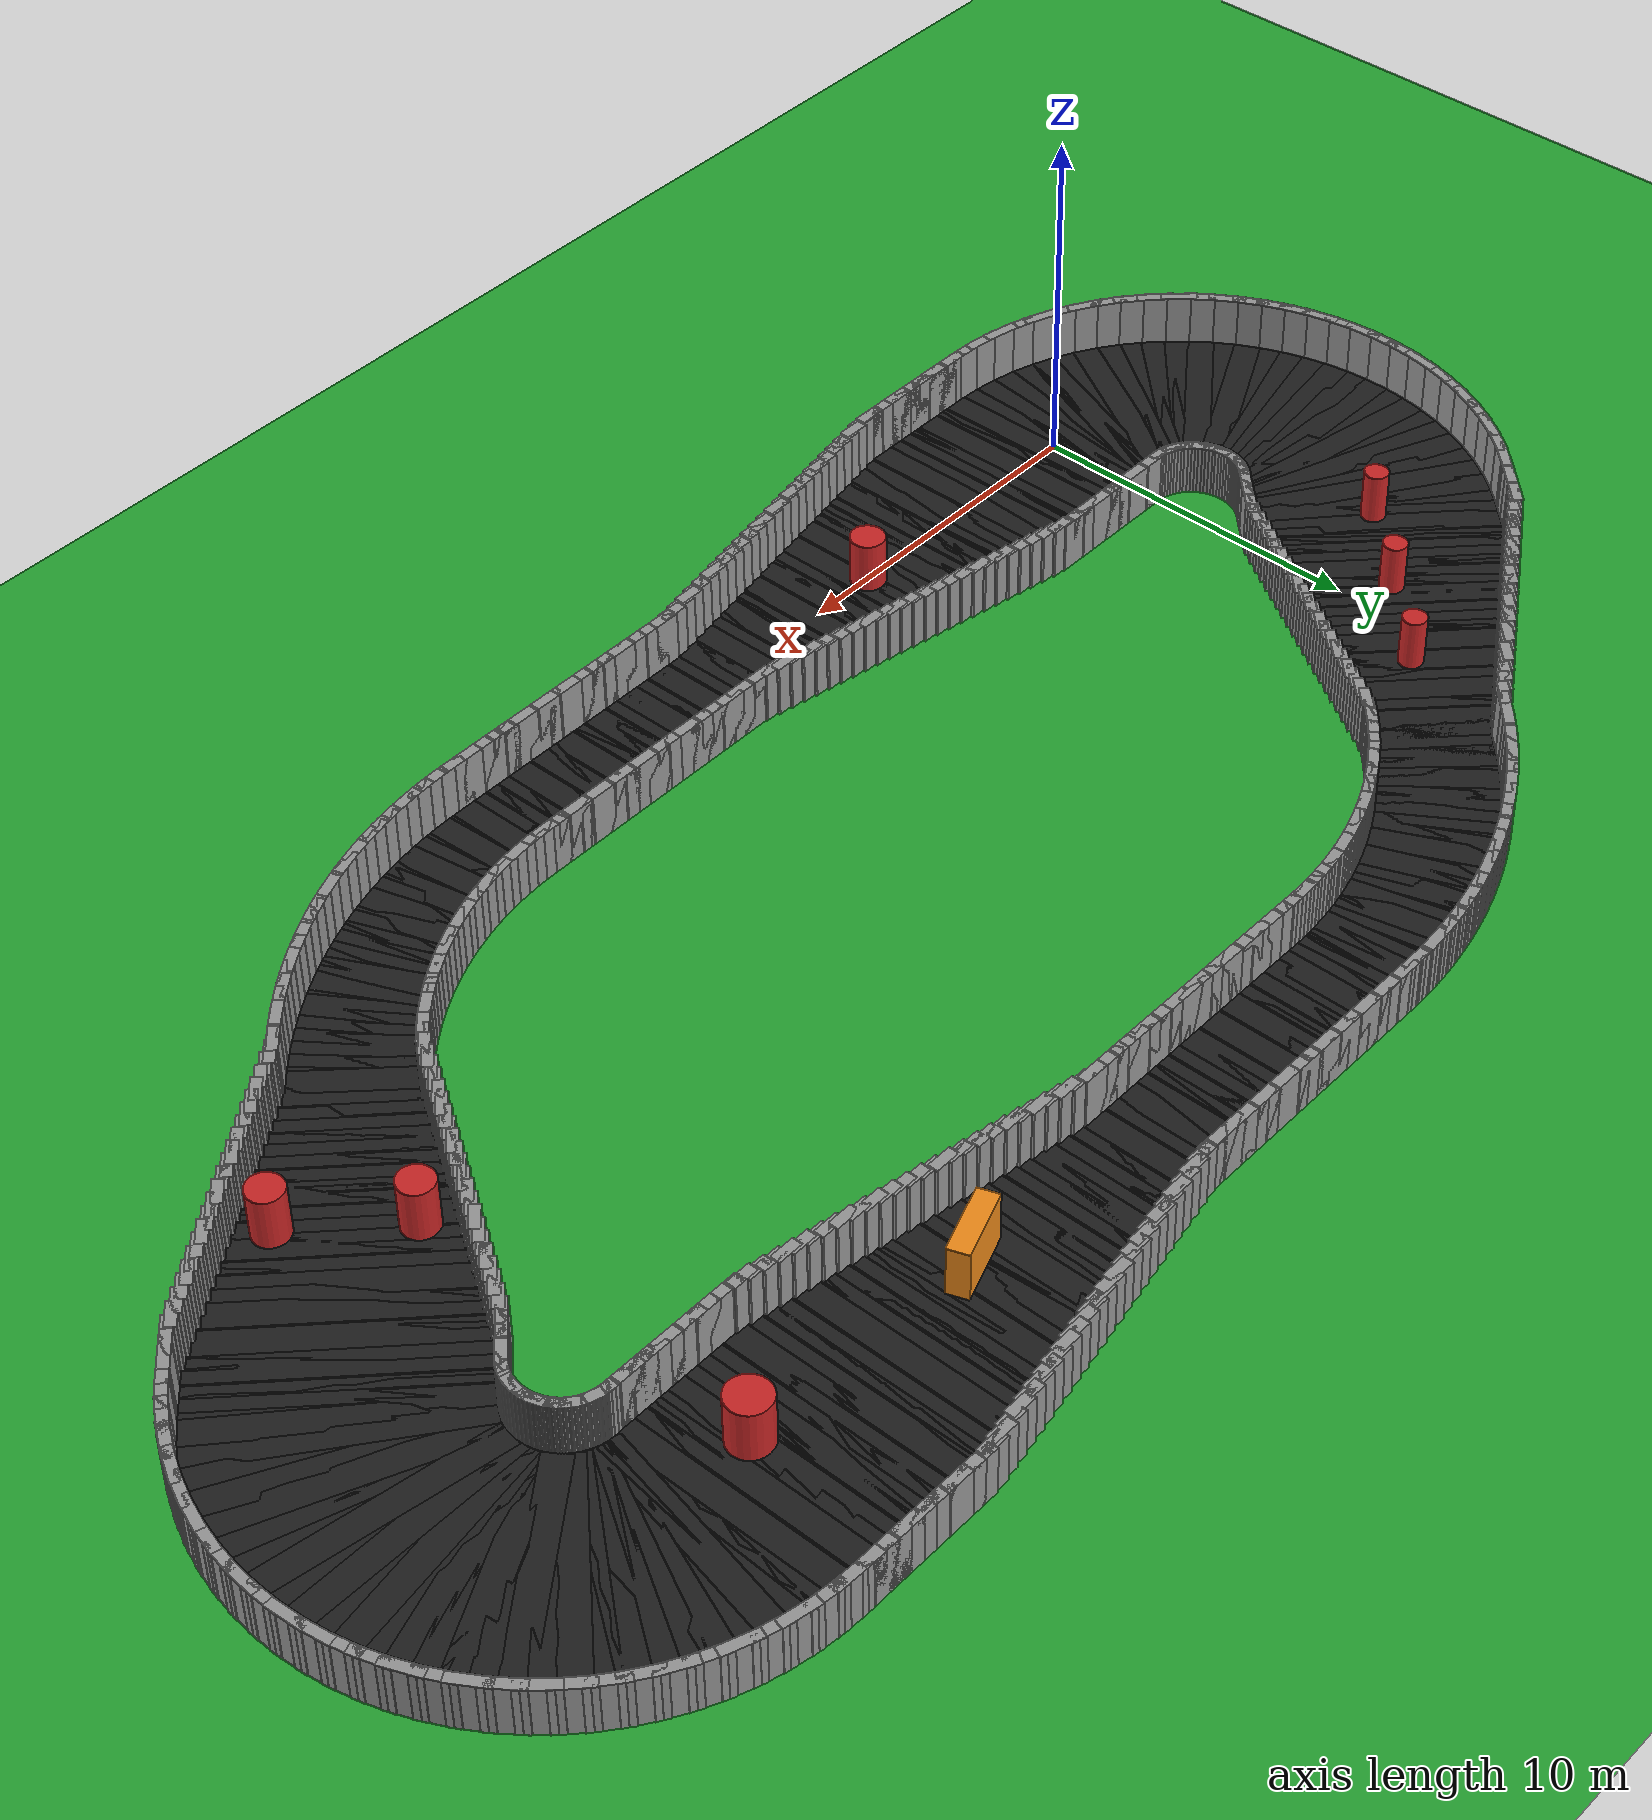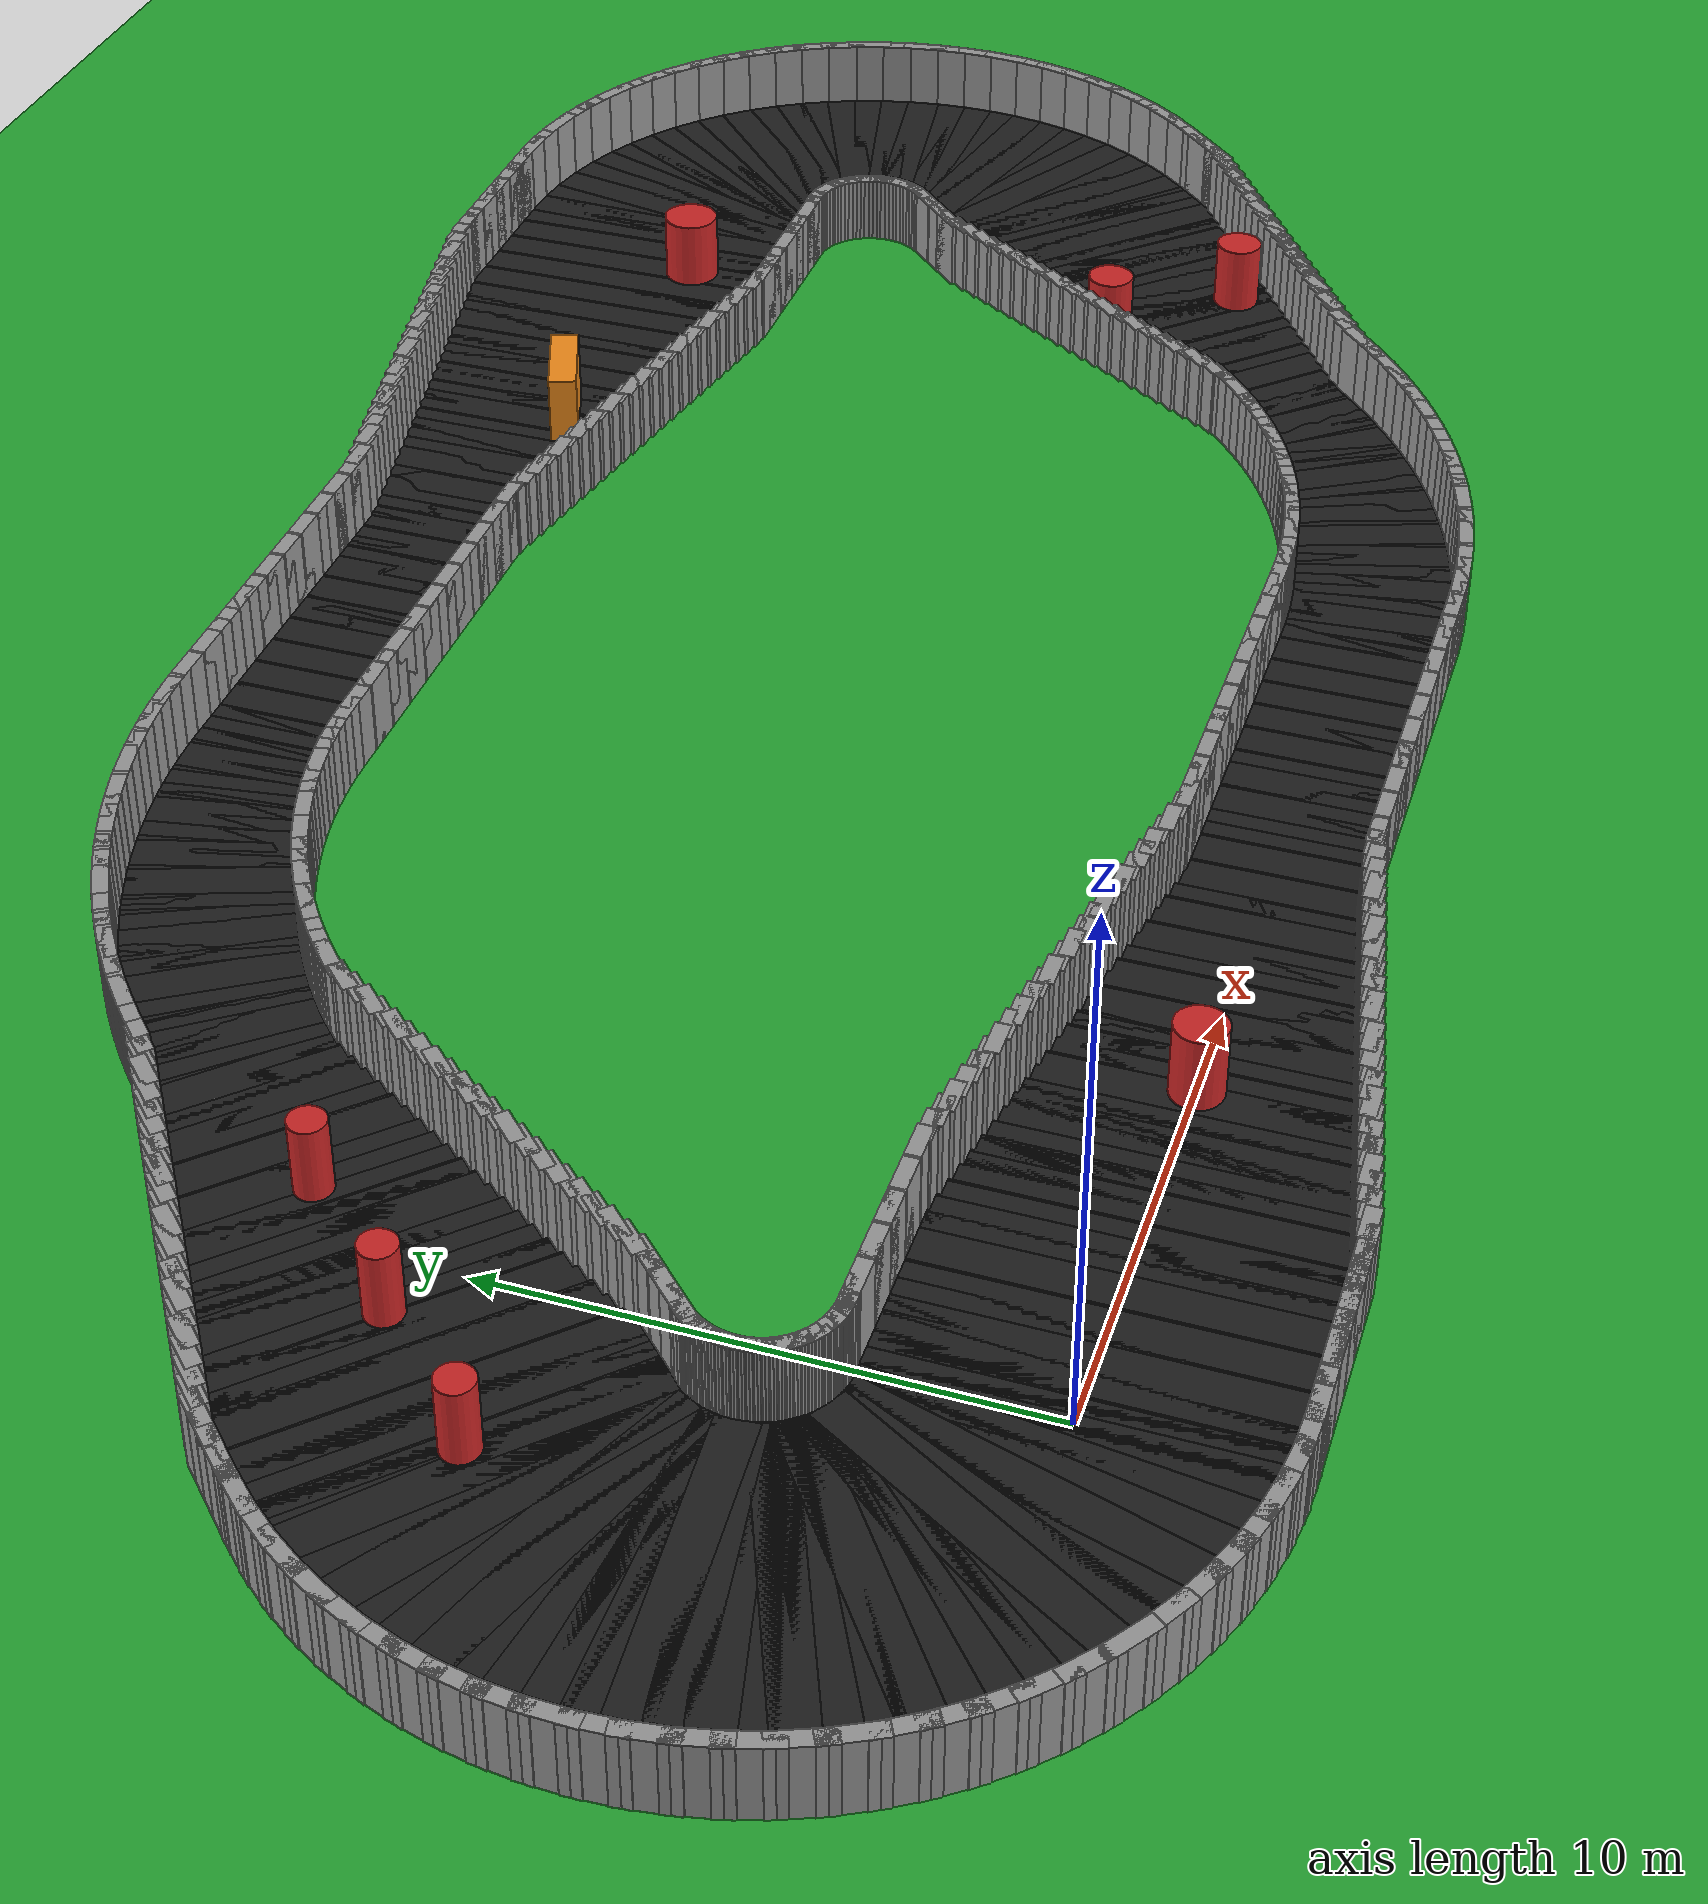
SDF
<?xml version="1.0" ?>
<sdf version="1.6">
  <world name="obstacle_taper">
    <physics type="ode">
      <max_step_size>0.001</max_step_size>
      <real_time_factor>1.0</real_time_factor>
      <real_time_update_rate>1000</real_time_update_rate>
    </physics>
    <include><uri>model://sun</uri></include>

    <model name="ground_plane">
      <static>true</static>
      <link name="link">
        <collision name="collision">
          <surface><friction><ode><mu>100</mu><mu2>50</mu2></ode></friction></surface>
          <geometry><plane><normal>0 0 1</normal>
            <size>120 120</size></plane></geometry>
        </collision>
        <visual name="visual">
          <geometry><plane><normal>0 0 1</normal>
            <size>120 120</size></plane></geometry>
          <material><script>
            <uri>file://media/materials/scripts/gazebo.material</uri>
            <name>Gazebo/Green</name></script></material>
        </visual>
      </link>
    </model>

    <model name="asphalt_0">
      <static>true</static>
      <pose>0.200 0.000 0.005 0 0 0.00000</pose>
      <link name="link">
        <visual name="visual">
          <geometry><box><size>0.760 7.000 0.010</size></box></geometry>
          <material><script><uri>file://media/materials/scripts/gazebo.material</uri><name>Gazebo/Black</name></script></material>
        </visual>
      </link>
    </model>
    <model name="curbL_0">
      <static>true</static>
      <pose>0.200 3.650 0.750 0 0 0.00000</pose>
      <link name="link">
        <collision name="collision">
          <geometry><box><size>0.760 0.300 1.500</size></box></geometry>
        </collision>
        <visual name="visual">
          <geometry><box><size>0.760 0.300 1.500</size></box></geometry>
          <material><script><uri>file://media/materials/scripts/gazebo.material</uri><name>Gazebo/Grey</name></script></material>
        </visual>
      </link>
    </model>
    <model name="curbR_0">
      <static>true</static>
      <pose>0.200 -3.650 0.750 0 0 0.00000</pose>
      <link name="link">
        <collision name="collision">
          <geometry><box><size>0.760 0.300 1.500</size></box></geometry>
        </collision>
        <visual name="visual">
          <geometry><box><size>0.760 0.300 1.500</size></box></geometry>
          <material><script><uri>file://media/materials/scripts/gazebo.material</uri><name>Gazebo/Grey</name></script></material>
        </visual>
      </link>
    </model>
    <model name="asphalt_1">
      <static>true</static>
      <pose>0.600 0.000 0.005 0 0 0.00000</pose>
      <link name="link">
        <visual name="visual">
          <geometry><box><size>0.760 7.000 0.010</size></box></geometry>
          <material><script><uri>file://media/materials/scripts/gazebo.material</uri><name>Gazebo/Black</name></script></material>
        </visual>
      </link>
    </model>
    <model name="curbL_1">
      <static>true</static>
      <pose>0.600 3.650 0.750 0 0 0.00000</pose>
      <link name="link">
        <collision name="collision">
          <geometry><box><size>0.760 0.300 1.500</size></box></geometry>
        </collision>
        <visual name="visual">
          <geometry><box><size>0.760 0.300 1.500</size></box></geometry>
          <material><script><uri>file://media/materials/scripts/gazebo.material</uri><name>Gazebo/Grey</name></script></material>
        </visual>
      </link>
    </model>
    <model name="curbR_1">
      <static>true</static>
      <pose>0.600 -3.650 0.750 0 0 0.00000</pose>
      <link name="link">
        <collision name="collision">
          <geometry><box><size>0.760 0.300 1.500</size></box></geometry>
        </collision>
        <visual name="visual">
          <geometry><box><size>0.760 0.300 1.500</size></box></geometry>
          <material><script><uri>file://media/materials/scripts/gazebo.material</uri><name>Gazebo/Grey</name></script></material>
        </visual>
      </link>
    </model>
    <model name="asphalt_2">
      <static>true</static>
      <pose>1.000 0.000 0.005 0 0 0.00000</pose>
      <link name="link">
        <visual name="visual">
          <geometry><box><size>0.760 7.000 0.010</size></box></geometry>
          <material><script><uri>file://media/materials/scripts/gazebo.material</uri><name>Gazebo/Black</name></script></material>
        </visual>
      </link>
    </model>
    <model name="curbL_2">
      <static>true</static>
      <pose>1.000 3.650 0.750 0 0 0.00000</pose>
      <link name="link">
        <collision name="collision">
          <geometry><box><size>0.760 0.300 1.500</size></box></geometry>
        </collision>
        <visual name="visual">
          <geometry><box><size>0.760 0.300 1.500</size></box></geometry>
          <material><script><uri>file://media/materials/scripts/gazebo.material</uri><name>Gazebo/Grey</name></script></material>
        </visual>
      </link>
    </model>
    <model name="curbR_2">
      <static>true</static>
      <pose>1.000 -3.650 0.750 0 0 0.00000</pose>
      <link name="link">
        <collision name="collision">
          <geometry><box><size>0.760 0.300 1.500</size></box></geometry>
        </collision>
        <visual name="visual">
          <geometry><box><size>0.760 0.300 1.500</size></box></geometry>
          <material><script><uri>file://media/materials/scripts/gazebo.material</uri><name>Gazebo/Grey</name></script></material>
        </visual>
      </link>
    </model>
    <model name="asphalt_3">
      <static>true</static>
      <pose>1.400 0.000 0.005 0 0 0.00000</pose>
      <link name="link">
        <visual name="visual">
          <geometry><box><size>0.760 7.000 0.010</size></box></geometry>
          <material><script><uri>file://media/materials/scripts/gazebo.material</uri><name>Gazebo/Black</name></script></material>
        </visual>
      </link>
    </model>
    <model name="curbL_3">
      <static>true</static>
      <pose>1.400 3.650 0.750 0 0 0.00000</pose>
      <link name="link">
        <collision name="collision">
          <geometry><box><size>0.760 0.300 1.500</size></box></geometry>
        </collision>
        <visual name="visual">
          <geometry><box><size>0.760 0.300 1.500</size></box></geometry>
          <material><script><uri>file://media/materials/scripts/gazebo.material</uri><name>Gazebo/Grey</name></script></material>
        </visual>
      </link>
    </model>
    <model name="curbR_3">
      <static>true</static>
      <pose>1.400 -3.650 0.750 0 0 0.00000</pose>
      <link name="link">
        <collision name="collision">
          <geometry><box><size>0.760 0.300 1.500</size></box></geometry>
        </collision>
        <visual name="visual">
          <geometry><box><size>0.760 0.300 1.500</size></box></geometry>
          <material><script><uri>file://media/materials/scripts/gazebo.material</uri><name>Gazebo/Grey</name></script></material>
        </visual>
      </link>
    </model>
    <model name="asphalt_4">
      <static>true</static>
      <pose>1.800 0.000 0.005 0 0 0.00000</pose>
      <link name="link">
        <visual name="visual">
          <geometry><box><size>0.760 7.000 0.010</size></box></geometry>
          <material><script><uri>file://media/materials/scripts/gazebo.material</uri><name>Gazebo/Black</name></script></material>
        </visual>
      </link>
    </model>
    <model name="curbL_4">
      <static>true</static>
      <pose>1.800 3.650 0.750 0 0 0.00000</pose>
      <link name="link">
        <collision name="collision">
          <geometry><box><size>0.760 0.300 1.500</size></box></geometry>
        </collision>
        <visual name="visual">
          <geometry><box><size>0.760 0.300 1.500</size></box></geometry>
          <material><script><uri>file://media/materials/scripts/gazebo.material</uri><name>Gazebo/Grey</name></script></material>
        </visual>
      </link>
    </model>
    <model name="curbR_4">
      <static>true</static>
      <pose>1.800 -3.650 0.750 0 0 0.00000</pose>
      <link name="link">
        <collision name="collision">
          <geometry><box><size>0.760 0.300 1.500</size></box></geometry>
        </collision>
        <visual name="visual">
          <geometry><box><size>0.760 0.300 1.500</size></box></geometry>
          <material><script><uri>file://media/materials/scripts/gazebo.material</uri><name>Gazebo/Grey</name></script></material>
        </visual>
      </link>
    </model>
    <model name="asphalt_5">
      <static>true</static>
      <pose>2.200 0.000 0.005 0 0 0.00000</pose>
      <link name="link">
        <visual name="visual">
          <geometry><box><size>0.760 7.000 0.010</size></box></geometry>
          <material><script><uri>file://media/materials/scripts/gazebo.material</uri><name>Gazebo/Black</name></script></material>
        </visual>
      </link>
    </model>
    <model name="curbL_5">
      <static>true</static>
      <pose>2.200 3.650 0.750 0 0 0.00000</pose>
      <link name="link">
        <collision name="collision">
          <geometry><box><size>0.760 0.300 1.500</size></box></geometry>
        </collision>
        <visual name="visual">
          <geometry><box><size>0.760 0.300 1.500</size></box></geometry>
          <material><script><uri>file://media/materials/scripts/gazebo.material</uri><name>Gazebo/Grey</name></script></material>
        </visual>
      </link>
    </model>
    <model name="curbR_5">
      <static>true</static>
      <pose>2.200 -3.650 0.750 0 0 0.00000</pose>
      <link name="link">
        <collision name="collision">
          <geometry><box><size>0.760 0.300 1.500</size></box></geometry>
        </collision>
        <visual name="visual">
          <geometry><box><size>0.760 0.300 1.500</size></box></geometry>
          <material><script><uri>file://media/materials/scripts/gazebo.material</uri><name>Gazebo/Grey</name></script></material>
        </visual>
      </link>
    </model>
    <model name="asphalt_6">
      <static>true</static>
      <pose>2.600 0.000 0.005 0 0 0.00000</pose>
      <link name="link">
        <visual name="visual">
          <geometry><box><size>0.760 7.000 0.010</size></box></geometry>
          <material><script><uri>file://media/materials/scripts/gazebo.material</uri><name>Gazebo/Black</name></script></material>
        </visual>
      </link>
    </model>
    <model name="curbL_6">
      <static>true</static>
      <pose>2.600 3.650 0.750 0 0 0.00000</pose>
      <link name="link">
        <collision name="collision">
          <geometry><box><size>0.760 0.300 1.500</size></box></geometry>
        </collision>
        <visual name="visual">
          <geometry><box><size>0.760 0.300 1.500</size></box></geometry>
          <material><script><uri>file://media/materials/scripts/gazebo.material</uri><name>Gazebo/Grey</name></script></material>
        </visual>
      </link>
    </model>
    <model name="curbR_6">
      <static>true</static>
      <pose>2.600 -3.650 0.750 0 0 0.00000</pose>
      <link name="link">
        <collision name="collision">
          <geometry><box><size>0.760 0.300 1.500</size></box></geometry>
        </collision>
        <visual name="visual">
          <geometry><box><size>0.760 0.300 1.500</size></box></geometry>
          <material><script><uri>file://media/materials/scripts/gazebo.material</uri><name>Gazebo/Grey</name></script></material>
        </visual>
      </link>
    </model>
    <model name="asphalt_7">
      <static>true</static>
      <pose>3.000 0.000 0.005 0 0 0.00000</pose>
      <link name="link">
        <visual name="visual">
          <geometry><box><size>0.760 7.000 0.010</size></box></geometry>
          <material><script><uri>file://media/materials/scripts/gazebo.material</uri><name>Gazebo/Black</name></script></material>
        </visual>
      </link>
    </model>
    <model name="curbL_7">
      <static>true</static>
      <pose>3.000 3.650 0.750 0 0 0.00000</pose>
      <link name="link">
        <collision name="collision">
          <geometry><box><size>0.760 0.300 1.500</size></box></geometry>
        </collision>
        <visual name="visual">
          <geometry><box><size>0.760 0.300 1.500</size></box></geometry>
          <material><script><uri>file://media/materials/scripts/gazebo.material</uri><name>Gazebo/Grey</name></script></material>
        </visual>
      </link>
    </model>
    <model name="curbR_7">
      <static>true</static>
      <pose>3.000 -3.650 0.750 0 0 0.00000</pose>
      <link name="link">
        <collision name="collision">
          <geometry><box><size>0.760 0.300 1.500</size></box></geometry>
        </collision>
        <visual name="visual">
          <geometry><box><size>0.760 0.300 1.500</size></box></geometry>
          <material><script><uri>file://media/materials/scripts/gazebo.material</uri><name>Gazebo/Grey</name></script></material>
        </visual>
      </link>
    </model>
    <model name="asphalt_8">
      <static>true</static>
      <pose>3.400 0.000 0.005 0 0 0.00000</pose>
      <link name="link">
        <visual name="visual">
          <geometry><box><size>0.760 7.000 0.010</size></box></geometry>
          <material><script><uri>file://media/materials/scripts/gazebo.material</uri><name>Gazebo/Black</name></script></material>
        </visual>
      </link>
    </model>
    <model name="curbL_8">
      <static>true</static>
      <pose>3.400 3.650 0.750 0 0 0.00000</pose>
      <link name="link">
        <collision name="collision">
          <geometry><box><size>0.760 0.300 1.500</size></box></geometry>
        </collision>
        <visual name="visual">
          <geometry><box><size>0.760 0.300 1.500</size></box></geometry>
          <material><script><uri>file://media/materials/scripts/gazebo.material</uri><name>Gazebo/Grey</name></script></material>
        </visual>
      </link>
    </model>
    <model name="curbR_8">
      <static>true</static>
      <pose>3.400 -3.650 0.750 0 0 0.00000</pose>
      <link name="link">
        <collision name="collision">
          <geometry><box><size>0.760 0.300 1.500</size></box></geometry>
        </collision>
        <visual name="visual">
          <geometry><box><size>0.760 0.300 1.500</size></box></geometry>
          <material><script><uri>file://media/materials/scripts/gazebo.material</uri><name>Gazebo/Grey</name></script></material>
        </visual>
      </link>
    </model>
    <model name="asphalt_9">
      <static>true</static>
      <pose>3.800 0.000 0.005 0 0 0.00000</pose>
      <link name="link">
        <visual name="visual">
          <geometry><box><size>0.760 7.000 0.010</size></box></geometry>
          <material><script><uri>file://media/materials/scripts/gazebo.material</uri><name>Gazebo/Black</name></script></material>
        </visual>
      </link>
    </model>
    <model name="curbL_9">
      <static>true</static>
      <pose>3.800 3.650 0.750 0 0 0.00000</pose>
      <link name="link">
        <collision name="collision">
          <geometry><box><size>0.760 0.300 1.500</size></box></geometry>
        </collision>
        <visual name="visual">
          <geometry><box><size>0.760 0.300 1.500</size></box></geometry>
          <material><script><uri>file://media/materials/scripts/gazebo.material</uri><name>Gazebo/Grey</name></script></material>
        </visual>
      </link>
    </model>
    <model name="curbR_9">
      <static>true</static>
      <pose>3.800 -3.650 0.750 0 0 0.00000</pose>
      <link name="link">
        <collision name="collision">
          <geometry><box><size>0.760 0.300 1.500</size></box></geometry>
        </collision>
        <visual name="visual">
          <geometry><box><size>0.760 0.300 1.500</size></box></geometry>
          <material><script><uri>file://media/materials/scripts/gazebo.material</uri><name>Gazebo/Grey</name></script></material>
        </visual>
      </link>
    </model>
    <model name="asphalt_10">
      <static>true</static>
      <pose>4.200 0.000 0.005 0 0 0.00000</pose>
      <link name="link">
        <visual name="visual">
          <geometry><box><size>0.760 6.924 0.010</size></box></geometry>
          <material><script><uri>file://media/materials/scripts/gazebo.material</uri><name>Gazebo/Black</name></script></material>
        </visual>
      </link>
    </model>
    <model name="curbL_10">
      <static>true</static>
      <pose>4.200 3.612 0.750 0 0 0.00000</pose>
      <link name="link">
        <collision name="collision">
          <geometry><box><size>0.760 0.300 1.500</size></box></geometry>
        </collision>
        <visual name="visual">
          <geometry><box><size>0.760 0.300 1.500</size></box></geometry>
          <material><script><uri>file://media/materials/scripts/gazebo.material</uri><name>Gazebo/Grey</name></script></material>
        </visual>
      </link>
    </model>
    <model name="curbR_10">
      <static>true</static>
      <pose>4.200 -3.612 0.750 0 0 0.00000</pose>
      <link name="link">
        <collision name="collision">
          <geometry><box><size>0.760 0.300 1.500</size></box></geometry>
        </collision>
        <visual name="visual">
          <geometry><box><size>0.760 0.300 1.500</size></box></geometry>
          <material><script><uri>file://media/materials/scripts/gazebo.material</uri><name>Gazebo/Grey</name></script></material>
        </visual>
      </link>
    </model>
    <model name="asphalt_11">
      <static>true</static>
      <pose>4.600 0.000 0.005 0 0 0.00000</pose>
      <link name="link">
        <visual name="visual">
          <geometry><box><size>0.760 6.772 0.010</size></box></geometry>
          <material><script><uri>file://media/materials/scripts/gazebo.material</uri><name>Gazebo/Black</name></script></material>
        </visual>
      </link>
    </model>
    <model name="curbL_11">
      <static>true</static>
      <pose>4.600 3.536 0.750 0 0 0.00000</pose>
      <link name="link">
        <collision name="collision">
          <geometry><box><size>0.760 0.300 1.500</size></box></geometry>
        </collision>
        <visual name="visual">
          <geometry><box><size>0.760 0.300 1.500</size></box></geometry>
          <material><script><uri>file://media/materials/scripts/gazebo.material</uri><name>Gazebo/Grey</name></script></material>
        </visual>
      </link>
    </model>
    <model name="curbR_11">
      <static>true</static>
      <pose>4.600 -3.536 0.750 0 0 0.00000</pose>
      <link name="link">
        <collision name="collision">
          <geometry><box><size>0.760 0.300 1.500</size></box></geometry>
        </collision>
        <visual name="visual">
          <geometry><box><size>0.760 0.300 1.500</size></box></geometry>
          <material><script><uri>file://media/materials/scripts/gazebo.material</uri><name>Gazebo/Grey</name></script></material>
        </visual>
      </link>
    </model>
    <model name="asphalt_12">
      <static>true</static>
      <pose>5.000 0.000 0.005 0 0 0.00000</pose>
      <link name="link">
        <visual name="visual">
          <geometry><box><size>0.760 6.620 0.010</size></box></geometry>
          <material><script><uri>file://media/materials/scripts/gazebo.material</uri><name>Gazebo/Black</name></script></material>
        </visual>
      </link>
    </model>
    <model name="curbL_12">
      <static>true</static>
      <pose>5.000 3.460 0.750 0 0 0.00000</pose>
      <link name="link">
        <collision name="collision">
          <geometry><box><size>0.760 0.300 1.500</size></box></geometry>
        </collision>
        <visual name="visual">
          <geometry><box><size>0.760 0.300 1.500</size></box></geometry>
          <material><script><uri>file://media/materials/scripts/gazebo.material</uri><name>Gazebo/Grey</name></script></material>
        </visual>
      </link>
    </model>
    <model name="curbR_12">
      <static>true</static>
      <pose>5.000 -3.460 0.750 0 0 0.00000</pose>
      <link name="link">
        <collision name="collision">
          <geometry><box><size>0.760 0.300 1.500</size></box></geometry>
        </collision>
        <visual name="visual">
          <geometry><box><size>0.760 0.300 1.500</size></box></geometry>
          <material><script><uri>file://media/materials/scripts/gazebo.material</uri><name>Gazebo/Grey</name></script></material>
        </visual>
      </link>
    </model>
    <model name="asphalt_13">
      <static>true</static>
      <pose>5.400 0.000 0.005 0 0 0.00000</pose>
      <link name="link">
        <visual name="visual">
          <geometry><box><size>0.760 6.468 0.010</size></box></geometry>
          <material><script><uri>file://media/materials/scripts/gazebo.material</uri><name>Gazebo/Black</name></script></material>
        </visual>
      </link>
    </model>
    <model name="curbL_13">
      <static>true</static>
      <pose>5.400 3.384 0.750 0 0 0.00000</pose>
      <link name="link">
        <collision name="collision">
          <geometry><box><size>0.760 0.300 1.500</size></box></geometry>
        </collision>
        <visual name="visual">
          <geometry><box><size>0.760 0.300 1.500</size></box></geometry>
          <material><script><uri>file://media/materials/scripts/gazebo.material</uri><name>Gazebo/Grey</name></script></material>
        </visual>
      </link>
    </model>
    <model name="curbR_13">
      <static>true</static>
      <pose>5.400 -3.384 0.750 0 0 0.00000</pose>
      <link name="link">
        <collision name="collision">
          <geometry><box><size>0.760 0.300 1.500</size></box></geometry>
        </collision>
        <visual name="visual">
          <geometry><box><size>0.760 0.300 1.500</size></box></geometry>
          <material><script><uri>file://media/materials/scripts/gazebo.material</uri><name>Gazebo/Grey</name></script></material>
        </visual>
      </link>
    </model>
    <model name="asphalt_14">
      <static>true</static>
      <pose>5.800 0.000 0.005 0 0 0.00000</pose>
      <link name="link">
        <visual name="visual">
          <geometry><box><size>0.760 6.316 0.010</size></box></geometry>
          <material><script><uri>file://media/materials/scripts/gazebo.material</uri><name>Gazebo/Black</name></script></material>
        </visual>
      </link>
    </model>
    <model name="curbL_14">
      <static>true</static>
      <pose>5.800 3.308 0.750 0 0 0.00000</pose>
      <link name="link">
        <collision name="collision">
          <geometry><box><size>0.760 0.300 1.500</size></box></geometry>
        </collision>
        <visual name="visual">
          <geometry><box><size>0.760 0.300 1.500</size></box></geometry>
          <material><script><uri>file://media/materials/scripts/gazebo.material</uri><name>Gazebo/Grey</name></script></material>
        </visual>
      </link>
    </model>
    <model name="curbR_14">
      <static>true</static>
      <pose>5.800 -3.308 0.750 0 0 0.00000</pose>
      <link name="link">
        <collision name="collision">
          <geometry><box><size>0.760 0.300 1.500</size></box></geometry>
        </collision>
        <visual name="visual">
          <geometry><box><size>0.760 0.300 1.500</size></box></geometry>
          <material><script><uri>file://media/materials/scripts/gazebo.material</uri><name>Gazebo/Grey</name></script></material>
        </visual>
      </link>
    </model>
    <model name="asphalt_15">
      <static>true</static>
      <pose>6.200 0.000 0.005 0 0 0.00000</pose>
      <link name="link">
        <visual name="visual">
          <geometry><box><size>0.760 6.164 0.010</size></box></geometry>
          <material><script><uri>file://media/materials/scripts/gazebo.material</uri><name>Gazebo/Black</name></script></material>
        </visual>
      </link>
    </model>
    <model name="curbL_15">
      <static>true</static>
      <pose>6.200 3.232 0.750 0 0 0.00000</pose>
      <link name="link">
        <collision name="collision">
          <geometry><box><size>0.760 0.300 1.500</size></box></geometry>
        </collision>
        <visual name="visual">
          <geometry><box><size>0.760 0.300 1.500</size></box></geometry>
          <material><script><uri>file://media/materials/scripts/gazebo.material</uri><name>Gazebo/Grey</name></script></material>
        </visual>
      </link>
    </model>
    <model name="curbR_15">
      <static>true</static>
      <pose>6.200 -3.232 0.750 0 0 0.00000</pose>
      <link name="link">
        <collision name="collision">
          <geometry><box><size>0.760 0.300 1.500</size></box></geometry>
        </collision>
        <visual name="visual">
          <geometry><box><size>0.760 0.300 1.500</size></box></geometry>
          <material><script><uri>file://media/materials/scripts/gazebo.material</uri><name>Gazebo/Grey</name></script></material>
        </visual>
      </link>
    </model>
    <model name="asphalt_16">
      <static>true</static>
      <pose>6.600 0.000 0.005 0 0 0.00000</pose>
      <link name="link">
        <visual name="visual">
          <geometry><box><size>0.760 6.012 0.010</size></box></geometry>
          <material><script><uri>file://media/materials/scripts/gazebo.material</uri><name>Gazebo/Black</name></script></material>
        </visual>
      </link>
    </model>
    <model name="curbL_16">
      <static>true</static>
      <pose>6.600 3.156 0.750 0 0 0.00000</pose>
      <link name="link">
        <collision name="collision">
          <geometry><box><size>0.760 0.300 1.500</size></box></geometry>
        </collision>
        <visual name="visual">
          <geometry><box><size>0.760 0.300 1.500</size></box></geometry>
          <material><script><uri>file://media/materials/scripts/gazebo.material</uri><name>Gazebo/Grey</name></script></material>
        </visual>
      </link>
    </model>
    <model name="curbR_16">
      <static>true</static>
      <pose>6.600 -3.156 0.750 0 0 0.00000</pose>
      <link name="link">
        <collision name="collision">
          <geometry><box><size>0.760 0.300 1.500</size></box></geometry>
        </collision>
        <visual name="visual">
          <geometry><box><size>0.760 0.300 1.500</size></box></geometry>
          <material><script><uri>file://media/materials/scripts/gazebo.material</uri><name>Gazebo/Grey</name></script></material>
        </visual>
      </link>
    </model>
    <model name="asphalt_17">
      <static>true</static>
      <pose>7.000 0.000 0.005 0 0 0.00000</pose>
      <link name="link">
        <visual name="visual">
          <geometry><box><size>0.760 5.860 0.010</size></box></geometry>
          <material><script><uri>file://media/materials/scripts/gazebo.material</uri><name>Gazebo/Black</name></script></material>
        </visual>
      </link>
    </model>
    <model name="curbL_17">
      <static>true</static>
      <pose>7.000 3.080 0.750 0 0 0.00000</pose>
      <link name="link">
        <collision name="collision">
          <geometry><box><size>0.760 0.300 1.500</size></box></geometry>
        </collision>
        <visual name="visual">
          <geometry><box><size>0.760 0.300 1.500</size></box></geometry>
          <material><script><uri>file://media/materials/scripts/gazebo.material</uri><name>Gazebo/Grey</name></script></material>
        </visual>
      </link>
    </model>
    <model name="curbR_17">
      <static>true</static>
      <pose>7.000 -3.080 0.750 0 0 0.00000</pose>
      <link name="link">
        <collision name="collision">
          <geometry><box><size>0.760 0.300 1.500</size></box></geometry>
        </collision>
        <visual name="visual">
          <geometry><box><size>0.760 0.300 1.500</size></box></geometry>
          <material><script><uri>file://media/materials/scripts/gazebo.material</uri><name>Gazebo/Grey</name></script></material>
        </visual>
      </link>
    </model>
    <model name="asphalt_18">
      <static>true</static>
      <pose>7.400 0.000 0.005 0 0 0.00000</pose>
      <link name="link">
        <visual name="visual">
          <geometry><box><size>0.760 5.708 0.010</size></box></geometry>
          <material><script><uri>file://media/materials/scripts/gazebo.material</uri><name>Gazebo/Black</name></script></material>
        </visual>
      </link>
    </model>
    <model name="curbL_18">
      <static>true</static>
      <pose>7.400 3.004 0.750 0 0 0.00000</pose>
      <link name="link">
        <collision name="collision">
          <geometry><box><size>0.760 0.300 1.500</size></box></geometry>
        </collision>
        <visual name="visual">
          <geometry><box><size>0.760 0.300 1.500</size></box></geometry>
          <material><script><uri>file://media/materials/scripts/gazebo.material</uri><name>Gazebo/Grey</name></script></material>
        </visual>
      </link>
    </model>
    <model name="curbR_18">
      <static>true</static>
      <pose>7.400 -3.004 0.750 0 0 0.00000</pose>
      <link name="link">
        <collision name="collision">
          <geometry><box><size>0.760 0.300 1.500</size></box></geometry>
        </collision>
        <visual name="visual">
          <geometry><box><size>0.760 0.300 1.500</size></box></geometry>
          <material><script><uri>file://media/materials/scripts/gazebo.material</uri><name>Gazebo/Grey</name></script></material>
        </visual>
      </link>
    </model>
    <model name="asphalt_19">
      <static>true</static>
      <pose>7.800 0.000 0.005 0 0 0.00000</pose>
      <link name="link">
        <visual name="visual">
          <geometry><box><size>0.760 5.556 0.010</size></box></geometry>
          <material><script><uri>file://media/materials/scripts/gazebo.material</uri><name>Gazebo/Black</name></script></material>
        </visual>
      </link>
    </model>
    <model name="curbL_19">
      <static>true</static>
      <pose>7.800 2.928 0.750 0 0 0.00000</pose>
      <link name="link">
        <collision name="collision">
          <geometry><box><size>0.760 0.300 1.500</size></box></geometry>
        </collision>
        <visual name="visual">
          <geometry><box><size>0.760 0.300 1.500</size></box></geometry>
          <material><script><uri>file://media/materials/scripts/gazebo.material</uri><name>Gazebo/Grey</name></script></material>
        </visual>
      </link>
    </model>
    <model name="curbR_19">
      <static>true</static>
      <pose>7.800 -2.928 0.750 0 0 0.00000</pose>
      <link name="link">
        <collision name="collision">
          <geometry><box><size>0.760 0.300 1.500</size></box></geometry>
        </collision>
        <visual name="visual">
          <geometry><box><size>0.760 0.300 1.500</size></box></geometry>
          <material><script><uri>file://media/materials/scripts/gazebo.material</uri><name>Gazebo/Grey</name></script></material>
        </visual>
      </link>
    </model>
    <model name="asphalt_20">
      <static>true</static>
      <pose>8.200 0.000 0.005 0 0 0.00000</pose>
      <link name="link">
        <visual name="visual">
          <geometry><box><size>0.760 5.404 0.010</size></box></geometry>
          <material><script><uri>file://media/materials/scripts/gazebo.material</uri><name>Gazebo/Black</name></script></material>
        </visual>
      </link>
    </model>
    <model name="curbL_20">
      <static>true</static>
      <pose>8.200 2.852 0.750 0 0 0.00000</pose>
      <link name="link">
        <collision name="collision">
          <geometry><box><size>0.760 0.300 1.500</size></box></geometry>
        </collision>
        <visual name="visual">
          <geometry><box><size>0.760 0.300 1.500</size></box></geometry>
          <material><script><uri>file://media/materials/scripts/gazebo.material</uri><name>Gazebo/Grey</name></script></material>
        </visual>
      </link>
    </model>
    <model name="curbR_20">
      <static>true</static>
      <pose>8.200 -2.852 0.750 0 0 0.00000</pose>
      <link name="link">
        <collision name="collision">
          <geometry><box><size>0.760 0.300 1.500</size></box></geometry>
        </collision>
        <visual name="visual">
          <geometry><box><size>0.760 0.300 1.500</size></box></geometry>
          <material><script><uri>file://media/materials/scripts/gazebo.material</uri><name>Gazebo/Grey</name></script></material>
        </visual>
      </link>
    </model>
    <model name="asphalt_21">
      <static>true</static>
      <pose>8.600 0.000 0.005 0 0 0.00000</pose>
      <link name="link">
        <visual name="visual">
          <geometry><box><size>0.760 5.252 0.010</size></box></geometry>
          <material><script><uri>file://media/materials/scripts/gazebo.material</uri><name>Gazebo/Black</name></script></material>
        </visual>
      </link>
    </model>
    <model name="curbL_21">
      <static>true</static>
      <pose>8.600 2.776 0.750 0 0 0.00000</pose>
      <link name="link">
        <collision name="collision">
          <geometry><box><size>0.760 0.300 1.500</size></box></geometry>
        </collision>
        <visual name="visual">
          <geometry><box><size>0.760 0.300 1.500</size></box></geometry>
          <material><script><uri>file://media/materials/scripts/gazebo.material</uri><name>Gazebo/Grey</name></script></material>
        </visual>
      </link>
    </model>
    <model name="curbR_21">
      <static>true</static>
      <pose>8.600 -2.776 0.750 0 0 0.00000</pose>
      <link name="link">
        <collision name="collision">
          <geometry><box><size>0.760 0.300 1.500</size></box></geometry>
        </collision>
        <visual name="visual">
          <geometry><box><size>0.760 0.300 1.500</size></box></geometry>
          <material><script><uri>file://media/materials/scripts/gazebo.material</uri><name>Gazebo/Grey</name></script></material>
        </visual>
      </link>
    </model>
    <model name="asphalt_22">
      <static>true</static>
      <pose>9.000 0.000 0.005 0 0 0.00000</pose>
      <link name="link">
        <visual name="visual">
          <geometry><box><size>0.760 5.100 0.010</size></box></geometry>
          <material><script><uri>file://media/materials/scripts/gazebo.material</uri><name>Gazebo/Black</name></script></material>
        </visual>
      </link>
    </model>
    <model name="curbL_22">
      <static>true</static>
      <pose>9.000 2.700 0.750 0 0 0.00000</pose>
      <link name="link">
        <collision name="collision">
          <geometry><box><size>0.760 0.300 1.500</size></box></geometry>
        </collision>
        <visual name="visual">
          <geometry><box><size>0.760 0.300 1.500</size></box></geometry>
          <material><script><uri>file://media/materials/scripts/gazebo.material</uri><name>Gazebo/Grey</name></script></material>
        </visual>
      </link>
    </model>
    <model name="curbR_22">
      <static>true</static>
      <pose>9.000 -2.700 0.750 0 0 0.00000</pose>
      <link name="link">
        <collision name="collision">
          <geometry><box><size>0.760 0.300 1.500</size></box></geometry>
        </collision>
        <visual name="visual">
          <geometry><box><size>0.760 0.300 1.500</size></box></geometry>
          <material><script><uri>file://media/materials/scripts/gazebo.material</uri><name>Gazebo/Grey</name></script></material>
        </visual>
      </link>
    </model>
    <model name="asphalt_23">
      <static>true</static>
      <pose>9.400 0.000 0.005 0 0 0.00000</pose>
      <link name="link">
        <visual name="visual">
          <geometry><box><size>0.760 4.948 0.010</size></box></geometry>
          <material><script><uri>file://media/materials/scripts/gazebo.material</uri><name>Gazebo/Black</name></script></material>
        </visual>
      </link>
    </model>
    <model name="curbL_23">
      <static>true</static>
      <pose>9.400 2.624 0.750 0 0 0.00000</pose>
      <link name="link">
        <collision name="collision">
          <geometry><box><size>0.760 0.300 1.500</size></box></geometry>
        </collision>
        <visual name="visual">
          <geometry><box><size>0.760 0.300 1.500</size></box></geometry>
          <material><script><uri>file://media/materials/scripts/gazebo.material</uri><name>Gazebo/Grey</name></script></material>
        </visual>
      </link>
    </model>
    <model name="curbR_23">
      <static>true</static>
      <pose>9.400 -2.624 0.750 0 0 0.00000</pose>
      <link name="link">
        <collision name="collision">
          <geometry><box><size>0.760 0.300 1.500</size></box></geometry>
        </collision>
        <visual name="visual">
          <geometry><box><size>0.760 0.300 1.500</size></box></geometry>
          <material><script><uri>file://media/materials/scripts/gazebo.material</uri><name>Gazebo/Grey</name></script></material>
        </visual>
      </link>
    </model>
    <model name="asphalt_24">
      <static>true</static>
      <pose>9.800 0.000 0.005 0 0 0.00000</pose>
      <link name="link">
        <visual name="visual">
          <geometry><box><size>0.760 4.796 0.010</size></box></geometry>
          <material><script><uri>file://media/materials/scripts/gazebo.material</uri><name>Gazebo/Black</name></script></material>
        </visual>
      </link>
    </model>
    <model name="curbL_24">
      <static>true</static>
      <pose>9.800 2.548 0.750 0 0 0.00000</pose>
      <link name="link">
        <collision name="collision">
          <geometry><box><size>0.760 0.300 1.500</size></box></geometry>
        </collision>
        <visual name="visual">
          <geometry><box><size>0.760 0.300 1.500</size></box></geometry>
          <material><script><uri>file://media/materials/scripts/gazebo.material</uri><name>Gazebo/Grey</name></script></material>
        </visual>
      </link>
    </model>
    <model name="curbR_24">
      <static>true</static>
      <pose>9.800 -2.548 0.750 0 0 0.00000</pose>
      <link name="link">
        <collision name="collision">
          <geometry><box><size>0.760 0.300 1.500</size></box></geometry>
        </collision>
        <visual name="visual">
          <geometry><box><size>0.760 0.300 1.500</size></box></geometry>
          <material><script><uri>file://media/materials/scripts/gazebo.material</uri><name>Gazebo/Grey</name></script></material>
        </visual>
      </link>
    </model>
    <model name="asphalt_25">
      <static>true</static>
      <pose>10.200 0.000 0.005 0 0 0.00000</pose>
      <link name="link">
        <visual name="visual">
          <geometry><box><size>0.760 4.644 0.010</size></box></geometry>
          <material><script><uri>file://media/materials/scripts/gazebo.material</uri><name>Gazebo/Black</name></script></material>
        </visual>
      </link>
    </model>
    <model name="curbL_25">
      <static>true</static>
      <pose>10.200 2.472 0.750 0 0 0.00000</pose>
      <link name="link">
        <collision name="collision">
          <geometry><box><size>0.760 0.300 1.500</size></box></geometry>
        </collision>
        <visual name="visual">
          <geometry><box><size>0.760 0.300 1.500</size></box></geometry>
          <material><script><uri>file://media/materials/scripts/gazebo.material</uri><name>Gazebo/Grey</name></script></material>
        </visual>
      </link>
    </model>
    <model name="curbR_25">
      <static>true</static>
      <pose>10.200 -2.472 0.750 0 0 0.00000</pose>
      <link name="link">
        <collision name="collision">
          <geometry><box><size>0.760 0.300 1.500</size></box></geometry>
        </collision>
        <visual name="visual">
          <geometry><box><size>0.760 0.300 1.500</size></box></geometry>
          <material><script><uri>file://media/materials/scripts/gazebo.material</uri><name>Gazebo/Grey</name></script></material>
        </visual>
      </link>
    </model>
    <model name="asphalt_26">
      <static>true</static>
      <pose>10.600 0.000 0.005 0 0 0.00000</pose>
      <link name="link">
        <visual name="visual">
          <geometry><box><size>0.760 4.492 0.010</size></box></geometry>
          <material><script><uri>file://media/materials/scripts/gazebo.material</uri><name>Gazebo/Black</name></script></material>
        </visual>
      </link>
    </model>
    <model name="curbL_26">
      <static>true</static>
      <pose>10.600 2.396 0.750 0 0 0.00000</pose>
      <link name="link">
        <collision name="collision">
          <geometry><box><size>0.760 0.300 1.500</size></box></geometry>
        </collision>
        <visual name="visual">
          <geometry><box><size>0.760 0.300 1.500</size></box></geometry>
          <material><script><uri>file://media/materials/scripts/gazebo.material</uri><name>Gazebo/Grey</name></script></material>
        </visual>
      </link>
    </model>
    <model name="curbR_26">
      <static>true</static>
      <pose>10.600 -2.396 0.750 0 0 0.00000</pose>
      <link name="link">
        <collision name="collision">
          <geometry><box><size>0.760 0.300 1.500</size></box></geometry>
        </collision>
        <visual name="visual">
          <geometry><box><size>0.760 0.300 1.500</size></box></geometry>
          <material><script><uri>file://media/materials/scripts/gazebo.material</uri><name>Gazebo/Grey</name></script></material>
        </visual>
      </link>
    </model>
    <model name="asphalt_27">
      <static>true</static>
      <pose>11.000 0.000 0.005 0 0 0.00000</pose>
      <link name="link">
        <visual name="visual">
          <geometry><box><size>0.760 4.340 0.010</size></box></geometry>
          <material><script><uri>file://media/materials/scripts/gazebo.material</uri><name>Gazebo/Black</name></script></material>
        </visual>
      </link>
    </model>
    <model name="curbL_27">
      <static>true</static>
      <pose>11.000 2.320 0.750 0 0 0.00000</pose>
      <link name="link">
        <collision name="collision">
          <geometry><box><size>0.760 0.300 1.500</size></box></geometry>
        </collision>
        <visual name="visual">
          <geometry><box><size>0.760 0.300 1.500</size></box></geometry>
          <material><script><uri>file://media/materials/scripts/gazebo.material</uri><name>Gazebo/Grey</name></script></material>
        </visual>
      </link>
    </model>
    <model name="curbR_27">
      <static>true</static>
      <pose>11.000 -2.320 0.750 0 0 0.00000</pose>
      <link name="link">
        <collision name="collision">
          <geometry><box><size>0.760 0.300 1.500</size></box></geometry>
        </collision>
        <visual name="visual">
          <geometry><box><size>0.760 0.300 1.500</size></box></geometry>
          <material><script><uri>file://media/materials/scripts/gazebo.material</uri><name>Gazebo/Grey</name></script></material>
        </visual>
      </link>
    </model>
    <model name="asphalt_28">
      <static>true</static>
      <pose>11.400 0.000 0.005 0 0 0.00000</pose>
      <link name="link">
        <visual name="visual">
          <geometry><box><size>0.760 4.188 0.010</size></box></geometry>
          <material><script><uri>file://media/materials/scripts/gazebo.material</uri><name>Gazebo/Black</name></script></material>
        </visual>
      </link>
    </model>
    <model name="curbL_28">
      <static>true</static>
      <pose>11.400 2.244 0.750 0 0 0.00000</pose>
      <link name="link">
        <collision name="collision">
          <geometry><box><size>0.760 0.300 1.500</size></box></geometry>
        </collision>
        <visual name="visual">
          <geometry><box><size>0.760 0.300 1.500</size></box></geometry>
          <material><script><uri>file://media/materials/scripts/gazebo.material</uri><name>Gazebo/Grey</name></script></material>
        </visual>
      </link>
    </model>
    <model name="curbR_28">
      <static>true</static>
      <pose>11.400 -2.244 0.750 0 0 0.00000</pose>
      <link name="link">
        <collision name="collision">
          <geometry><box><size>0.760 0.300 1.500</size></box></geometry>
        </collision>
        <visual name="visual">
          <geometry><box><size>0.760 0.300 1.500</size></box></geometry>
          <material><script><uri>file://media/materials/scripts/gazebo.material</uri><name>Gazebo/Grey</name></script></material>
        </visual>
      </link>
    </model>
    <model name="asphalt_29">
      <static>true</static>
      <pose>11.800 0.000 0.005 0 0 0.00000</pose>
      <link name="link">
        <visual name="visual">
          <geometry><box><size>0.760 4.036 0.010</size></box></geometry>
          <material><script><uri>file://media/materials/scripts/gazebo.material</uri><name>Gazebo/Black</name></script></material>
        </visual>
      </link>
    </model>
    <model name="curbL_29">
      <static>true</static>
      <pose>11.800 2.168 0.750 0 0 0.00000</pose>
      <link name="link">
        <collision name="collision">
          <geometry><box><size>0.760 0.300 1.500</size></box></geometry>
        </collision>
        <visual name="visual">
          <geometry><box><size>0.760 0.300 1.500</size></box></geometry>
          <material><script><uri>file://media/materials/scripts/gazebo.material</uri><name>Gazebo/Grey</name></script></material>
        </visual>
      </link>
    </model>
    <model name="curbR_29">
      <static>true</static>
      <pose>11.800 -2.168 0.750 0 0 0.00000</pose>
      <link name="link">
        <collision name="collision">
          <geometry><box><size>0.760 0.300 1.500</size></box></geometry>
        </collision>
        <visual name="visual">
          <geometry><box><size>0.760 0.300 1.500</size></box></geometry>
          <material><script><uri>file://media/materials/scripts/gazebo.material</uri><name>Gazebo/Grey</name></script></material>
        </visual>
      </link>
    </model>
    <model name="asphalt_30">
      <static>true</static>
      <pose>12.200 0.000 0.005 0 0 0.00000</pose>
      <link name="link">
        <visual name="visual">
          <geometry><box><size>0.760 3.884 0.010</size></box></geometry>
          <material><script><uri>file://media/materials/scripts/gazebo.material</uri><name>Gazebo/Black</name></script></material>
        </visual>
      </link>
    </model>
    <model name="curbL_30">
      <static>true</static>
      <pose>12.200 2.092 0.750 0 0 0.00000</pose>
      <link name="link">
        <collision name="collision">
          <geometry><box><size>0.760 0.300 1.500</size></box></geometry>
        </collision>
        <visual name="visual">
          <geometry><box><size>0.760 0.300 1.500</size></box></geometry>
          <material><script><uri>file://media/materials/scripts/gazebo.material</uri><name>Gazebo/Grey</name></script></material>
        </visual>
      </link>
    </model>
    <model name="curbR_30">
      <static>true</static>
      <pose>12.200 -2.092 0.750 0 0 0.00000</pose>
      <link name="link">
        <collision name="collision">
          <geometry><box><size>0.760 0.300 1.500</size></box></geometry>
        </collision>
        <visual name="visual">
          <geometry><box><size>0.760 0.300 1.500</size></box></geometry>
          <material><script><uri>file://media/materials/scripts/gazebo.material</uri><name>Gazebo/Grey</name></script></material>
        </visual>
      </link>
    </model>
    <model name="asphalt_31">
      <static>true</static>
      <pose>12.600 0.000 0.005 0 0 0.00000</pose>
      <link name="link">
        <visual name="visual">
          <geometry><box><size>0.760 3.732 0.010</size></box></geometry>
          <material><script><uri>file://media/materials/scripts/gazebo.material</uri><name>Gazebo/Black</name></script></material>
        </visual>
      </link>
    </model>
    <model name="curbL_31">
      <static>true</static>
      <pose>12.600 2.016 0.750 0 0 0.00000</pose>
      <link name="link">
        <collision name="collision">
          <geometry><box><size>0.760 0.300 1.500</size></box></geometry>
        </collision>
        <visual name="visual">
          <geometry><box><size>0.760 0.300 1.500</size></box></geometry>
          <material><script><uri>file://media/materials/scripts/gazebo.material</uri><name>Gazebo/Grey</name></script></material>
        </visual>
      </link>
    </model>
    <model name="curbR_31">
      <static>true</static>
      <pose>12.600 -2.016 0.750 0 0 0.00000</pose>
      <link name="link">
        <collision name="collision">
          <geometry><box><size>0.760 0.300 1.500</size></box></geometry>
        </collision>
        <visual name="visual">
          <geometry><box><size>0.760 0.300 1.500</size></box></geometry>
          <material><script><uri>file://media/materials/scripts/gazebo.material</uri><name>Gazebo/Grey</name></script></material>
        </visual>
      </link>
    </model>
    <model name="asphalt_32">
      <static>true</static>
      <pose>13.000 0.000 0.005 0 0 0.00000</pose>
      <link name="link">
        <visual name="visual">
          <geometry><box><size>0.760 3.580 0.010</size></box></geometry>
          <material><script><uri>file://media/materials/scripts/gazebo.material</uri><name>Gazebo/Black</name></script></material>
        </visual>
      </link>
    </model>
    <model name="curbL_32">
      <static>true</static>
      <pose>13.000 1.940 0.750 0 0 0.00000</pose>
      <link name="link">
        <collision name="collision">
          <geometry><box><size>0.760 0.300 1.500</size></box></geometry>
        </collision>
        <visual name="visual">
          <geometry><box><size>0.760 0.300 1.500</size></box></geometry>
          <material><script><uri>file://media/materials/scripts/gazebo.material</uri><name>Gazebo/Grey</name></script></material>
        </visual>
      </link>
    </model>
    <model name="curbR_32">
      <static>true</static>
      <pose>13.000 -1.940 0.750 0 0 0.00000</pose>
      <link name="link">
        <collision name="collision">
          <geometry><box><size>0.760 0.300 1.500</size></box></geometry>
        </collision>
        <visual name="visual">
          <geometry><box><size>0.760 0.300 1.500</size></box></geometry>
          <material><script><uri>file://media/materials/scripts/gazebo.material</uri><name>Gazebo/Grey</name></script></material>
        </visual>
      </link>
    </model>
    <model name="asphalt_33">
      <static>true</static>
      <pose>13.400 0.000 0.005 0 0 0.00000</pose>
      <link name="link">
        <visual name="visual">
          <geometry><box><size>0.760 3.428 0.010</size></box></geometry>
          <material><script><uri>file://media/materials/scripts/gazebo.material</uri><name>Gazebo/Black</name></script></material>
        </visual>
      </link>
    </model>
    <model name="curbL_33">
      <static>true</static>
      <pose>13.400 1.864 0.750 0 0 0.00000</pose>
      <link name="link">
        <collision name="collision">
          <geometry><box><size>0.760 0.300 1.500</size></box></geometry>
        </collision>
        <visual name="visual">
          <geometry><box><size>0.760 0.300 1.500</size></box></geometry>
          <material><script><uri>file://media/materials/scripts/gazebo.material</uri><name>Gazebo/Grey</name></script></material>
        </visual>
      </link>
    </model>
    <model name="curbR_33">
      <static>true</static>
      <pose>13.400 -1.864 0.750 0 0 0.00000</pose>
      <link name="link">
        <collision name="collision">
          <geometry><box><size>0.760 0.300 1.500</size></box></geometry>
        </collision>
        <visual name="visual">
          <geometry><box><size>0.760 0.300 1.500</size></box></geometry>
          <material><script><uri>file://media/materials/scripts/gazebo.material</uri><name>Gazebo/Grey</name></script></material>
        </visual>
      </link>
    </model>
    <model name="asphalt_34">
      <static>true</static>
      <pose>13.800 0.000 0.005 0 0 0.00000</pose>
      <link name="link">
        <visual name="visual">
          <geometry><box><size>0.760 3.276 0.010</size></box></geometry>
          <material><script><uri>file://media/materials/scripts/gazebo.material</uri><name>Gazebo/Black</name></script></material>
        </visual>
      </link>
    </model>
    <model name="curbL_34">
      <static>true</static>
      <pose>13.800 1.788 0.750 0 0 0.00000</pose>
      <link name="link">
        <collision name="collision">
          <geometry><box><size>0.760 0.300 1.500</size></box></geometry>
        </collision>
        <visual name="visual">
          <geometry><box><size>0.760 0.300 1.500</size></box></geometry>
          <material><script><uri>file://media/materials/scripts/gazebo.material</uri><name>Gazebo/Grey</name></script></material>
        </visual>
      </link>
    </model>
    <model name="curbR_34">
      <static>true</static>
      <pose>13.800 -1.788 0.750 0 0 0.00000</pose>
      <link name="link">
        <collision name="collision">
          <geometry><box><size>0.760 0.300 1.500</size></box></geometry>
        </collision>
        <visual name="visual">
          <geometry><box><size>0.760 0.300 1.500</size></box></geometry>
          <material><script><uri>file://media/materials/scripts/gazebo.material</uri><name>Gazebo/Grey</name></script></material>
        </visual>
      </link>
    </model>
    <model name="asphalt_35">
      <static>true</static>
      <pose>14.200 0.000 0.005 0 0 0.00000</pose>
      <link name="link">
        <visual name="visual">
          <geometry><box><size>0.760 3.200 0.010</size></box></geometry>
          <material><script><uri>file://media/materials/scripts/gazebo.material</uri><name>Gazebo/Black</name></script></material>
        </visual>
      </link>
    </model>
    <model name="curbL_35">
      <static>true</static>
      <pose>14.200 1.750 0.750 0 0 0.00000</pose>
      <link name="link">
        <collision name="collision">
          <geometry><box><size>0.760 0.300 1.500</size></box></geometry>
        </collision>
        <visual name="visual">
          <geometry><box><size>0.760 0.300 1.500</size></box></geometry>
          <material><script><uri>file://media/materials/scripts/gazebo.material</uri><name>Gazebo/Grey</name></script></material>
        </visual>
      </link>
    </model>
    <model name="curbR_35">
      <static>true</static>
      <pose>14.200 -1.750 0.750 0 0 0.00000</pose>
      <link name="link">
        <collision name="collision">
          <geometry><box><size>0.760 0.300 1.500</size></box></geometry>
        </collision>
        <visual name="visual">
          <geometry><box><size>0.760 0.300 1.500</size></box></geometry>
          <material><script><uri>file://media/materials/scripts/gazebo.material</uri><name>Gazebo/Grey</name></script></material>
        </visual>
      </link>
    </model>
    <model name="asphalt_36">
      <static>true</static>
      <pose>14.600 0.000 0.005 0 0 0.00000</pose>
      <link name="link">
        <visual name="visual">
          <geometry><box><size>0.760 3.200 0.010</size></box></geometry>
          <material><script><uri>file://media/materials/scripts/gazebo.material</uri><name>Gazebo/Black</name></script></material>
        </visual>
      </link>
    </model>
    <model name="curbL_36">
      <static>true</static>
      <pose>14.600 1.750 0.750 0 0 0.00000</pose>
      <link name="link">
        <collision name="collision">
          <geometry><box><size>0.760 0.300 1.500</size></box></geometry>
        </collision>
        <visual name="visual">
          <geometry><box><size>0.760 0.300 1.500</size></box></geometry>
          <material><script><uri>file://media/materials/scripts/gazebo.material</uri><name>Gazebo/Grey</name></script></material>
        </visual>
      </link>
    </model>
    <model name="curbR_36">
      <static>true</static>
      <pose>14.600 -1.750 0.750 0 0 0.00000</pose>
      <link name="link">
        <collision name="collision">
          <geometry><box><size>0.760 0.300 1.500</size></box></geometry>
        </collision>
        <visual name="visual">
          <geometry><box><size>0.760 0.300 1.500</size></box></geometry>
          <material><script><uri>file://media/materials/scripts/gazebo.material</uri><name>Gazebo/Grey</name></script></material>
        </visual>
      </link>
    </model>
    <model name="asphalt_37">
      <static>true</static>
      <pose>15.000 0.000 0.005 0 0 0.00000</pose>
      <link name="link">
        <visual name="visual">
          <geometry><box><size>0.760 3.200 0.010</size></box></geometry>
          <material><script><uri>file://media/materials/scripts/gazebo.material</uri><name>Gazebo/Black</name></script></material>
        </visual>
      </link>
    </model>
    <model name="curbL_37">
      <static>true</static>
      <pose>15.000 1.750 0.750 0 0 0.00000</pose>
      <link name="link">
        <collision name="collision">
          <geometry><box><size>0.760 0.300 1.500</size></box></geometry>
        </collision>
        <visual name="visual">
          <geometry><box><size>0.760 0.300 1.500</size></box></geometry>
          <material><script><uri>file://media/materials/scripts/gazebo.material</uri><name>Gazebo/Grey</name></script></material>
        </visual>
      </link>
    </model>
    <model name="curbR_37">
      <static>true</static>
      <pose>15.000 -1.750 0.750 0 0 0.00000</pose>
      <link name="link">
        <collision name="collision">
          <geometry><box><size>0.760 0.300 1.500</size></box></geometry>
        </collision>
        <visual name="visual">
          <geometry><box><size>0.760 0.300 1.500</size></box></geometry>
          <material><script><uri>file://media/materials/scripts/gazebo.material</uri><name>Gazebo/Grey</name></script></material>
        </visual>
      </link>
    </model>
    <model name="asphalt_38">
      <static>true</static>
      <pose>15.400 0.000 0.005 0 0 0.00000</pose>
      <link name="link">
        <visual name="visual">
          <geometry><box><size>0.760 3.200 0.010</size></box></geometry>
          <material><script><uri>file://media/materials/scripts/gazebo.material</uri><name>Gazebo/Black</name></script></material>
        </visual>
      </link>
    </model>
    <model name="curbL_38">
      <static>true</static>
      <pose>15.400 1.750 0.750 0 0 0.00000</pose>
      <link name="link">
        <collision name="collision">
          <geometry><box><size>0.760 0.300 1.500</size></box></geometry>
        </collision>
        <visual name="visual">
          <geometry><box><size>0.760 0.300 1.500</size></box></geometry>
          <material><script><uri>file://media/materials/scripts/gazebo.material</uri><name>Gazebo/Grey</name></script></material>
        </visual>
      </link>
    </model>
    <model name="curbR_38">
      <static>true</static>
      <pose>15.400 -1.750 0.750 0 0 0.00000</pose>
      <link name="link">
        <collision name="collision">
          <geometry><box><size>0.760 0.300 1.500</size></box></geometry>
        </collision>
        <visual name="visual">
          <geometry><box><size>0.760 0.300 1.500</size></box></geometry>
          <material><script><uri>file://media/materials/scripts/gazebo.material</uri><name>Gazebo/Grey</name></script></material>
        </visual>
      </link>
    </model>
    <model name="asphalt_39">
      <static>true</static>
      <pose>15.800 0.000 0.005 0 0 0.00000</pose>
      <link name="link">
        <visual name="visual">
          <geometry><box><size>0.760 3.200 0.010</size></box></geometry>
          <material><script><uri>file://media/materials/scripts/gazebo.material</uri><name>Gazebo/Black</name></script></material>
        </visual>
      </link>
    </model>
    <model name="curbL_39">
      <static>true</static>
      <pose>15.800 1.750 0.750 0 0 0.00000</pose>
      <link name="link">
        <collision name="collision">
          <geometry><box><size>0.760 0.300 1.500</size></box></geometry>
        </collision>
        <visual name="visual">
          <geometry><box><size>0.760 0.300 1.500</size></box></geometry>
          <material><script><uri>file://media/materials/scripts/gazebo.material</uri><name>Gazebo/Grey</name></script></material>
        </visual>
      </link>
    </model>
    <model name="curbR_39">
      <static>true</static>
      <pose>15.800 -1.750 0.750 0 0 0.00000</pose>
      <link name="link">
        <collision name="collision">
          <geometry><box><size>0.760 0.300 1.500</size></box></geometry>
        </collision>
        <visual name="visual">
          <geometry><box><size>0.760 0.300 1.500</size></box></geometry>
          <material><script><uri>file://media/materials/scripts/gazebo.material</uri><name>Gazebo/Grey</name></script></material>
        </visual>
      </link>
    </model>
    <model name="asphalt_40">
      <static>true</static>
      <pose>16.200 0.000 0.005 0 0 0.00000</pose>
      <link name="link">
        <visual name="visual">
          <geometry><box><size>0.760 3.200 0.010</size></box></geometry>
          <material><script><uri>file://media/materials/scripts/gazebo.material</uri><name>Gazebo/Black</name></script></material>
        </visual>
      </link>
    </model>
    <model name="curbL_40">
      <static>true</static>
      <pose>16.200 1.750 0.750 0 0 0.00000</pose>
      <link name="link">
        <collision name="collision">
          <geometry><box><size>0.760 0.300 1.500</size></box></geometry>
        </collision>
        <visual name="visual">
          <geometry><box><size>0.760 0.300 1.500</size></box></geometry>
          <material><script><uri>file://media/materials/scripts/gazebo.material</uri><name>Gazebo/Grey</name></script></material>
        </visual>
      </link>
    </model>
    <model name="curbR_40">
      <static>true</static>
      <pose>16.200 -1.750 0.750 0 0 0.00000</pose>
      <link name="link">
        <collision name="collision">
          <geometry><box><size>0.760 0.300 1.500</size></box></geometry>
        </collision>
        <visual name="visual">
          <geometry><box><size>0.760 0.300 1.500</size></box></geometry>
          <material><script><uri>file://media/materials/scripts/gazebo.material</uri><name>Gazebo/Grey</name></script></material>
        </visual>
      </link>
    </model>
    <model name="asphalt_41">
      <static>true</static>
      <pose>16.600 0.000 0.005 0 0 0.00000</pose>
      <link name="link">
        <visual name="visual">
          <geometry><box><size>0.760 3.200 0.010</size></box></geometry>
          <material><script><uri>file://media/materials/scripts/gazebo.material</uri><name>Gazebo/Black</name></script></material>
        </visual>
      </link>
    </model>
    <model name="curbL_41">
      <static>true</static>
      <pose>16.600 1.750 0.750 0 0 0.00000</pose>
      <link name="link">
        <collision name="collision">
          <geometry><box><size>0.760 0.300 1.500</size></box></geometry>
        </collision>
        <visual name="visual">
          <geometry><box><size>0.760 0.300 1.500</size></box></geometry>
          <material><script><uri>file://media/materials/scripts/gazebo.material</uri><name>Gazebo/Grey</name></script></material>
        </visual>
      </link>
    </model>
    <model name="curbR_41">
      <static>true</static>
      <pose>16.600 -1.750 0.750 0 0 0.00000</pose>
      <link name="link">
        <collision name="collision">
          <geometry><box><size>0.760 0.300 1.500</size></box></geometry>
        </collision>
        <visual name="visual">
          <geometry><box><size>0.760 0.300 1.500</size></box></geometry>
          <material><script><uri>file://media/materials/scripts/gazebo.material</uri><name>Gazebo/Grey</name></script></material>
        </visual>
      </link>
    </model>
    <model name="asphalt_42">
      <static>true</static>
      <pose>17.000 0.000 0.005 0 0 0.00000</pose>
      <link name="link">
        <visual name="visual">
          <geometry><box><size>0.760 3.200 0.010</size></box></geometry>
          <material><script><uri>file://media/materials/scripts/gazebo.material</uri><name>Gazebo/Black</name></script></material>
        </visual>
      </link>
    </model>
    <model name="curbL_42">
      <static>true</static>
      <pose>17.000 1.750 0.750 0 0 0.00000</pose>
      <link name="link">
        <collision name="collision">
          <geometry><box><size>0.760 0.300 1.500</size></box></geometry>
        </collision>
        <visual name="visual">
          <geometry><box><size>0.760 0.300 1.500</size></box></geometry>
          <material><script><uri>file://media/materials/scripts/gazebo.material</uri><name>Gazebo/Grey</name></script></material>
        </visual>
      </link>
    </model>
    <model name="curbR_42">
      <static>true</static>
      <pose>17.000 -1.750 0.750 0 0 0.00000</pose>
      <link name="link">
        <collision name="collision">
          <geometry><box><size>0.760 0.300 1.500</size></box></geometry>
        </collision>
        <visual name="visual">
          <geometry><box><size>0.760 0.300 1.500</size></box></geometry>
          <material><script><uri>file://media/materials/scripts/gazebo.material</uri><name>Gazebo/Grey</name></script></material>
        </visual>
      </link>
    </model>
    <model name="asphalt_43">
      <static>true</static>
      <pose>17.400 0.000 0.005 0 0 0.00000</pose>
      <link name="link">
        <visual name="visual">
          <geometry><box><size>0.760 3.200 0.010</size></box></geometry>
          <material><script><uri>file://media/materials/scripts/gazebo.material</uri><name>Gazebo/Black</name></script></material>
        </visual>
      </link>
    </model>
    <model name="curbL_43">
      <static>true</static>
      <pose>17.400 1.750 0.750 0 0 0.00000</pose>
      <link name="link">
        <collision name="collision">
          <geometry><box><size>0.760 0.300 1.500</size></box></geometry>
        </collision>
        <visual name="visual">
          <geometry><box><size>0.760 0.300 1.500</size></box></geometry>
          <material><script><uri>file://media/materials/scripts/gazebo.material</uri><name>Gazebo/Grey</name></script></material>
        </visual>
      </link>
    </model>
    <model name="curbR_43">
      <static>true</static>
      <pose>17.400 -1.750 0.750 0 0 0.00000</pose>
      <link name="link">
        <collision name="collision">
          <geometry><box><size>0.760 0.300 1.500</size></box></geometry>
        </collision>
        <visual name="visual">
          <geometry><box><size>0.760 0.300 1.500</size></box></geometry>
          <material><script><uri>file://media/materials/scripts/gazebo.material</uri><name>Gazebo/Grey</name></script></material>
        </visual>
      </link>
    </model>
    <model name="asphalt_44">
      <static>true</static>
      <pose>17.800 0.000 0.005 0 0 0.00000</pose>
      <link name="link">
        <visual name="visual">
          <geometry><box><size>0.760 3.200 0.010</size></box></geometry>
          <material><script><uri>file://media/materials/scripts/gazebo.material</uri><name>Gazebo/Black</name></script></material>
        </visual>
      </link>
    </model>
    <model name="curbL_44">
      <static>true</static>
      <pose>17.800 1.750 0.750 0 0 0.00000</pose>
      <link name="link">
        <collision name="collision">
          <geometry><box><size>0.760 0.300 1.500</size></box></geometry>
        </collision>
        <visual name="visual">
          <geometry><box><size>0.760 0.300 1.500</size></box></geometry>
          <material><script><uri>file://media/materials/scripts/gazebo.material</uri><name>Gazebo/Grey</name></script></material>
        </visual>
      </link>
    </model>
    <model name="curbR_44">
      <static>true</static>
      <pose>17.800 -1.750 0.750 0 0 0.00000</pose>
      <link name="link">
        <collision name="collision">
          <geometry><box><size>0.760 0.300 1.500</size></box></geometry>
        </collision>
        <visual name="visual">
          <geometry><box><size>0.760 0.300 1.500</size></box></geometry>
          <material><script><uri>file://media/materials/scripts/gazebo.material</uri><name>Gazebo/Grey</name></script></material>
        </visual>
      </link>
    </model>
    <model name="asphalt_45">
      <static>true</static>
      <pose>18.200 0.000 0.005 0 0 0.00000</pose>
      <link name="link">
        <visual name="visual">
          <geometry><box><size>0.760 3.200 0.010</size></box></geometry>
          <material><script><uri>file://media/materials/scripts/gazebo.material</uri><name>Gazebo/Black</name></script></material>
        </visual>
      </link>
    </model>
    <model name="curbL_45">
      <static>true</static>
      <pose>18.200 1.750 0.750 0 0 0.00000</pose>
      <link name="link">
        <collision name="collision">
          <geometry><box><size>0.760 0.300 1.500</size></box></geometry>
        </collision>
        <visual name="visual">
          <geometry><box><size>0.760 0.300 1.500</size></box></geometry>
          <material><script><uri>file://media/materials/scripts/gazebo.material</uri><name>Gazebo/Grey</name></script></material>
        </visual>
      </link>
    </model>
    <model name="curbR_45">
      <static>true</static>
      <pose>18.200 -1.750 0.750 0 0 0.00000</pose>
      <link name="link">
        <collision name="collision">
          <geometry><box><size>0.760 0.300 1.500</size></box></geometry>
        </collision>
        <visual name="visual">
          <geometry><box><size>0.760 0.300 1.500</size></box></geometry>
          <material><script><uri>file://media/materials/scripts/gazebo.material</uri><name>Gazebo/Grey</name></script></material>
        </visual>
      </link>
    </model>
    <model name="asphalt_46">
      <static>true</static>
      <pose>18.600 0.000 0.005 0 0 0.00000</pose>
      <link name="link">
        <visual name="visual">
          <geometry><box><size>0.760 3.200 0.010</size></box></geometry>
          <material><script><uri>file://media/materials/scripts/gazebo.material</uri><name>Gazebo/Black</name></script></material>
        </visual>
      </link>
    </model>
    <model name="curbL_46">
      <static>true</static>
      <pose>18.600 1.750 0.750 0 0 0.00000</pose>
      <link name="link">
        <collision name="collision">
          <geometry><box><size>0.760 0.300 1.500</size></box></geometry>
        </collision>
        <visual name="visual">
          <geometry><box><size>0.760 0.300 1.500</size></box></geometry>
          <material><script><uri>file://media/materials/scripts/gazebo.material</uri><name>Gazebo/Grey</name></script></material>
        </visual>
      </link>
    </model>
    <model name="curbR_46">
      <static>true</static>
      <pose>18.600 -1.750 0.750 0 0 0.00000</pose>
      <link name="link">
        <collision name="collision">
          <geometry><box><size>0.760 0.300 1.500</size></box></geometry>
        </collision>
        <visual name="visual">
          <geometry><box><size>0.760 0.300 1.500</size></box></geometry>
          <material><script><uri>file://media/materials/scripts/gazebo.material</uri><name>Gazebo/Grey</name></script></material>
        </visual>
      </link>
    </model>
    <model name="asphalt_47">
      <static>true</static>
      <pose>19.000 0.000 0.005 0 0 0.00000</pose>
      <link name="link">
        <visual name="visual">
          <geometry><box><size>0.760 3.200 0.010</size></box></geometry>
          <material><script><uri>file://media/materials/scripts/gazebo.material</uri><name>Gazebo/Black</name></script></material>
        </visual>
      </link>
    </model>
    <model name="curbL_47">
      <static>true</static>
      <pose>19.000 1.750 0.750 0 0 0.00000</pose>
      <link name="link">
        <collision name="collision">
          <geometry><box><size>0.760 0.300 1.500</size></box></geometry>
        </collision>
        <visual name="visual">
          <geometry><box><size>0.760 0.300 1.500</size></box></geometry>
          <material><script><uri>file://media/materials/scripts/gazebo.material</uri><name>Gazebo/Grey</name></script></material>
        </visual>
      </link>
    </model>
    <model name="curbR_47">
      <static>true</static>
      <pose>19.000 -1.750 0.750 0 0 0.00000</pose>
      <link name="link">
        <collision name="collision">
          <geometry><box><size>0.760 0.300 1.500</size></box></geometry>
        </collision>
        <visual name="visual">
          <geometry><box><size>0.760 0.300 1.500</size></box></geometry>
          <material><script><uri>file://media/materials/scripts/gazebo.material</uri><name>Gazebo/Grey</name></script></material>
        </visual>
      </link>
    </model>
    <model name="asphalt_48">
      <static>true</static>
      <pose>19.400 0.000 0.005 0 0 0.00000</pose>
      <link name="link">
        <visual name="visual">
          <geometry><box><size>0.760 3.200 0.010</size></box></geometry>
          <material><script><uri>file://media/materials/scripts/gazebo.material</uri><name>Gazebo/Black</name></script></material>
        </visual>
      </link>
    </model>
    <model name="curbL_48">
      <static>true</static>
      <pose>19.400 1.750 0.750 0 0 0.00000</pose>
      <link name="link">
        <collision name="collision">
          <geometry><box><size>0.760 0.300 1.500</size></box></geometry>
        </collision>
        <visual name="visual">
          <geometry><box><size>0.760 0.300 1.500</size></box></geometry>
          <material><script><uri>file://media/materials/scripts/gazebo.material</uri><name>Gazebo/Grey</name></script></material>
        </visual>
      </link>
    </model>
    <model name="curbR_48">
      <static>true</static>
      <pose>19.400 -1.750 0.750 0 0 0.00000</pose>
      <link name="link">
        <collision name="collision">
          <geometry><box><size>0.760 0.300 1.500</size></box></geometry>
        </collision>
        <visual name="visual">
          <geometry><box><size>0.760 0.300 1.500</size></box></geometry>
          <material><script><uri>file://media/materials/scripts/gazebo.material</uri><name>Gazebo/Grey</name></script></material>
        </visual>
      </link>
    </model>
    <model name="asphalt_49">
      <static>true</static>
      <pose>19.800 0.000 0.005 0 0 0.00000</pose>
      <link name="link">
        <visual name="visual">
          <geometry><box><size>0.760 3.200 0.010</size></box></geometry>
          <material><script><uri>file://media/materials/scripts/gazebo.material</uri><name>Gazebo/Black</name></script></material>
        </visual>
      </link>
    </model>
    <model name="curbL_49">
      <static>true</static>
      <pose>19.800 1.750 0.750 0 0 0.00000</pose>
      <link name="link">
        <collision name="collision">
          <geometry><box><size>0.760 0.300 1.500</size></box></geometry>
        </collision>
        <visual name="visual">
          <geometry><box><size>0.760 0.300 1.500</size></box></geometry>
          <material><script><uri>file://media/materials/scripts/gazebo.material</uri><name>Gazebo/Grey</name></script></material>
        </visual>
      </link>
    </model>
    <model name="curbR_49">
      <static>true</static>
      <pose>19.800 -1.750 0.750 0 0 0.00000</pose>
      <link name="link">
        <collision name="collision">
          <geometry><box><size>0.760 0.300 1.500</size></box></geometry>
        </collision>
        <visual name="visual">
          <geometry><box><size>0.760 0.300 1.500</size></box></geometry>
          <material><script><uri>file://media/materials/scripts/gazebo.material</uri><name>Gazebo/Grey</name></script></material>
        </visual>
      </link>
    </model>
    <model name="asphalt_50">
      <static>true</static>
      <pose>20.200 0.000 0.005 0 0 0.00000</pose>
      <link name="link">
        <visual name="visual">
          <geometry><box><size>0.760 3.200 0.010</size></box></geometry>
          <material><script><uri>file://media/materials/scripts/gazebo.material</uri><name>Gazebo/Black</name></script></material>
        </visual>
      </link>
    </model>
    <model name="curbL_50">
      <static>true</static>
      <pose>20.200 1.750 0.750 0 0 0.00000</pose>
      <link name="link">
        <collision name="collision">
          <geometry><box><size>0.760 0.300 1.500</size></box></geometry>
        </collision>
        <visual name="visual">
          <geometry><box><size>0.760 0.300 1.500</size></box></geometry>
          <material><script><uri>file://media/materials/scripts/gazebo.material</uri><name>Gazebo/Grey</name></script></material>
        </visual>
      </link>
    </model>
    <model name="curbR_50">
      <static>true</static>
      <pose>20.200 -1.750 0.750 0 0 0.00000</pose>
      <link name="link">
        <collision name="collision">
          <geometry><box><size>0.760 0.300 1.500</size></box></geometry>
        </collision>
        <visual name="visual">
          <geometry><box><size>0.760 0.300 1.500</size></box></geometry>
          <material><script><uri>file://media/materials/scripts/gazebo.material</uri><name>Gazebo/Grey</name></script></material>
        </visual>
      </link>
    </model>
    <model name="asphalt_51">
      <static>true</static>
      <pose>20.600 0.000 0.005 0 0 0.00000</pose>
      <link name="link">
        <visual name="visual">
          <geometry><box><size>0.760 3.200 0.010</size></box></geometry>
          <material><script><uri>file://media/materials/scripts/gazebo.material</uri><name>Gazebo/Black</name></script></material>
        </visual>
      </link>
    </model>
    <model name="curbL_51">
      <static>true</static>
      <pose>20.600 1.750 0.750 0 0 0.00000</pose>
      <link name="link">
        <collision name="collision">
          <geometry><box><size>0.760 0.300 1.500</size></box></geometry>
        </collision>
        <visual name="visual">
          <geometry><box><size>0.760 0.300 1.500</size></box></geometry>
          <material><script><uri>file://media/materials/scripts/gazebo.material</uri><name>Gazebo/Grey</name></script></material>
        </visual>
      </link>
    </model>
    <model name="curbR_51">
      <static>true</static>
      <pose>20.600 -1.750 0.750 0 0 0.00000</pose>
      <link name="link">
        <collision name="collision">
          <geometry><box><size>0.760 0.300 1.500</size></box></geometry>
        </collision>
        <visual name="visual">
          <geometry><box><size>0.760 0.300 1.500</size></box></geometry>
          <material><script><uri>file://media/materials/scripts/gazebo.material</uri><name>Gazebo/Grey</name></script></material>
        </visual>
      </link>
    </model>
    <model name="asphalt_52">
      <static>true</static>
      <pose>21.000 0.000 0.005 0 0 0.00000</pose>
      <link name="link">
        <visual name="visual">
          <geometry><box><size>0.760 3.200 0.010</size></box></geometry>
          <material><script><uri>file://media/materials/scripts/gazebo.material</uri><name>Gazebo/Black</name></script></material>
        </visual>
      </link>
    </model>
    <model name="curbL_52">
      <static>true</static>
      <pose>21.000 1.750 0.750 0 0 0.00000</pose>
      <link name="link">
        <collision name="collision">
          <geometry><box><size>0.760 0.300 1.500</size></box></geometry>
        </collision>
        <visual name="visual">
          <geometry><box><size>0.760 0.300 1.500</size></box></geometry>
          <material><script><uri>file://media/materials/scripts/gazebo.material</uri><name>Gazebo/Grey</name></script></material>
        </visual>
      </link>
    </model>
    <model name="curbR_52">
      <static>true</static>
      <pose>21.000 -1.750 0.750 0 0 0.00000</pose>
      <link name="link">
        <collision name="collision">
          <geometry><box><size>0.760 0.300 1.500</size></box></geometry>
        </collision>
        <visual name="visual">
          <geometry><box><size>0.760 0.300 1.500</size></box></geometry>
          <material><script><uri>file://media/materials/scripts/gazebo.material</uri><name>Gazebo/Grey</name></script></material>
        </visual>
      </link>
    </model>
    <model name="asphalt_53">
      <static>true</static>
      <pose>21.400 0.000 0.005 0 0 0.00000</pose>
      <link name="link">
        <visual name="visual">
          <geometry><box><size>0.760 3.200 0.010</size></box></geometry>
          <material><script><uri>file://media/materials/scripts/gazebo.material</uri><name>Gazebo/Black</name></script></material>
        </visual>
      </link>
    </model>
    <model name="curbL_53">
      <static>true</static>
      <pose>21.400 1.750 0.750 0 0 0.00000</pose>
      <link name="link">
        <collision name="collision">
          <geometry><box><size>0.760 0.300 1.500</size></box></geometry>
        </collision>
        <visual name="visual">
          <geometry><box><size>0.760 0.300 1.500</size></box></geometry>
          <material><script><uri>file://media/materials/scripts/gazebo.material</uri><name>Gazebo/Grey</name></script></material>
        </visual>
      </link>
    </model>
    <model name="curbR_53">
      <static>true</static>
      <pose>21.400 -1.750 0.750 0 0 0.00000</pose>
      <link name="link">
        <collision name="collision">
          <geometry><box><size>0.760 0.300 1.500</size></box></geometry>
        </collision>
        <visual name="visual">
          <geometry><box><size>0.760 0.300 1.500</size></box></geometry>
          <material><script><uri>file://media/materials/scripts/gazebo.material</uri><name>Gazebo/Grey</name></script></material>
        </visual>
      </link>
    </model>
    <model name="asphalt_54">
      <static>true</static>
      <pose>21.800 0.000 0.005 0 0 0.00000</pose>
      <link name="link">
        <visual name="visual">
          <geometry><box><size>0.760 3.200 0.010</size></box></geometry>
          <material><script><uri>file://media/materials/scripts/gazebo.material</uri><name>Gazebo/Black</name></script></material>
        </visual>
      </link>
    </model>
    <model name="curbL_54">
      <static>true</static>
      <pose>21.800 1.750 0.750 0 0 0.00000</pose>
      <link name="link">
        <collision name="collision">
          <geometry><box><size>0.760 0.300 1.500</size></box></geometry>
        </collision>
        <visual name="visual">
          <geometry><box><size>0.760 0.300 1.500</size></box></geometry>
          <material><script><uri>file://media/materials/scripts/gazebo.material</uri><name>Gazebo/Grey</name></script></material>
        </visual>
      </link>
    </model>
    <model name="curbR_54">
      <static>true</static>
      <pose>21.800 -1.750 0.750 0 0 0.00000</pose>
      <link name="link">
        <collision name="collision">
          <geometry><box><size>0.760 0.300 1.500</size></box></geometry>
        </collision>
        <visual name="visual">
          <geometry><box><size>0.760 0.300 1.500</size></box></geometry>
          <material><script><uri>file://media/materials/scripts/gazebo.material</uri><name>Gazebo/Grey</name></script></material>
        </visual>
      </link>
    </model>
    <model name="asphalt_55">
      <static>true</static>
      <pose>22.196 0.003 0.005 0 0 0.01636</pose>
      <link name="link">
        <visual name="visual">
          <geometry><box><size>0.753 3.200 0.010</size></box></geometry>
          <material><script><uri>file://media/materials/scripts/gazebo.material</uri><name>Gazebo/Black</name></script></material>
        </visual>
      </link>
    </model>
    <model name="curbL_55">
      <static>true</static>
      <pose>22.168 1.753 0.750 0 0 0.01636</pose>
      <link name="link">
        <collision name="collision">
          <geometry><box><size>0.695 0.300 1.500</size></box></geometry>
        </collision>
        <visual name="visual">
          <geometry><box><size>0.695 0.300 1.500</size></box></geometry>
          <material><script><uri>file://media/materials/scripts/gazebo.material</uri><name>Gazebo/Grey</name></script></material>
        </visual>
      </link>
    </model>
    <model name="curbR_55">
      <static>true</static>
      <pose>22.225 -1.746 0.750 0 0 0.01636</pose>
      <link name="link">
        <collision name="collision">
          <geometry><box><size>0.810 0.300 1.500</size></box></geometry>
        </collision>
        <visual name="visual">
          <geometry><box><size>0.810 0.300 1.500</size></box></geometry>
          <material><script><uri>file://media/materials/scripts/gazebo.material</uri><name>Gazebo/Grey</name></script></material>
        </visual>
      </link>
    </model>
    <model name="asphalt_56">
      <static>true</static>
      <pose>22.589 0.016 0.005 0 0 0.04909</pose>
      <link name="link">
        <visual name="visual">
          <geometry><box><size>0.753 3.200 0.010</size></box></geometry>
          <material><script><uri>file://media/materials/scripts/gazebo.material</uri><name>Gazebo/Black</name></script></material>
        </visual>
      </link>
    </model>
    <model name="curbL_56">
      <static>true</static>
      <pose>22.503 1.764 0.750 0 0 0.04909</pose>
      <link name="link">
        <collision name="collision">
          <geometry><box><size>0.695 0.300 1.500</size></box></geometry>
        </collision>
        <visual name="visual">
          <geometry><box><size>0.695 0.300 1.500</size></box></geometry>
          <material><script><uri>file://media/materials/scripts/gazebo.material</uri><name>Gazebo/Grey</name></script></material>
        </visual>
      </link>
    </model>
    <model name="curbR_56">
      <static>true</static>
      <pose>22.675 -1.732 0.750 0 0 0.04909</pose>
      <link name="link">
        <collision name="collision">
          <geometry><box><size>0.810 0.300 1.500</size></box></geometry>
        </collision>
        <visual name="visual">
          <geometry><box><size>0.810 0.300 1.500</size></box></geometry>
          <material><script><uri>file://media/materials/scripts/gazebo.material</uri><name>Gazebo/Grey</name></script></material>
        </visual>
      </link>
    </model>
    <model name="asphalt_57">
      <static>true</static>
      <pose>22.981 0.042 0.005 0 0 0.08181</pose>
      <link name="link">
        <visual name="visual">
          <geometry><box><size>0.753 3.200 0.010</size></box></geometry>
          <material><script><uri>file://media/materials/scripts/gazebo.material</uri><name>Gazebo/Black</name></script></material>
        </visual>
      </link>
    </model>
    <model name="curbL_57">
      <static>true</static>
      <pose>22.838 1.786 0.750 0 0 0.08181</pose>
      <link name="link">
        <collision name="collision">
          <geometry><box><size>0.695 0.300 1.500</size></box></geometry>
        </collision>
        <visual name="visual">
          <geometry><box><size>0.695 0.300 1.500</size></box></geometry>
          <material><script><uri>file://media/materials/scripts/gazebo.material</uri><name>Gazebo/Grey</name></script></material>
        </visual>
      </link>
    </model>
    <model name="curbR_57">
      <static>true</static>
      <pose>23.124 -1.702 0.750 0 0 0.08181</pose>
      <link name="link">
        <collision name="collision">
          <geometry><box><size>0.810 0.300 1.500</size></box></geometry>
        </collision>
        <visual name="visual">
          <geometry><box><size>0.810 0.300 1.500</size></box></geometry>
          <material><script><uri>file://media/materials/scripts/gazebo.material</uri><name>Gazebo/Grey</name></script></material>
        </visual>
      </link>
    </model>
    <model name="asphalt_58">
      <static>true</static>
      <pose>23.371 0.080 0.005 0 0 0.11454</pose>
      <link name="link">
        <visual name="visual">
          <geometry><box><size>0.753 3.200 0.010</size></box></geometry>
          <material><script><uri>file://media/materials/scripts/gazebo.material</uri><name>Gazebo/Black</name></script></material>
        </visual>
      </link>
    </model>
    <model name="curbL_58">
      <static>true</static>
      <pose>23.171 1.819 0.750 0 0 0.11454</pose>
      <link name="link">
        <collision name="collision">
          <geometry><box><size>0.695 0.300 1.500</size></box></geometry>
        </collision>
        <visual name="visual">
          <geometry><box><size>0.695 0.300 1.500</size></box></geometry>
          <material><script><uri>file://media/materials/scripts/gazebo.material</uri><name>Gazebo/Grey</name></script></material>
        </visual>
      </link>
    </model>
    <model name="curbR_58">
      <static>true</static>
      <pose>23.571 -1.658 0.750 0 0 0.11454</pose>
      <link name="link">
        <collision name="collision">
          <geometry><box><size>0.810 0.300 1.500</size></box></geometry>
        </collision>
        <visual name="visual">
          <geometry><box><size>0.810 0.300 1.500</size></box></geometry>
          <material><script><uri>file://media/materials/scripts/gazebo.material</uri><name>Gazebo/Grey</name></script></material>
        </visual>
      </link>
    </model>
    <model name="asphalt_59">
      <static>true</static>
      <pose>23.761 0.131 0.005 0 0 0.14726</pose>
      <link name="link">
        <visual name="visual">
          <geometry><box><size>0.753 3.200 0.010</size></box></geometry>
          <material><script><uri>file://media/materials/scripts/gazebo.material</uri><name>Gazebo/Black</name></script></material>
        </visual>
      </link>
    </model>
    <model name="curbL_59">
      <static>true</static>
      <pose>23.504 1.862 0.750 0 0 0.14726</pose>
      <link name="link">
        <collision name="collision">
          <geometry><box><size>0.695 0.300 1.500</size></box></geometry>
        </collision>
        <visual name="visual">
          <geometry><box><size>0.695 0.300 1.500</size></box></geometry>
          <material><script><uri>file://media/materials/scripts/gazebo.material</uri><name>Gazebo/Grey</name></script></material>
        </visual>
      </link>
    </model>
    <model name="curbR_59">
      <static>true</static>
      <pose>24.017 -1.599 0.750 0 0 0.14726</pose>
      <link name="link">
        <collision name="collision">
          <geometry><box><size>0.810 0.300 1.500</size></box></geometry>
        </collision>
        <visual name="visual">
          <geometry><box><size>0.810 0.300 1.500</size></box></geometry>
          <material><script><uri>file://media/materials/scripts/gazebo.material</uri><name>Gazebo/Grey</name></script></material>
        </visual>
      </link>
    </model>
    <model name="asphalt_60">
      <static>true</static>
      <pose>24.148 0.195 0.005 0 0 0.17999</pose>
      <link name="link">
        <visual name="visual">
          <geometry><box><size>0.753 3.200 0.010</size></box></geometry>
          <material><script><uri>file://media/materials/scripts/gazebo.material</uri><name>Gazebo/Black</name></script></material>
        </visual>
      </link>
    </model>
    <model name="curbL_60">
      <static>true</static>
      <pose>23.835 1.917 0.750 0 0 0.17999</pose>
      <link name="link">
        <collision name="collision">
          <geometry><box><size>0.695 0.300 1.500</size></box></geometry>
        </collision>
        <visual name="visual">
          <geometry><box><size>0.695 0.300 1.500</size></box></geometry>
          <material><script><uri>file://media/materials/scripts/gazebo.material</uri><name>Gazebo/Grey</name></script></material>
        </visual>
      </link>
    </model>
    <model name="curbR_60">
      <static>true</static>
      <pose>24.461 -1.526 0.750 0 0 0.17999</pose>
      <link name="link">
        <collision name="collision">
          <geometry><box><size>0.810 0.300 1.500</size></box></geometry>
        </collision>
        <visual name="visual">
          <geometry><box><size>0.810 0.300 1.500</size></box></geometry>
          <material><script><uri>file://media/materials/scripts/gazebo.material</uri><name>Gazebo/Grey</name></script></material>
        </visual>
      </link>
    </model>
    <model name="asphalt_61">
      <static>true</static>
      <pose>24.533 0.272 0.005 0 0 0.21271</pose>
      <link name="link">
        <visual name="visual">
          <geometry><box><size>0.753 3.200 0.010</size></box></geometry>
          <material><script><uri>file://media/materials/scripts/gazebo.material</uri><name>Gazebo/Black</name></script></material>
        </visual>
      </link>
    </model>
    <model name="curbL_61">
      <static>true</static>
      <pose>24.164 1.982 0.750 0 0 0.21271</pose>
      <link name="link">
        <collision name="collision">
          <geometry><box><size>0.695 0.300 1.500</size></box></geometry>
        </collision>
        <visual name="visual">
          <geometry><box><size>0.695 0.300 1.500</size></box></geometry>
          <material><script><uri>file://media/materials/scripts/gazebo.material</uri><name>Gazebo/Grey</name></script></material>
        </visual>
      </link>
    </model>
    <model name="curbR_61">
      <static>true</static>
      <pose>24.903 -1.438 0.750 0 0 0.21271</pose>
      <link name="link">
        <collision name="collision">
          <geometry><box><size>0.810 0.300 1.500</size></box></geometry>
        </collision>
        <visual name="visual">
          <geometry><box><size>0.810 0.300 1.500</size></box></geometry>
          <material><script><uri>file://media/materials/scripts/gazebo.material</uri><name>Gazebo/Grey</name></script></material>
        </visual>
      </link>
    </model>
    <model name="asphalt_62">
      <static>true</static>
      <pose>24.916 0.361 0.005 0 0 0.24544</pose>
      <link name="link">
        <visual name="visual">
          <geometry><box><size>0.753 3.200 0.010</size></box></geometry>
          <material><script><uri>file://media/materials/scripts/gazebo.material</uri><name>Gazebo/Black</name></script></material>
        </visual>
      </link>
    </model>
    <model name="curbL_62">
      <static>true</static>
      <pose>24.490 2.059 0.750 0 0 0.24544</pose>
      <link name="link">
        <collision name="collision">
          <geometry><box><size>0.695 0.300 1.500</size></box></geometry>
        </collision>
        <visual name="visual">
          <geometry><box><size>0.695 0.300 1.500</size></box></geometry>
          <material><script><uri>file://media/materials/scripts/gazebo.material</uri><name>Gazebo/Grey</name></script></material>
        </visual>
      </link>
    </model>
    <model name="curbR_62">
      <static>true</static>
      <pose>25.341 -1.336 0.750 0 0 0.24544</pose>
      <link name="link">
        <collision name="collision">
          <geometry><box><size>0.810 0.300 1.500</size></box></geometry>
        </collision>
        <visual name="visual">
          <geometry><box><size>0.810 0.300 1.500</size></box></geometry>
          <material><script><uri>file://media/materials/scripts/gazebo.material</uri><name>Gazebo/Grey</name></script></material>
        </visual>
      </link>
    </model>
    <model name="asphalt_63">
      <static>true</static>
      <pose>25.295 0.463 0.005 0 0 0.27816</pose>
      <link name="link">
        <visual name="visual">
          <geometry><box><size>0.753 3.200 0.010</size></box></geometry>
          <material><script><uri>file://media/materials/scripts/gazebo.material</uri><name>Gazebo/Black</name></script></material>
        </visual>
      </link>
    </model>
    <model name="curbL_63">
      <static>true</static>
      <pose>24.814 2.145 0.750 0 0 0.27816</pose>
      <link name="link">
        <collision name="collision">
          <geometry><box><size>0.695 0.300 1.500</size></box></geometry>
        </collision>
        <visual name="visual">
          <geometry><box><size>0.695 0.300 1.500</size></box></geometry>
          <material><script><uri>file://media/materials/scripts/gazebo.material</uri><name>Gazebo/Grey</name></script></material>
        </visual>
      </link>
    </model>
    <model name="curbR_63">
      <static>true</static>
      <pose>25.775 -1.220 0.750 0 0 0.27816</pose>
      <link name="link">
        <collision name="collision">
          <geometry><box><size>0.810 0.300 1.500</size></box></geometry>
        </collision>
        <visual name="visual">
          <geometry><box><size>0.810 0.300 1.500</size></box></geometry>
          <material><script><uri>file://media/materials/scripts/gazebo.material</uri><name>Gazebo/Grey</name></script></material>
        </visual>
      </link>
    </model>
    <model name="asphalt_64">
      <static>true</static>
      <pose>25.671 0.577 0.005 0 0 0.31089</pose>
      <link name="link">
        <visual name="visual">
          <geometry><box><size>0.753 3.200 0.010</size></box></geometry>
          <material><script><uri>file://media/materials/scripts/gazebo.material</uri><name>Gazebo/Black</name></script></material>
        </visual>
      </link>
    </model>
    <model name="curbL_64">
      <static>true</static>
      <pose>25.135 2.243 0.750 0 0 0.31089</pose>
      <link name="link">
        <collision name="collision">
          <geometry><box><size>0.695 0.300 1.500</size></box></geometry>
        </collision>
        <visual name="visual">
          <geometry><box><size>0.695 0.300 1.500</size></box></geometry>
          <material><script><uri>file://media/materials/scripts/gazebo.material</uri><name>Gazebo/Grey</name></script></material>
        </visual>
      </link>
    </model>
    <model name="curbR_64">
      <static>true</static>
      <pose>26.206 -1.089 0.750 0 0 0.31089</pose>
      <link name="link">
        <collision name="collision">
          <geometry><box><size>0.810 0.300 1.500</size></box></geometry>
        </collision>
        <visual name="visual">
          <geometry><box><size>0.810 0.300 1.500</size></box></geometry>
          <material><script><uri>file://media/materials/scripts/gazebo.material</uri><name>Gazebo/Grey</name></script></material>
        </visual>
      </link>
    </model>
    <model name="asphalt_65">
      <static>true</static>
      <pose>26.042 0.703 0.005 0 0 0.34361</pose>
      <link name="link">
        <visual name="visual">
          <geometry><box><size>0.753 3.200 0.010</size></box></geometry>
          <material><script><uri>file://media/materials/scripts/gazebo.material</uri><name>Gazebo/Black</name></script></material>
        </visual>
      </link>
    </model>
    <model name="curbL_65">
      <static>true</static>
      <pose>25.453 2.350 0.750 0 0 0.34361</pose>
      <link name="link">
        <collision name="collision">
          <geometry><box><size>0.695 0.300 1.500</size></box></geometry>
        </collision>
        <visual name="visual">
          <geometry><box><size>0.695 0.300 1.500</size></box></geometry>
          <material><script><uri>file://media/materials/scripts/gazebo.material</uri><name>Gazebo/Grey</name></script></material>
        </visual>
      </link>
    </model>
    <model name="curbR_65">
      <static>true</static>
      <pose>26.632 -0.944 0.750 0 0 0.34361</pose>
      <link name="link">
        <collision name="collision">
          <geometry><box><size>0.810 0.300 1.500</size></box></geometry>
        </collision>
        <visual name="visual">
          <geometry><box><size>0.810 0.300 1.500</size></box></geometry>
          <material><script><uri>file://media/materials/scripts/gazebo.material</uri><name>Gazebo/Grey</name></script></material>
        </visual>
      </link>
    </model>
    <model name="asphalt_66">
      <static>true</static>
      <pose>26.410 0.841 0.005 0 0 0.37634</pose>
      <link name="link">
        <visual name="visual">
          <geometry><box><size>0.753 3.200 0.010</size></box></geometry>
          <material><script><uri>file://media/materials/scripts/gazebo.material</uri><name>Gazebo/Black</name></script></material>
        </visual>
      </link>
    </model>
    <model name="curbL_66">
      <static>true</static>
      <pose>25.767 2.469 0.750 0 0 0.37634</pose>
      <link name="link">
        <collision name="collision">
          <geometry><box><size>0.695 0.300 1.500</size></box></geometry>
        </collision>
        <visual name="visual">
          <geometry><box><size>0.695 0.300 1.500</size></box></geometry>
          <material><script><uri>file://media/materials/scripts/gazebo.material</uri><name>Gazebo/Grey</name></script></material>
        </visual>
      </link>
    </model>
    <model name="curbR_66">
      <static>true</static>
      <pose>27.053 -0.786 0.750 0 0 0.37634</pose>
      <link name="link">
        <collision name="collision">
          <geometry><box><size>0.810 0.300 1.500</size></box></geometry>
        </collision>
        <visual name="visual">
          <geometry><box><size>0.810 0.300 1.500</size></box></geometry>
          <material><script><uri>file://media/materials/scripts/gazebo.material</uri><name>Gazebo/Grey</name></script></material>
        </visual>
      </link>
    </model>
    <model name="asphalt_67">
      <static>true</static>
      <pose>26.773 0.992 0.005 0 0 0.40906</pose>
      <link name="link">
        <visual name="visual">
          <geometry><box><size>0.753 3.200 0.010</size></box></geometry>
          <material><script><uri>file://media/materials/scripts/gazebo.material</uri><name>Gazebo/Black</name></script></material>
        </visual>
      </link>
    </model>
    <model name="curbL_67">
      <static>true</static>
      <pose>26.077 2.597 0.750 0 0 0.40906</pose>
      <link name="link">
        <collision name="collision">
          <geometry><box><size>0.695 0.300 1.500</size></box></geometry>
        </collision>
        <visual name="visual">
          <geometry><box><size>0.695 0.300 1.500</size></box></geometry>
          <material><script><uri>file://media/materials/scripts/gazebo.material</uri><name>Gazebo/Grey</name></script></material>
        </visual>
      </link>
    </model>
    <model name="curbR_67">
      <static>true</static>
      <pose>27.469 -0.614 0.750 0 0 0.40906</pose>
      <link name="link">
        <collision name="collision">
          <geometry><box><size>0.810 0.300 1.500</size></box></geometry>
        </collision>
        <visual name="visual">
          <geometry><box><size>0.810 0.300 1.500</size></box></geometry>
          <material><script><uri>file://media/materials/scripts/gazebo.material</uri><name>Gazebo/Grey</name></script></material>
        </visual>
      </link>
    </model>
    <model name="asphalt_68">
      <static>true</static>
      <pose>27.130 1.154 0.005 0 0 0.44179</pose>
      <link name="link">
        <visual name="visual">
          <geometry><box><size>0.753 3.200 0.010</size></box></geometry>
          <material><script><uri>file://media/materials/scripts/gazebo.material</uri><name>Gazebo/Black</name></script></material>
        </visual>
      </link>
    </model>
    <model name="curbL_68">
      <static>true</static>
      <pose>26.382 2.735 0.750 0 0 0.44179</pose>
      <link name="link">
        <collision name="collision">
          <geometry><box><size>0.695 0.300 1.500</size></box></geometry>
        </collision>
        <visual name="visual">
          <geometry><box><size>0.695 0.300 1.500</size></box></geometry>
          <material><script><uri>file://media/materials/scripts/gazebo.material</uri><name>Gazebo/Grey</name></script></material>
        </visual>
      </link>
    </model>
    <model name="curbR_68">
      <static>true</static>
      <pose>27.878 -0.428 0.750 0 0 0.44179</pose>
      <link name="link">
        <collision name="collision">
          <geometry><box><size>0.810 0.300 1.500</size></box></geometry>
        </collision>
        <visual name="visual">
          <geometry><box><size>0.810 0.300 1.500</size></box></geometry>
          <material><script><uri>file://media/materials/scripts/gazebo.material</uri><name>Gazebo/Grey</name></script></material>
        </visual>
      </link>
    </model>
    <model name="asphalt_69">
      <static>true</static>
      <pose>27.482 1.327 0.005 0 0 0.47451</pose>
      <link name="link">
        <visual name="visual">
          <geometry><box><size>0.753 3.200 0.010</size></box></geometry>
          <material><script><uri>file://media/materials/scripts/gazebo.material</uri><name>Gazebo/Black</name></script></material>
        </visual>
      </link>
    </model>
    <model name="curbL_69">
      <static>true</static>
      <pose>26.683 2.884 0.750 0 0 0.47451</pose>
      <link name="link">
        <collision name="collision">
          <geometry><box><size>0.695 0.300 1.500</size></box></geometry>
        </collision>
        <visual name="visual">
          <geometry><box><size>0.695 0.300 1.500</size></box></geometry>
          <material><script><uri>file://media/materials/scripts/gazebo.material</uri><name>Gazebo/Grey</name></script></material>
        </visual>
      </link>
    </model>
    <model name="curbR_69">
      <static>true</static>
      <pose>28.282 -0.229 0.750 0 0 0.47451</pose>
      <link name="link">
        <collision name="collision">
          <geometry><box><size>0.810 0.300 1.500</size></box></geometry>
        </collision>
        <visual name="visual">
          <geometry><box><size>0.810 0.300 1.500</size></box></geometry>
          <material><script><uri>file://media/materials/scripts/gazebo.material</uri><name>Gazebo/Grey</name></script></material>
        </visual>
      </link>
    </model>
    <model name="asphalt_70">
      <static>true</static>
      <pose>27.829 1.512 0.005 0 0 0.50724</pose>
      <link name="link">
        <visual name="visual">
          <geometry><box><size>0.753 3.200 0.010</size></box></geometry>
          <material><script><uri>file://media/materials/scripts/gazebo.material</uri><name>Gazebo/Black</name></script></material>
        </visual>
      </link>
    </model>
    <model name="curbL_70">
      <static>true</static>
      <pose>26.979 3.042 0.750 0 0 0.50724</pose>
      <link name="link">
        <collision name="collision">
          <geometry><box><size>0.695 0.300 1.500</size></box></geometry>
        </collision>
        <visual name="visual">
          <geometry><box><size>0.695 0.300 1.500</size></box></geometry>
          <material><script><uri>file://media/materials/scripts/gazebo.material</uri><name>Gazebo/Grey</name></script></material>
        </visual>
      </link>
    </model>
    <model name="curbR_70">
      <static>true</static>
      <pose>28.679 -0.017 0.750 0 0 0.50724</pose>
      <link name="link">
        <collision name="collision">
          <geometry><box><size>0.810 0.300 1.500</size></box></geometry>
        </collision>
        <visual name="visual">
          <geometry><box><size>0.810 0.300 1.500</size></box></geometry>
          <material><script><uri>file://media/materials/scripts/gazebo.material</uri><name>Gazebo/Grey</name></script></material>
        </visual>
      </link>
    </model>
    <model name="asphalt_71">
      <static>true</static>
      <pose>28.169 1.709 0.005 0 0 0.53996</pose>
      <link name="link">
        <visual name="visual">
          <geometry><box><size>0.753 3.200 0.010</size></box></geometry>
          <material><script><uri>file://media/materials/scripts/gazebo.material</uri><name>Gazebo/Black</name></script></material>
        </visual>
      </link>
    </model>
    <model name="curbL_71">
      <static>true</static>
      <pose>27.269 3.210 0.750 0 0 0.53996</pose>
      <link name="link">
        <collision name="collision">
          <geometry><box><size>0.695 0.300 1.500</size></box></geometry>
        </collision>
        <visual name="visual">
          <geometry><box><size>0.695 0.300 1.500</size></box></geometry>
          <material><script><uri>file://media/materials/scripts/gazebo.material</uri><name>Gazebo/Grey</name></script></material>
        </visual>
      </link>
    </model>
    <model name="curbR_71">
      <static>true</static>
      <pose>29.068 0.208 0.750 0 0 0.53996</pose>
      <link name="link">
        <collision name="collision">
          <geometry><box><size>0.810 0.300 1.500</size></box></geometry>
        </collision>
        <visual name="visual">
          <geometry><box><size>0.810 0.300 1.500</size></box></geometry>
          <material><script><uri>file://media/materials/scripts/gazebo.material</uri><name>Gazebo/Grey</name></script></material>
        </visual>
      </link>
    </model>
    <model name="asphalt_72">
      <static>true</static>
      <pose>28.502 1.916 0.005 0 0 0.57269</pose>
      <link name="link">
        <visual name="visual">
          <geometry><box><size>0.753 3.200 0.010</size></box></geometry>
          <material><script><uri>file://media/materials/scripts/gazebo.material</uri><name>Gazebo/Black</name></script></material>
        </visual>
      </link>
    </model>
    <model name="curbL_72">
      <static>true</static>
      <pose>27.554 3.387 0.750 0 0 0.57269</pose>
      <link name="link">
        <collision name="collision">
          <geometry><box><size>0.695 0.300 1.500</size></box></geometry>
        </collision>
        <visual name="visual">
          <geometry><box><size>0.695 0.300 1.500</size></box></geometry>
          <material><script><uri>file://media/materials/scripts/gazebo.material</uri><name>Gazebo/Grey</name></script></material>
        </visual>
      </link>
    </model>
    <model name="curbR_72">
      <static>true</static>
      <pose>29.450 0.445 0.750 0 0 0.57269</pose>
      <link name="link">
        <collision name="collision">
          <geometry><box><size>0.810 0.300 1.500</size></box></geometry>
        </collision>
        <visual name="visual">
          <geometry><box><size>0.810 0.300 1.500</size></box></geometry>
          <material><script><uri>file://media/materials/scripts/gazebo.material</uri><name>Gazebo/Grey</name></script></material>
        </visual>
      </link>
    </model>
    <model name="asphalt_73">
      <static>true</static>
      <pose>28.829 2.134 0.005 0 0 0.60541</pose>
      <link name="link">
        <visual name="visual">
          <geometry><box><size>0.753 3.200 0.010</size></box></geometry>
          <material><script><uri>file://media/materials/scripts/gazebo.material</uri><name>Gazebo/Black</name></script></material>
        </visual>
      </link>
    </model>
    <model name="curbL_73">
      <static>true</static>
      <pose>27.833 3.573 0.750 0 0 0.60541</pose>
      <link name="link">
        <collision name="collision">
          <geometry><box><size>0.695 0.300 1.500</size></box></geometry>
        </collision>
        <visual name="visual">
          <geometry><box><size>0.695 0.300 1.500</size></box></geometry>
          <material><script><uri>file://media/materials/scripts/gazebo.material</uri><name>Gazebo/Grey</name></script></material>
        </visual>
      </link>
    </model>
    <model name="curbR_73">
      <static>true</static>
      <pose>29.824 0.695 0.750 0 0 0.60541</pose>
      <link name="link">
        <collision name="collision">
          <geometry><box><size>0.810 0.300 1.500</size></box></geometry>
        </collision>
        <visual name="visual">
          <geometry><box><size>0.810 0.300 1.500</size></box></geometry>
          <material><script><uri>file://media/materials/scripts/gazebo.material</uri><name>Gazebo/Grey</name></script></material>
        </visual>
      </link>
    </model>
    <model name="asphalt_74">
      <static>true</static>
      <pose>29.148 2.363 0.005 0 0 0.63814</pose>
      <link name="link">
        <visual name="visual">
          <geometry><box><size>0.753 3.200 0.010</size></box></geometry>
          <material><script><uri>file://media/materials/scripts/gazebo.material</uri><name>Gazebo/Black</name></script></material>
        </visual>
      </link>
    </model>
    <model name="curbL_74">
      <static>true</static>
      <pose>28.105 3.768 0.750 0 0 0.63814</pose>
      <link name="link">
        <collision name="collision">
          <geometry><box><size>0.695 0.300 1.500</size></box></geometry>
        </collision>
        <visual name="visual">
          <geometry><box><size>0.695 0.300 1.500</size></box></geometry>
          <material><script><uri>file://media/materials/scripts/gazebo.material</uri><name>Gazebo/Grey</name></script></material>
        </visual>
      </link>
    </model>
    <model name="curbR_74">
      <static>true</static>
      <pose>30.190 0.957 0.750 0 0 0.63814</pose>
      <link name="link">
        <collision name="collision">
          <geometry><box><size>0.810 0.300 1.500</size></box></geometry>
        </collision>
        <visual name="visual">
          <geometry><box><size>0.810 0.300 1.500</size></box></geometry>
          <material><script><uri>file://media/materials/scripts/gazebo.material</uri><name>Gazebo/Grey</name></script></material>
        </visual>
      </link>
    </model>
    <model name="asphalt_75">
      <static>true</static>
      <pose>29.459 2.602 0.005 0 0 0.67086</pose>
      <link name="link">
        <visual name="visual">
          <geometry><box><size>0.753 3.200 0.010</size></box></geometry>
          <material><script><uri>file://media/materials/scripts/gazebo.material</uri><name>Gazebo/Black</name></script></material>
        </visual>
      </link>
    </model>
    <model name="curbL_75">
      <static>true</static>
      <pose>28.372 3.973 0.750 0 0 0.67086</pose>
      <link name="link">
        <collision name="collision">
          <geometry><box><size>0.695 0.300 1.500</size></box></geometry>
        </collision>
        <visual name="visual">
          <geometry><box><size>0.695 0.300 1.500</size></box></geometry>
          <material><script><uri>file://media/materials/scripts/gazebo.material</uri><name>Gazebo/Grey</name></script></material>
        </visual>
      </link>
    </model>
    <model name="curbR_75">
      <static>true</static>
      <pose>30.547 1.231 0.750 0 0 0.67086</pose>
      <link name="link">
        <collision name="collision">
          <geometry><box><size>0.810 0.300 1.500</size></box></geometry>
        </collision>
        <visual name="visual">
          <geometry><box><size>0.810 0.300 1.500</size></box></geometry>
          <material><script><uri>file://media/materials/scripts/gazebo.material</uri><name>Gazebo/Grey</name></script></material>
        </visual>
      </link>
    </model>
    <model name="asphalt_76">
      <static>true</static>
      <pose>29.763 2.851 0.005 0 0 0.70359</pose>
      <link name="link">
        <visual name="visual">
          <geometry><box><size>0.753 3.200 0.010</size></box></geometry>
          <material><script><uri>file://media/materials/scripts/gazebo.material</uri><name>Gazebo/Black</name></script></material>
        </visual>
      </link>
    </model>
    <model name="curbL_76">
      <static>true</static>
      <pose>28.631 4.185 0.750 0 0 0.70359</pose>
      <link name="link">
        <collision name="collision">
          <geometry><box><size>0.695 0.300 1.500</size></box></geometry>
        </collision>
        <visual name="visual">
          <geometry><box><size>0.695 0.300 1.500</size></box></geometry>
          <material><script><uri>file://media/materials/scripts/gazebo.material</uri><name>Gazebo/Grey</name></script></material>
        </visual>
      </link>
    </model>
    <model name="curbR_76">
      <static>true</static>
      <pose>30.895 1.517 0.750 0 0 0.70359</pose>
      <link name="link">
        <collision name="collision">
          <geometry><box><size>0.810 0.300 1.500</size></box></geometry>
        </collision>
        <visual name="visual">
          <geometry><box><size>0.810 0.300 1.500</size></box></geometry>
          <material><script><uri>file://media/materials/scripts/gazebo.material</uri><name>Gazebo/Grey</name></script></material>
        </visual>
      </link>
    </model>
    <model name="asphalt_77">
      <static>true</static>
      <pose>30.058 3.110 0.005 0 0 0.73631</pose>
      <link name="link">
        <visual name="visual">
          <geometry><box><size>0.753 3.200 0.010</size></box></geometry>
          <material><script><uri>file://media/materials/scripts/gazebo.material</uri><name>Gazebo/Black</name></script></material>
        </visual>
      </link>
    </model>
    <model name="curbL_77">
      <static>true</static>
      <pose>28.883 4.406 0.750 0 0 0.73631</pose>
      <link name="link">
        <collision name="collision">
          <geometry><box><size>0.695 0.300 1.500</size></box></geometry>
        </collision>
        <visual name="visual">
          <geometry><box><size>0.695 0.300 1.500</size></box></geometry>
          <material><script><uri>file://media/materials/scripts/gazebo.material</uri><name>Gazebo/Grey</name></script></material>
        </visual>
      </link>
    </model>
    <model name="curbR_77">
      <static>true</static>
      <pose>31.233 1.813 0.750 0 0 0.73631</pose>
      <link name="link">
        <collision name="collision">
          <geometry><box><size>0.810 0.300 1.500</size></box></geometry>
        </collision>
        <visual name="visual">
          <geometry><box><size>0.810 0.300 1.500</size></box></geometry>
          <material><script><uri>file://media/materials/scripts/gazebo.material</uri><name>Gazebo/Grey</name></script></material>
        </visual>
      </link>
    </model>
    <model name="asphalt_78">
      <static>true</static>
      <pose>30.345 3.378 0.005 0 0 0.76904</pose>
      <link name="link">
        <visual name="visual">
          <geometry><box><size>0.753 3.200 0.010</size></box></geometry>
          <material><script><uri>file://media/materials/scripts/gazebo.material</uri><name>Gazebo/Black</name></script></material>
        </visual>
      </link>
    </model>
    <model name="curbL_78">
      <static>true</static>
      <pose>29.128 4.636 0.750 0 0 0.76904</pose>
      <link name="link">
        <collision name="collision">
          <geometry><box><size>0.695 0.300 1.500</size></box></geometry>
        </collision>
        <visual name="visual">
          <geometry><box><size>0.695 0.300 1.500</size></box></geometry>
          <material><script><uri>file://media/materials/scripts/gazebo.material</uri><name>Gazebo/Grey</name></script></material>
        </visual>
      </link>
    </model>
    <model name="curbR_78">
      <static>true</static>
      <pose>31.561 2.121 0.750 0 0 0.76904</pose>
      <link name="link">
        <collision name="collision">
          <geometry><box><size>0.810 0.300 1.500</size></box></geometry>
        </collision>
        <visual name="visual">
          <geometry><box><size>0.810 0.300 1.500</size></box></geometry>
          <material><script><uri>file://media/materials/scripts/gazebo.material</uri><name>Gazebo/Grey</name></script></material>
        </visual>
      </link>
    </model>
    <model name="asphalt_79">
      <static>true</static>
      <pose>30.627 3.656 0.005 0 0 0.78540</pose>
      <link name="link">
        <visual name="visual">
          <geometry><box><size>0.760 3.299 0.010</size></box></geometry>
          <material><script><uri>file://media/materials/scripts/gazebo.material</uri><name>Gazebo/Black</name></script></material>
        </visual>
      </link>
    </model>
    <model name="curbL_79">
      <static>true</static>
      <pose>29.355 4.929 0.750 0 0 0.78540</pose>
      <link name="link">
        <collision name="collision">
          <geometry><box><size>0.760 0.300 1.500</size></box></geometry>
        </collision>
        <visual name="visual">
          <geometry><box><size>0.760 0.300 1.500</size></box></geometry>
          <material><script><uri>file://media/materials/scripts/gazebo.material</uri><name>Gazebo/Grey</name></script></material>
        </visual>
      </link>
    </model>
    <model name="curbR_79">
      <static>true</static>
      <pose>31.900 2.384 0.750 0 0 0.78540</pose>
      <link name="link">
        <collision name="collision">
          <geometry><box><size>0.760 0.300 1.500</size></box></geometry>
        </collision>
        <visual name="visual">
          <geometry><box><size>0.760 0.300 1.500</size></box></geometry>
          <material><script><uri>file://media/materials/scripts/gazebo.material</uri><name>Gazebo/Grey</name></script></material>
        </visual>
      </link>
    </model>
    <model name="asphalt_80">
      <static>true</static>
      <pose>30.910 3.939 0.005 0 0 0.78540</pose>
      <link name="link">
        <visual name="visual">
          <geometry><box><size>0.760 3.476 0.010</size></box></geometry>
          <material><script><uri>file://media/materials/scripts/gazebo.material</uri><name>Gazebo/Black</name></script></material>
        </visual>
      </link>
    </model>
    <model name="curbL_80">
      <static>true</static>
      <pose>29.575 5.274 0.750 0 0 0.78540</pose>
      <link name="link">
        <collision name="collision">
          <geometry><box><size>0.760 0.300 1.500</size></box></geometry>
        </collision>
        <visual name="visual">
          <geometry><box><size>0.760 0.300 1.500</size></box></geometry>
          <material><script><uri>file://media/materials/scripts/gazebo.material</uri><name>Gazebo/Grey</name></script></material>
        </visual>
      </link>
    </model>
    <model name="curbR_80">
      <static>true</static>
      <pose>32.245 2.604 0.750 0 0 0.78540</pose>
      <link name="link">
        <collision name="collision">
          <geometry><box><size>0.760 0.300 1.500</size></box></geometry>
        </collision>
        <visual name="visual">
          <geometry><box><size>0.760 0.300 1.500</size></box></geometry>
          <material><script><uri>file://media/materials/scripts/gazebo.material</uri><name>Gazebo/Grey</name></script></material>
        </visual>
      </link>
    </model>
    <model name="asphalt_81">
      <static>true</static>
      <pose>31.193 4.222 0.005 0 0 0.78540</pose>
      <link name="link">
        <visual name="visual">
          <geometry><box><size>0.760 3.653 0.010</size></box></geometry>
          <material><script><uri>file://media/materials/scripts/gazebo.material</uri><name>Gazebo/Black</name></script></material>
        </visual>
      </link>
    </model>
    <model name="curbL_81">
      <static>true</static>
      <pose>29.795 5.620 0.750 0 0 0.78540</pose>
      <link name="link">
        <collision name="collision">
          <geometry><box><size>0.760 0.300 1.500</size></box></geometry>
        </collision>
        <visual name="visual">
          <geometry><box><size>0.760 0.300 1.500</size></box></geometry>
          <material><script><uri>file://media/materials/scripts/gazebo.material</uri><name>Gazebo/Grey</name></script></material>
        </visual>
      </link>
    </model>
    <model name="curbR_81">
      <static>true</static>
      <pose>32.590 2.824 0.750 0 0 0.78540</pose>
      <link name="link">
        <collision name="collision">
          <geometry><box><size>0.760 0.300 1.500</size></box></geometry>
        </collision>
        <visual name="visual">
          <geometry><box><size>0.760 0.300 1.500</size></box></geometry>
          <material><script><uri>file://media/materials/scripts/gazebo.material</uri><name>Gazebo/Grey</name></script></material>
        </visual>
      </link>
    </model>
    <model name="asphalt_82">
      <static>true</static>
      <pose>31.476 4.505 0.005 0 0 0.78540</pose>
      <link name="link">
        <visual name="visual">
          <geometry><box><size>0.760 3.830 0.010</size></box></geometry>
          <material><script><uri>file://media/materials/scripts/gazebo.material</uri><name>Gazebo/Black</name></script></material>
        </visual>
      </link>
    </model>
    <model name="curbL_82">
      <static>true</static>
      <pose>30.016 5.965 0.750 0 0 0.78540</pose>
      <link name="link">
        <collision name="collision">
          <geometry><box><size>0.760 0.300 1.500</size></box></geometry>
        </collision>
        <visual name="visual">
          <geometry><box><size>0.760 0.300 1.500</size></box></geometry>
          <material><script><uri>file://media/materials/scripts/gazebo.material</uri><name>Gazebo/Grey</name></script></material>
        </visual>
      </link>
    </model>
    <model name="curbR_82">
      <static>true</static>
      <pose>32.936 3.045 0.750 0 0 0.78540</pose>
      <link name="link">
        <collision name="collision">
          <geometry><box><size>0.760 0.300 1.500</size></box></geometry>
        </collision>
        <visual name="visual">
          <geometry><box><size>0.760 0.300 1.500</size></box></geometry>
          <material><script><uri>file://media/materials/scripts/gazebo.material</uri><name>Gazebo/Grey</name></script></material>
        </visual>
      </link>
    </model>
    <model name="asphalt_83">
      <static>true</static>
      <pose>31.758 4.788 0.005 0 0 0.78540</pose>
      <link name="link">
        <visual name="visual">
          <geometry><box><size>0.760 4.006 0.010</size></box></geometry>
          <material><script><uri>file://media/materials/scripts/gazebo.material</uri><name>Gazebo/Black</name></script></material>
        </visual>
      </link>
    </model>
    <model name="curbL_83">
      <static>true</static>
      <pose>30.236 6.310 0.750 0 0 0.78540</pose>
      <link name="link">
        <collision name="collision">
          <geometry><box><size>0.760 0.300 1.500</size></box></geometry>
        </collision>
        <visual name="visual">
          <geometry><box><size>0.760 0.300 1.500</size></box></geometry>
          <material><script><uri>file://media/materials/scripts/gazebo.material</uri><name>Gazebo/Grey</name></script></material>
        </visual>
      </link>
    </model>
    <model name="curbR_83">
      <static>true</static>
      <pose>33.281 3.265 0.750 0 0 0.78540</pose>
      <link name="link">
        <collision name="collision">
          <geometry><box><size>0.760 0.300 1.500</size></box></geometry>
        </collision>
        <visual name="visual">
          <geometry><box><size>0.760 0.300 1.500</size></box></geometry>
          <material><script><uri>file://media/materials/scripts/gazebo.material</uri><name>Gazebo/Grey</name></script></material>
        </visual>
      </link>
    </model>
    <model name="asphalt_84">
      <static>true</static>
      <pose>32.041 5.071 0.005 0 0 0.78540</pose>
      <link name="link">
        <visual name="visual">
          <geometry><box><size>0.760 4.183 0.010</size></box></geometry>
          <material><script><uri>file://media/materials/scripts/gazebo.material</uri><name>Gazebo/Black</name></script></material>
        </visual>
      </link>
    </model>
    <model name="curbL_84">
      <static>true</static>
      <pose>30.456 6.656 0.750 0 0 0.78540</pose>
      <link name="link">
        <collision name="collision">
          <geometry><box><size>0.760 0.300 1.500</size></box></geometry>
        </collision>
        <visual name="visual">
          <geometry><box><size>0.760 0.300 1.500</size></box></geometry>
          <material><script><uri>file://media/materials/scripts/gazebo.material</uri><name>Gazebo/Grey</name></script></material>
        </visual>
      </link>
    </model>
    <model name="curbR_84">
      <static>true</static>
      <pose>33.626 3.486 0.750 0 0 0.78540</pose>
      <link name="link">
        <collision name="collision">
          <geometry><box><size>0.760 0.300 1.500</size></box></geometry>
        </collision>
        <visual name="visual">
          <geometry><box><size>0.760 0.300 1.500</size></box></geometry>
          <material><script><uri>file://media/materials/scripts/gazebo.material</uri><name>Gazebo/Grey</name></script></material>
        </visual>
      </link>
    </model>
    <model name="asphalt_85">
      <static>true</static>
      <pose>32.324 5.353 0.005 0 0 0.78540</pose>
      <link name="link">
        <visual name="visual">
          <geometry><box><size>0.760 4.360 0.010</size></box></geometry>
          <material><script><uri>file://media/materials/scripts/gazebo.material</uri><name>Gazebo/Black</name></script></material>
        </visual>
      </link>
    </model>
    <model name="curbL_85">
      <static>true</static>
      <pose>30.677 7.001 0.750 0 0 0.78540</pose>
      <link name="link">
        <collision name="collision">
          <geometry><box><size>0.760 0.300 1.500</size></box></geometry>
        </collision>
        <visual name="visual">
          <geometry><box><size>0.760 0.300 1.500</size></box></geometry>
          <material><script><uri>file://media/materials/scripts/gazebo.material</uri><name>Gazebo/Grey</name></script></material>
        </visual>
      </link>
    </model>
    <model name="curbR_85">
      <static>true</static>
      <pose>33.972 3.706 0.750 0 0 0.78540</pose>
      <link name="link">
        <collision name="collision">
          <geometry><box><size>0.760 0.300 1.500</size></box></geometry>
        </collision>
        <visual name="visual">
          <geometry><box><size>0.760 0.300 1.500</size></box></geometry>
          <material><script><uri>file://media/materials/scripts/gazebo.material</uri><name>Gazebo/Grey</name></script></material>
        </visual>
      </link>
    </model>
    <model name="asphalt_86">
      <static>true</static>
      <pose>32.607 5.636 0.005 0 0 0.78540</pose>
      <link name="link">
        <visual name="visual">
          <geometry><box><size>0.760 4.537 0.010</size></box></geometry>
          <material><script><uri>file://media/materials/scripts/gazebo.material</uri><name>Gazebo/Black</name></script></material>
        </visual>
      </link>
    </model>
    <model name="curbL_86">
      <static>true</static>
      <pose>30.897 7.346 0.750 0 0 0.78540</pose>
      <link name="link">
        <collision name="collision">
          <geometry><box><size>0.760 0.300 1.500</size></box></geometry>
        </collision>
        <visual name="visual">
          <geometry><box><size>0.760 0.300 1.500</size></box></geometry>
          <material><script><uri>file://media/materials/scripts/gazebo.material</uri><name>Gazebo/Grey</name></script></material>
        </visual>
      </link>
    </model>
    <model name="curbR_86">
      <static>true</static>
      <pose>34.317 3.926 0.750 0 0 0.78540</pose>
      <link name="link">
        <collision name="collision">
          <geometry><box><size>0.760 0.300 1.500</size></box></geometry>
        </collision>
        <visual name="visual">
          <geometry><box><size>0.760 0.300 1.500</size></box></geometry>
          <material><script><uri>file://media/materials/scripts/gazebo.material</uri><name>Gazebo/Grey</name></script></material>
        </visual>
      </link>
    </model>
    <model name="asphalt_87">
      <static>true</static>
      <pose>32.890 5.919 0.005 0 0 0.78540</pose>
      <link name="link">
        <visual name="visual">
          <geometry><box><size>0.760 4.713 0.010</size></box></geometry>
          <material><script><uri>file://media/materials/scripts/gazebo.material</uri><name>Gazebo/Black</name></script></material>
        </visual>
      </link>
    </model>
    <model name="curbL_87">
      <static>true</static>
      <pose>31.117 7.691 0.750 0 0 0.78540</pose>
      <link name="link">
        <collision name="collision">
          <geometry><box><size>0.760 0.300 1.500</size></box></geometry>
        </collision>
        <visual name="visual">
          <geometry><box><size>0.760 0.300 1.500</size></box></geometry>
          <material><script><uri>file://media/materials/scripts/gazebo.material</uri><name>Gazebo/Grey</name></script></material>
        </visual>
      </link>
    </model>
    <model name="curbR_87">
      <static>true</static>
      <pose>34.662 4.147 0.750 0 0 0.78540</pose>
      <link name="link">
        <collision name="collision">
          <geometry><box><size>0.760 0.300 1.500</size></box></geometry>
        </collision>
        <visual name="visual">
          <geometry><box><size>0.760 0.300 1.500</size></box></geometry>
          <material><script><uri>file://media/materials/scripts/gazebo.material</uri><name>Gazebo/Grey</name></script></material>
        </visual>
      </link>
    </model>
    <model name="asphalt_88">
      <static>true</static>
      <pose>33.173 6.202 0.005 0 0 0.78540</pose>
      <link name="link">
        <visual name="visual">
          <geometry><box><size>0.760 4.890 0.010</size></box></geometry>
          <material><script><uri>file://media/materials/scripts/gazebo.material</uri><name>Gazebo/Black</name></script></material>
        </visual>
      </link>
    </model>
    <model name="curbL_88">
      <static>true</static>
      <pose>31.338 8.037 0.750 0 0 0.78540</pose>
      <link name="link">
        <collision name="collision">
          <geometry><box><size>0.760 0.300 1.500</size></box></geometry>
        </collision>
        <visual name="visual">
          <geometry><box><size>0.760 0.300 1.500</size></box></geometry>
          <material><script><uri>file://media/materials/scripts/gazebo.material</uri><name>Gazebo/Grey</name></script></material>
        </visual>
      </link>
    </model>
    <model name="curbR_88">
      <static>true</static>
      <pose>35.008 4.367 0.750 0 0 0.78540</pose>
      <link name="link">
        <collision name="collision">
          <geometry><box><size>0.760 0.300 1.500</size></box></geometry>
        </collision>
        <visual name="visual">
          <geometry><box><size>0.760 0.300 1.500</size></box></geometry>
          <material><script><uri>file://media/materials/scripts/gazebo.material</uri><name>Gazebo/Grey</name></script></material>
        </visual>
      </link>
    </model>
    <model name="asphalt_89">
      <static>true</static>
      <pose>33.456 6.485 0.005 0 0 0.78540</pose>
      <link name="link">
        <visual name="visual">
          <geometry><box><size>0.760 5.067 0.010</size></box></geometry>
          <material><script><uri>file://media/materials/scripts/gazebo.material</uri><name>Gazebo/Black</name></script></material>
        </visual>
      </link>
    </model>
    <model name="curbL_89">
      <static>true</static>
      <pose>31.558 8.382 0.750 0 0 0.78540</pose>
      <link name="link">
        <collision name="collision">
          <geometry><box><size>0.760 0.300 1.500</size></box></geometry>
        </collision>
        <visual name="visual">
          <geometry><box><size>0.760 0.300 1.500</size></box></geometry>
          <material><script><uri>file://media/materials/scripts/gazebo.material</uri><name>Gazebo/Grey</name></script></material>
        </visual>
      </link>
    </model>
    <model name="curbR_89">
      <static>true</static>
      <pose>35.353 4.587 0.750 0 0 0.78540</pose>
      <link name="link">
        <collision name="collision">
          <geometry><box><size>0.760 0.300 1.500</size></box></geometry>
        </collision>
        <visual name="visual">
          <geometry><box><size>0.760 0.300 1.500</size></box></geometry>
          <material><script><uri>file://media/materials/scripts/gazebo.material</uri><name>Gazebo/Grey</name></script></material>
        </visual>
      </link>
    </model>
    <model name="asphalt_90">
      <static>true</static>
      <pose>33.738 6.768 0.005 0 0 0.78540</pose>
      <link name="link">
        <visual name="visual">
          <geometry><box><size>0.760 5.244 0.010</size></box></geometry>
          <material><script><uri>file://media/materials/scripts/gazebo.material</uri><name>Gazebo/Black</name></script></material>
        </visual>
      </link>
    </model>
    <model name="curbL_90">
      <static>true</static>
      <pose>31.778 8.727 0.750 0 0 0.78540</pose>
      <link name="link">
        <collision name="collision">
          <geometry><box><size>0.760 0.300 1.500</size></box></geometry>
        </collision>
        <visual name="visual">
          <geometry><box><size>0.760 0.300 1.500</size></box></geometry>
          <material><script><uri>file://media/materials/scripts/gazebo.material</uri><name>Gazebo/Grey</name></script></material>
        </visual>
      </link>
    </model>
    <model name="curbR_90">
      <static>true</static>
      <pose>35.698 4.808 0.750 0 0 0.78540</pose>
      <link name="link">
        <collision name="collision">
          <geometry><box><size>0.760 0.300 1.500</size></box></geometry>
        </collision>
        <visual name="visual">
          <geometry><box><size>0.760 0.300 1.500</size></box></geometry>
          <material><script><uri>file://media/materials/scripts/gazebo.material</uri><name>Gazebo/Grey</name></script></material>
        </visual>
      </link>
    </model>
    <model name="asphalt_91">
      <static>true</static>
      <pose>34.021 7.050 0.005 0 0 0.78540</pose>
      <link name="link">
        <visual name="visual">
          <geometry><box><size>0.760 5.420 0.010</size></box></geometry>
          <material><script><uri>file://media/materials/scripts/gazebo.material</uri><name>Gazebo/Black</name></script></material>
        </visual>
      </link>
    </model>
    <model name="curbL_91">
      <static>true</static>
      <pose>31.999 9.073 0.750 0 0 0.78540</pose>
      <link name="link">
        <collision name="collision">
          <geometry><box><size>0.760 0.300 1.500</size></box></geometry>
        </collision>
        <visual name="visual">
          <geometry><box><size>0.760 0.300 1.500</size></box></geometry>
          <material><script><uri>file://media/materials/scripts/gazebo.material</uri><name>Gazebo/Grey</name></script></material>
        </visual>
      </link>
    </model>
    <model name="curbR_91">
      <static>true</static>
      <pose>36.044 5.028 0.750 0 0 0.78540</pose>
      <link name="link">
        <collision name="collision">
          <geometry><box><size>0.760 0.300 1.500</size></box></geometry>
        </collision>
        <visual name="visual">
          <geometry><box><size>0.760 0.300 1.500</size></box></geometry>
          <material><script><uri>file://media/materials/scripts/gazebo.material</uri><name>Gazebo/Grey</name></script></material>
        </visual>
      </link>
    </model>
    <model name="asphalt_92">
      <static>true</static>
      <pose>34.304 7.333 0.005 0 0 0.78540</pose>
      <link name="link">
        <visual name="visual">
          <geometry><box><size>0.760 5.597 0.010</size></box></geometry>
          <material><script><uri>file://media/materials/scripts/gazebo.material</uri><name>Gazebo/Black</name></script></material>
        </visual>
      </link>
    </model>
    <model name="curbL_92">
      <static>true</static>
      <pose>32.219 9.418 0.750 0 0 0.78540</pose>
      <link name="link">
        <collision name="collision">
          <geometry><box><size>0.760 0.300 1.500</size></box></geometry>
        </collision>
        <visual name="visual">
          <geometry><box><size>0.760 0.300 1.500</size></box></geometry>
          <material><script><uri>file://media/materials/scripts/gazebo.material</uri><name>Gazebo/Grey</name></script></material>
        </visual>
      </link>
    </model>
    <model name="curbR_92">
      <static>true</static>
      <pose>36.389 5.248 0.750 0 0 0.78540</pose>
      <link name="link">
        <collision name="collision">
          <geometry><box><size>0.760 0.300 1.500</size></box></geometry>
        </collision>
        <visual name="visual">
          <geometry><box><size>0.760 0.300 1.500</size></box></geometry>
          <material><script><uri>file://media/materials/scripts/gazebo.material</uri><name>Gazebo/Grey</name></script></material>
        </visual>
      </link>
    </model>
    <model name="asphalt_93">
      <static>true</static>
      <pose>34.587 7.616 0.005 0 0 0.78540</pose>
      <link name="link">
        <visual name="visual">
          <geometry><box><size>0.760 5.774 0.010</size></box></geometry>
          <material><script><uri>file://media/materials/scripts/gazebo.material</uri><name>Gazebo/Black</name></script></material>
        </visual>
      </link>
    </model>
    <model name="curbL_93">
      <static>true</static>
      <pose>32.439 9.763 0.750 0 0 0.78540</pose>
      <link name="link">
        <collision name="collision">
          <geometry><box><size>0.760 0.300 1.500</size></box></geometry>
        </collision>
        <visual name="visual">
          <geometry><box><size>0.760 0.300 1.500</size></box></geometry>
          <material><script><uri>file://media/materials/scripts/gazebo.material</uri><name>Gazebo/Grey</name></script></material>
        </visual>
      </link>
    </model>
    <model name="curbR_93">
      <static>true</static>
      <pose>36.734 5.469 0.750 0 0 0.78540</pose>
      <link name="link">
        <collision name="collision">
          <geometry><box><size>0.760 0.300 1.500</size></box></geometry>
        </collision>
        <visual name="visual">
          <geometry><box><size>0.760 0.300 1.500</size></box></geometry>
          <material><script><uri>file://media/materials/scripts/gazebo.material</uri><name>Gazebo/Grey</name></script></material>
        </visual>
      </link>
    </model>
    <model name="asphalt_94">
      <static>true</static>
      <pose>34.870 7.899 0.005 0 0 0.78540</pose>
      <link name="link">
        <visual name="visual">
          <geometry><box><size>0.760 5.950 0.010</size></box></geometry>
          <material><script><uri>file://media/materials/scripts/gazebo.material</uri><name>Gazebo/Black</name></script></material>
        </visual>
      </link>
    </model>
    <model name="curbL_94">
      <static>true</static>
      <pose>32.660 10.109 0.750 0 0 0.78540</pose>
      <link name="link">
        <collision name="collision">
          <geometry><box><size>0.760 0.300 1.500</size></box></geometry>
        </collision>
        <visual name="visual">
          <geometry><box><size>0.760 0.300 1.500</size></box></geometry>
          <material><script><uri>file://media/materials/scripts/gazebo.material</uri><name>Gazebo/Grey</name></script></material>
        </visual>
      </link>
    </model>
    <model name="curbR_94">
      <static>true</static>
      <pose>37.080 5.689 0.750 0 0 0.78540</pose>
      <link name="link">
        <collision name="collision">
          <geometry><box><size>0.760 0.300 1.500</size></box></geometry>
        </collision>
        <visual name="visual">
          <geometry><box><size>0.760 0.300 1.500</size></box></geometry>
          <material><script><uri>file://media/materials/scripts/gazebo.material</uri><name>Gazebo/Grey</name></script></material>
        </visual>
      </link>
    </model>
    <model name="asphalt_95">
      <static>true</static>
      <pose>35.153 8.182 0.005 0 0 0.78540</pose>
      <link name="link">
        <visual name="visual">
          <geometry><box><size>0.760 6.127 0.010</size></box></geometry>
          <material><script><uri>file://media/materials/scripts/gazebo.material</uri><name>Gazebo/Black</name></script></material>
        </visual>
      </link>
    </model>
    <model name="curbL_95">
      <static>true</static>
      <pose>32.880 10.454 0.750 0 0 0.78540</pose>
      <link name="link">
        <collision name="collision">
          <geometry><box><size>0.760 0.300 1.500</size></box></geometry>
        </collision>
        <visual name="visual">
          <geometry><box><size>0.760 0.300 1.500</size></box></geometry>
          <material><script><uri>file://media/materials/scripts/gazebo.material</uri><name>Gazebo/Grey</name></script></material>
        </visual>
      </link>
    </model>
    <model name="curbR_95">
      <static>true</static>
      <pose>37.425 5.909 0.750 0 0 0.78540</pose>
      <link name="link">
        <collision name="collision">
          <geometry><box><size>0.760 0.300 1.500</size></box></geometry>
        </collision>
        <visual name="visual">
          <geometry><box><size>0.760 0.300 1.500</size></box></geometry>
          <material><script><uri>file://media/materials/scripts/gazebo.material</uri><name>Gazebo/Grey</name></script></material>
        </visual>
      </link>
    </model>
    <model name="asphalt_96">
      <static>true</static>
      <pose>35.435 8.465 0.005 0 0 0.78540</pose>
      <link name="link">
        <visual name="visual">
          <geometry><box><size>0.760 6.304 0.010</size></box></geometry>
          <material><script><uri>file://media/materials/scripts/gazebo.material</uri><name>Gazebo/Black</name></script></material>
        </visual>
      </link>
    </model>
    <model name="curbL_96">
      <static>true</static>
      <pose>33.101 10.799 0.750 0 0 0.78540</pose>
      <link name="link">
        <collision name="collision">
          <geometry><box><size>0.760 0.300 1.500</size></box></geometry>
        </collision>
        <visual name="visual">
          <geometry><box><size>0.760 0.300 1.500</size></box></geometry>
          <material><script><uri>file://media/materials/scripts/gazebo.material</uri><name>Gazebo/Grey</name></script></material>
        </visual>
      </link>
    </model>
    <model name="curbR_96">
      <static>true</static>
      <pose>37.770 6.130 0.750 0 0 0.78540</pose>
      <link name="link">
        <collision name="collision">
          <geometry><box><size>0.760 0.300 1.500</size></box></geometry>
        </collision>
        <visual name="visual">
          <geometry><box><size>0.760 0.300 1.500</size></box></geometry>
          <material><script><uri>file://media/materials/scripts/gazebo.material</uri><name>Gazebo/Grey</name></script></material>
        </visual>
      </link>
    </model>
    <model name="asphalt_97">
      <static>true</static>
      <pose>35.718 8.747 0.005 0 0 0.78540</pose>
      <link name="link">
        <visual name="visual">
          <geometry><box><size>0.760 6.481 0.010</size></box></geometry>
          <material><script><uri>file://media/materials/scripts/gazebo.material</uri><name>Gazebo/Black</name></script></material>
        </visual>
      </link>
    </model>
    <model name="curbL_97">
      <static>true</static>
      <pose>33.321 11.145 0.750 0 0 0.78540</pose>
      <link name="link">
        <collision name="collision">
          <geometry><box><size>0.760 0.300 1.500</size></box></geometry>
        </collision>
        <visual name="visual">
          <geometry><box><size>0.760 0.300 1.500</size></box></geometry>
          <material><script><uri>file://media/materials/scripts/gazebo.material</uri><name>Gazebo/Grey</name></script></material>
        </visual>
      </link>
    </model>
    <model name="curbR_97">
      <static>true</static>
      <pose>38.116 6.350 0.750 0 0 0.78540</pose>
      <link name="link">
        <collision name="collision">
          <geometry><box><size>0.760 0.300 1.500</size></box></geometry>
        </collision>
        <visual name="visual">
          <geometry><box><size>0.760 0.300 1.500</size></box></geometry>
          <material><script><uri>file://media/materials/scripts/gazebo.material</uri><name>Gazebo/Grey</name></script></material>
        </visual>
      </link>
    </model>
    <model name="asphalt_98">
      <static>true</static>
      <pose>36.001 9.030 0.005 0 0 0.78540</pose>
      <link name="link">
        <visual name="visual">
          <geometry><box><size>0.760 6.657 0.010</size></box></geometry>
          <material><script><uri>file://media/materials/scripts/gazebo.material</uri><name>Gazebo/Black</name></script></material>
        </visual>
      </link>
    </model>
    <model name="curbL_98">
      <static>true</static>
      <pose>33.541 11.490 0.750 0 0 0.78540</pose>
      <link name="link">
        <collision name="collision">
          <geometry><box><size>0.760 0.300 1.500</size></box></geometry>
        </collision>
        <visual name="visual">
          <geometry><box><size>0.760 0.300 1.500</size></box></geometry>
          <material><script><uri>file://media/materials/scripts/gazebo.material</uri><name>Gazebo/Grey</name></script></material>
        </visual>
      </link>
    </model>
    <model name="curbR_98">
      <static>true</static>
      <pose>38.461 6.570 0.750 0 0 0.78540</pose>
      <link name="link">
        <collision name="collision">
          <geometry><box><size>0.760 0.300 1.500</size></box></geometry>
        </collision>
        <visual name="visual">
          <geometry><box><size>0.760 0.300 1.500</size></box></geometry>
          <material><script><uri>file://media/materials/scripts/gazebo.material</uri><name>Gazebo/Grey</name></script></material>
        </visual>
      </link>
    </model>
    <model name="asphalt_99">
      <static>true</static>
      <pose>36.284 9.313 0.005 0 0 0.78540</pose>
      <link name="link">
        <visual name="visual">
          <geometry><box><size>0.760 6.834 0.010</size></box></geometry>
          <material><script><uri>file://media/materials/scripts/gazebo.material</uri><name>Gazebo/Black</name></script></material>
        </visual>
      </link>
    </model>
    <model name="curbL_99">
      <static>true</static>
      <pose>33.762 11.835 0.750 0 0 0.78540</pose>
      <link name="link">
        <collision name="collision">
          <geometry><box><size>0.760 0.300 1.500</size></box></geometry>
        </collision>
        <visual name="visual">
          <geometry><box><size>0.760 0.300 1.500</size></box></geometry>
          <material><script><uri>file://media/materials/scripts/gazebo.material</uri><name>Gazebo/Grey</name></script></material>
        </visual>
      </link>
    </model>
    <model name="curbR_99">
      <static>true</static>
      <pose>38.806 6.791 0.750 0 0 0.78540</pose>
      <link name="link">
        <collision name="collision">
          <geometry><box><size>0.760 0.300 1.500</size></box></geometry>
        </collision>
        <visual name="visual">
          <geometry><box><size>0.760 0.300 1.500</size></box></geometry>
          <material><script><uri>file://media/materials/scripts/gazebo.material</uri><name>Gazebo/Grey</name></script></material>
        </visual>
      </link>
    </model>
    <model name="asphalt_100">
      <static>true</static>
      <pose>36.567 9.596 0.005 0 0 0.78540</pose>
      <link name="link">
        <visual name="visual">
          <geometry><box><size>0.760 7.000 0.010</size></box></geometry>
          <material><script><uri>file://media/materials/scripts/gazebo.material</uri><name>Gazebo/Black</name></script></material>
        </visual>
      </link>
    </model>
    <model name="curbL_100">
      <static>true</static>
      <pose>33.986 12.177 0.750 0 0 0.78540</pose>
      <link name="link">
        <collision name="collision">
          <geometry><box><size>0.760 0.300 1.500</size></box></geometry>
        </collision>
        <visual name="visual">
          <geometry><box><size>0.760 0.300 1.500</size></box></geometry>
          <material><script><uri>file://media/materials/scripts/gazebo.material</uri><name>Gazebo/Grey</name></script></material>
        </visual>
      </link>
    </model>
    <model name="curbR_100">
      <static>true</static>
      <pose>39.148 7.015 0.750 0 0 0.78540</pose>
      <link name="link">
        <collision name="collision">
          <geometry><box><size>0.760 0.300 1.500</size></box></geometry>
        </collision>
        <visual name="visual">
          <geometry><box><size>0.760 0.300 1.500</size></box></geometry>
          <material><script><uri>file://media/materials/scripts/gazebo.material</uri><name>Gazebo/Grey</name></script></material>
        </visual>
      </link>
    </model>
    <model name="asphalt_101">
      <static>true</static>
      <pose>36.850 9.879 0.005 0 0 0.78540</pose>
      <link name="link">
        <visual name="visual">
          <geometry><box><size>0.760 7.000 0.010</size></box></geometry>
          <material><script><uri>file://media/materials/scripts/gazebo.material</uri><name>Gazebo/Black</name></script></material>
        </visual>
      </link>
    </model>
    <model name="curbL_101">
      <static>true</static>
      <pose>34.269 12.460 0.750 0 0 0.78540</pose>
      <link name="link">
        <collision name="collision">
          <geometry><box><size>0.760 0.300 1.500</size></box></geometry>
        </collision>
        <visual name="visual">
          <geometry><box><size>0.760 0.300 1.500</size></box></geometry>
          <material><script><uri>file://media/materials/scripts/gazebo.material</uri><name>Gazebo/Grey</name></script></material>
        </visual>
      </link>
    </model>
    <model name="curbR_101">
      <static>true</static>
      <pose>39.431 7.298 0.750 0 0 0.78540</pose>
      <link name="link">
        <collision name="collision">
          <geometry><box><size>0.760 0.300 1.500</size></box></geometry>
        </collision>
        <visual name="visual">
          <geometry><box><size>0.760 0.300 1.500</size></box></geometry>
          <material><script><uri>file://media/materials/scripts/gazebo.material</uri><name>Gazebo/Grey</name></script></material>
        </visual>
      </link>
    </model>
    <model name="asphalt_102">
      <static>true</static>
      <pose>37.132 10.162 0.005 0 0 0.78540</pose>
      <link name="link">
        <visual name="visual">
          <geometry><box><size>0.760 7.000 0.010</size></box></geometry>
          <material><script><uri>file://media/materials/scripts/gazebo.material</uri><name>Gazebo/Black</name></script></material>
        </visual>
      </link>
    </model>
    <model name="curbL_102">
      <static>true</static>
      <pose>34.552 12.743 0.750 0 0 0.78540</pose>
      <link name="link">
        <collision name="collision">
          <geometry><box><size>0.760 0.300 1.500</size></box></geometry>
        </collision>
        <visual name="visual">
          <geometry><box><size>0.760 0.300 1.500</size></box></geometry>
          <material><script><uri>file://media/materials/scripts/gazebo.material</uri><name>Gazebo/Grey</name></script></material>
        </visual>
      </link>
    </model>
    <model name="curbR_102">
      <static>true</static>
      <pose>39.713 7.581 0.750 0 0 0.78540</pose>
      <link name="link">
        <collision name="collision">
          <geometry><box><size>0.760 0.300 1.500</size></box></geometry>
        </collision>
        <visual name="visual">
          <geometry><box><size>0.760 0.300 1.500</size></box></geometry>
          <material><script><uri>file://media/materials/scripts/gazebo.material</uri><name>Gazebo/Grey</name></script></material>
        </visual>
      </link>
    </model>
    <model name="asphalt_103">
      <static>true</static>
      <pose>37.415 10.445 0.005 0 0 0.78540</pose>
      <link name="link">
        <visual name="visual">
          <geometry><box><size>0.760 7.000 0.010</size></box></geometry>
          <material><script><uri>file://media/materials/scripts/gazebo.material</uri><name>Gazebo/Black</name></script></material>
        </visual>
      </link>
    </model>
    <model name="curbL_103">
      <static>true</static>
      <pose>34.834 13.025 0.750 0 0 0.78540</pose>
      <link name="link">
        <collision name="collision">
          <geometry><box><size>0.760 0.300 1.500</size></box></geometry>
        </collision>
        <visual name="visual">
          <geometry><box><size>0.760 0.300 1.500</size></box></geometry>
          <material><script><uri>file://media/materials/scripts/gazebo.material</uri><name>Gazebo/Grey</name></script></material>
        </visual>
      </link>
    </model>
    <model name="curbR_103">
      <static>true</static>
      <pose>39.996 7.864 0.750 0 0 0.78540</pose>
      <link name="link">
        <collision name="collision">
          <geometry><box><size>0.760 0.300 1.500</size></box></geometry>
        </collision>
        <visual name="visual">
          <geometry><box><size>0.760 0.300 1.500</size></box></geometry>
          <material><script><uri>file://media/materials/scripts/gazebo.material</uri><name>Gazebo/Grey</name></script></material>
        </visual>
      </link>
    </model>
    <model name="asphalt_104">
      <static>true</static>
      <pose>37.694 10.735 0.005 0 0 0.82602</pose>
      <link name="link">
        <visual name="visual">
          <geometry><box><size>0.766 7.000 0.010</size></box></geometry>
          <material><script><uri>file://media/materials/scripts/gazebo.material</uri><name>Gazebo/Black</name></script></material>
        </visual>
      </link>
    </model>
    <model name="curbL_104">
      <static>true</static>
      <pose>35.013 13.207 0.750 0 0 0.82602</pose>
      <link name="link">
        <collision name="collision">
          <geometry><box><size>0.470 0.300 1.500</size></box></geometry>
        </collision>
        <visual name="visual">
          <geometry><box><size>0.470 0.300 1.500</size></box></geometry>
          <material><script><uri>file://media/materials/scripts/gazebo.material</uri><name>Gazebo/Grey</name></script></material>
        </visual>
      </link>
    </model>
    <model name="curbR_104">
      <static>true</static>
      <pose>40.376 8.263 0.750 0 0 0.82602</pose>
      <link name="link">
        <collision name="collision">
          <geometry><box><size>1.063 0.300 1.500</size></box></geometry>
        </collision>
        <visual name="visual">
          <geometry><box><size>1.063 0.300 1.500</size></box></geometry>
          <material><script><uri>file://media/materials/scripts/gazebo.material</uri><name>Gazebo/Grey</name></script></material>
        </visual>
      </link>
    </model>
    <model name="asphalt_105">
      <static>true</static>
      <pose>37.957 11.045 0.005 0 0 0.90727</pose>
      <link name="link">
        <visual name="visual">
          <geometry><box><size>0.766 7.000 0.010</size></box></geometry>
          <material><script><uri>file://media/materials/scripts/gazebo.material</uri><name>Gazebo/Black</name></script></material>
        </visual>
      </link>
    </model>
    <model name="curbL_105">
      <static>true</static>
      <pose>35.084 13.291 0.750 0 0 0.90727</pose>
      <link name="link">
        <collision name="collision">
          <geometry><box><size>0.470 0.300 1.500</size></box></geometry>
        </collision>
        <visual name="visual">
          <geometry><box><size>0.470 0.300 1.500</size></box></geometry>
          <material><script><uri>file://media/materials/scripts/gazebo.material</uri><name>Gazebo/Grey</name></script></material>
        </visual>
      </link>
    </model>
    <model name="curbR_105">
      <static>true</static>
      <pose>40.830 8.798 0.750 0 0 0.90727</pose>
      <link name="link">
        <collision name="collision">
          <geometry><box><size>1.063 0.300 1.500</size></box></geometry>
        </collision>
        <visual name="visual">
          <geometry><box><size>1.063 0.300 1.500</size></box></geometry>
          <material><script><uri>file://media/materials/scripts/gazebo.material</uri><name>Gazebo/Grey</name></script></material>
        </visual>
      </link>
    </model>
    <model name="asphalt_106">
      <static>true</static>
      <pose>38.194 11.374 0.005 0 0 0.98852</pose>
      <link name="link">
        <visual name="visual">
          <geometry><box><size>0.766 7.000 0.010</size></box></geometry>
          <material><script><uri>file://media/materials/scripts/gazebo.material</uri><name>Gazebo/Black</name></script></material>
        </visual>
      </link>
    </model>
    <model name="curbL_106">
      <static>true</static>
      <pose>35.148 13.380 0.750 0 0 0.98852</pose>
      <link name="link">
        <collision name="collision">
          <geometry><box><size>0.470 0.300 1.500</size></box></geometry>
        </collision>
        <visual name="visual">
          <geometry><box><size>0.470 0.300 1.500</size></box></geometry>
          <material><script><uri>file://media/materials/scripts/gazebo.material</uri><name>Gazebo/Grey</name></script></material>
        </visual>
      </link>
    </model>
    <model name="curbR_106">
      <static>true</static>
      <pose>41.240 9.369 0.750 0 0 0.98852</pose>
      <link name="link">
        <collision name="collision">
          <geometry><box><size>1.063 0.300 1.500</size></box></geometry>
        </collision>
        <visual name="visual">
          <geometry><box><size>1.063 0.300 1.500</size></box></geometry>
          <material><script><uri>file://media/materials/scripts/gazebo.material</uri><name>Gazebo/Grey</name></script></material>
        </visual>
      </link>
    </model>
    <model name="asphalt_107">
      <static>true</static>
      <pose>38.403 11.722 0.005 0 0 1.06977</pose>
      <link name="link">
        <visual name="visual">
          <geometry><box><size>0.766 7.000 0.010</size></box></geometry>
          <material><script><uri>file://media/materials/scripts/gazebo.material</uri><name>Gazebo/Black</name></script></material>
        </visual>
      </link>
    </model>
    <model name="curbL_107">
      <static>true</static>
      <pose>35.205 13.474 0.750 0 0 1.06977</pose>
      <link name="link">
        <collision name="collision">
          <geometry><box><size>0.470 0.300 1.500</size></box></geometry>
        </collision>
        <visual name="visual">
          <geometry><box><size>0.470 0.300 1.500</size></box></geometry>
          <material><script><uri>file://media/materials/scripts/gazebo.material</uri><name>Gazebo/Grey</name></script></material>
        </visual>
      </link>
    </model>
    <model name="curbR_107">
      <static>true</static>
      <pose>41.602 9.970 0.750 0 0 1.06977</pose>
      <link name="link">
        <collision name="collision">
          <geometry><box><size>1.063 0.300 1.500</size></box></geometry>
        </collision>
        <visual name="visual">
          <geometry><box><size>1.063 0.300 1.500</size></box></geometry>
          <material><script><uri>file://media/materials/scripts/gazebo.material</uri><name>Gazebo/Grey</name></script></material>
        </visual>
      </link>
    </model>
    <model name="asphalt_108">
      <static>true</static>
      <pose>38.584 12.086 0.005 0 0 1.15101</pose>
      <link name="link">
        <visual name="visual">
          <geometry><box><size>0.766 7.000 0.010</size></box></geometry>
          <material><script><uri>file://media/materials/scripts/gazebo.material</uri><name>Gazebo/Black</name></script></material>
        </visual>
      </link>
    </model>
    <model name="curbL_108">
      <static>true</static>
      <pose>35.253 13.572 0.750 0 0 1.15101</pose>
      <link name="link">
        <collision name="collision">
          <geometry><box><size>0.470 0.300 1.500</size></box></geometry>
        </collision>
        <visual name="visual">
          <geometry><box><size>0.470 0.300 1.500</size></box></geometry>
          <material><script><uri>file://media/materials/scripts/gazebo.material</uri><name>Gazebo/Grey</name></script></material>
        </visual>
      </link>
    </model>
    <model name="curbR_108">
      <static>true</static>
      <pose>41.914 10.599 0.750 0 0 1.15101</pose>
      <link name="link">
        <collision name="collision">
          <geometry><box><size>1.063 0.300 1.500</size></box></geometry>
        </collision>
        <visual name="visual">
          <geometry><box><size>1.063 0.300 1.500</size></box></geometry>
          <material><script><uri>file://media/materials/scripts/gazebo.material</uri><name>Gazebo/Grey</name></script></material>
        </visual>
      </link>
    </model>
    <model name="asphalt_109">
      <static>true</static>
      <pose>38.734 12.463 0.005 0 0 1.23226</pose>
      <link name="link">
        <visual name="visual">
          <geometry><box><size>0.766 7.000 0.010</size></box></geometry>
          <material><script><uri>file://media/materials/scripts/gazebo.material</uri><name>Gazebo/Black</name></script></material>
        </visual>
      </link>
    </model>
    <model name="curbL_109">
      <static>true</static>
      <pose>35.294 13.674 0.750 0 0 1.23226</pose>
      <link name="link">
        <collision name="collision">
          <geometry><box><size>0.470 0.300 1.500</size></box></geometry>
        </collision>
        <visual name="visual">
          <geometry><box><size>0.470 0.300 1.500</size></box></geometry>
          <material><script><uri>file://media/materials/scripts/gazebo.material</uri><name>Gazebo/Grey</name></script></material>
        </visual>
      </link>
    </model>
    <model name="curbR_109">
      <static>true</static>
      <pose>42.174 11.252 0.750 0 0 1.23226</pose>
      <link name="link">
        <collision name="collision">
          <geometry><box><size>1.063 0.300 1.500</size></box></geometry>
        </collision>
        <visual name="visual">
          <geometry><box><size>1.063 0.300 1.500</size></box></geometry>
          <material><script><uri>file://media/materials/scripts/gazebo.material</uri><name>Gazebo/Grey</name></script></material>
        </visual>
      </link>
    </model>
    <model name="asphalt_110">
      <static>true</static>
      <pose>38.853 12.851 0.005 0 0 1.31351</pose>
      <link name="link">
        <visual name="visual">
          <geometry><box><size>0.766 7.000 0.010</size></box></geometry>
          <material><script><uri>file://media/materials/scripts/gazebo.material</uri><name>Gazebo/Black</name></script></material>
        </visual>
      </link>
    </model>
    <model name="curbL_110">
      <static>true</static>
      <pose>35.326 13.779 0.750 0 0 1.31351</pose>
      <link name="link">
        <collision name="collision">
          <geometry><box><size>0.470 0.300 1.500</size></box></geometry>
        </collision>
        <visual name="visual">
          <geometry><box><size>0.470 0.300 1.500</size></box></geometry>
          <material><script><uri>file://media/materials/scripts/gazebo.material</uri><name>Gazebo/Grey</name></script></material>
        </visual>
      </link>
    </model>
    <model name="curbR_110">
      <static>true</static>
      <pose>42.380 11.923 0.750 0 0 1.31351</pose>
      <link name="link">
        <collision name="collision">
          <geometry><box><size>1.063 0.300 1.500</size></box></geometry>
        </collision>
        <visual name="visual">
          <geometry><box><size>1.063 0.300 1.500</size></box></geometry>
          <material><script><uri>file://media/materials/scripts/gazebo.material</uri><name>Gazebo/Grey</name></script></material>
        </visual>
      </link>
    </model>
    <model name="asphalt_111">
      <static>true</static>
      <pose>38.940 13.247 0.005 0 0 1.39476</pose>
      <link name="link">
        <visual name="visual">
          <geometry><box><size>0.766 7.000 0.010</size></box></geometry>
          <material><script><uri>file://media/materials/scripts/gazebo.material</uri><name>Gazebo/Black</name></script></material>
        </visual>
      </link>
    </model>
    <model name="curbL_111">
      <static>true</static>
      <pose>35.350 13.886 0.750 0 0 1.39476</pose>
      <link name="link">
        <collision name="collision">
          <geometry><box><size>0.470 0.300 1.500</size></box></geometry>
        </collision>
        <visual name="visual">
          <geometry><box><size>0.470 0.300 1.500</size></box></geometry>
          <material><script><uri>file://media/materials/scripts/gazebo.material</uri><name>Gazebo/Grey</name></script></material>
        </visual>
      </link>
    </model>
    <model name="curbR_111">
      <static>true</static>
      <pose>42.531 12.609 0.750 0 0 1.39476</pose>
      <link name="link">
        <collision name="collision">
          <geometry><box><size>1.063 0.300 1.500</size></box></geometry>
        </collision>
        <visual name="visual">
          <geometry><box><size>1.063 0.300 1.500</size></box></geometry>
          <material><script><uri>file://media/materials/scripts/gazebo.material</uri><name>Gazebo/Grey</name></script></material>
        </visual>
      </link>
    </model>
    <model name="asphalt_112">
      <static>true</static>
      <pose>38.995 13.649 0.005 0 0 1.47601</pose>
      <link name="link">
        <visual name="visual">
          <geometry><box><size>0.766 7.000 0.010</size></box></geometry>
          <material><script><uri>file://media/materials/scripts/gazebo.material</uri><name>Gazebo/Black</name></script></material>
        </visual>
      </link>
    </model>
    <model name="curbL_112">
      <static>true</static>
      <pose>35.364 13.995 0.750 0 0 1.47601</pose>
      <link name="link">
        <collision name="collision">
          <geometry><box><size>0.470 0.300 1.500</size></box></geometry>
        </collision>
        <visual name="visual">
          <geometry><box><size>0.470 0.300 1.500</size></box></geometry>
          <material><script><uri>file://media/materials/scripts/gazebo.material</uri><name>Gazebo/Grey</name></script></material>
        </visual>
      </link>
    </model>
    <model name="curbR_112">
      <static>true</static>
      <pose>42.626 13.304 0.750 0 0 1.47601</pose>
      <link name="link">
        <collision name="collision">
          <geometry><box><size>1.063 0.300 1.500</size></box></geometry>
        </collision>
        <visual name="visual">
          <geometry><box><size>1.063 0.300 1.500</size></box></geometry>
          <material><script><uri>file://media/materials/scripts/gazebo.material</uri><name>Gazebo/Grey</name></script></material>
        </visual>
      </link>
    </model>
    <model name="asphalt_113">
      <static>true</static>
      <pose>39.017 14.055 0.005 0 0 1.55725</pose>
      <link name="link">
        <visual name="visual">
          <geometry><box><size>0.766 7.000 0.010</size></box></geometry>
          <material><script><uri>file://media/materials/scripts/gazebo.material</uri><name>Gazebo/Black</name></script></material>
        </visual>
      </link>
    </model>
    <model name="curbL_113">
      <static>true</static>
      <pose>35.370 14.104 0.750 0 0 1.55725</pose>
      <link name="link">
        <collision name="collision">
          <geometry><box><size>0.470 0.300 1.500</size></box></geometry>
        </collision>
        <visual name="visual">
          <geometry><box><size>0.470 0.300 1.500</size></box></geometry>
          <material><script><uri>file://media/materials/scripts/gazebo.material</uri><name>Gazebo/Grey</name></script></material>
        </visual>
      </link>
    </model>
    <model name="curbR_113">
      <static>true</static>
      <pose>42.664 14.005 0.750 0 0 1.55725</pose>
      <link name="link">
        <collision name="collision">
          <geometry><box><size>1.063 0.300 1.500</size></box></geometry>
        </collision>
        <visual name="visual">
          <geometry><box><size>1.063 0.300 1.500</size></box></geometry>
          <material><script><uri>file://media/materials/scripts/gazebo.material</uri><name>Gazebo/Grey</name></script></material>
        </visual>
      </link>
    </model>
    <model name="asphalt_114">
      <static>true</static>
      <pose>39.006 14.461 0.005 0 0 1.63850</pose>
      <link name="link">
        <visual name="visual">
          <geometry><box><size>0.766 7.000 0.010</size></box></geometry>
          <material><script><uri>file://media/materials/scripts/gazebo.material</uri><name>Gazebo/Black</name></script></material>
        </visual>
      </link>
    </model>
    <model name="curbL_114">
      <static>true</static>
      <pose>35.367 14.214 0.750 0 0 1.63850</pose>
      <link name="link">
        <collision name="collision">
          <geometry><box><size>0.470 0.300 1.500</size></box></geometry>
        </collision>
        <visual name="visual">
          <geometry><box><size>0.470 0.300 1.500</size></box></geometry>
          <material><script><uri>file://media/materials/scripts/gazebo.material</uri><name>Gazebo/Grey</name></script></material>
        </visual>
      </link>
    </model>
    <model name="curbR_114">
      <static>true</static>
      <pose>42.645 14.707 0.750 0 0 1.63850</pose>
      <link name="link">
        <collision name="collision">
          <geometry><box><size>1.063 0.300 1.500</size></box></geometry>
        </collision>
        <visual name="visual">
          <geometry><box><size>1.063 0.300 1.500</size></box></geometry>
          <material><script><uri>file://media/materials/scripts/gazebo.material</uri><name>Gazebo/Grey</name></script></material>
        </visual>
      </link>
    </model>
    <model name="asphalt_115">
      <static>true</static>
      <pose>38.962 14.864 0.005 0 0 1.71975</pose>
      <link name="link">
        <visual name="visual">
          <geometry><box><size>0.766 7.000 0.010</size></box></geometry>
          <material><script><uri>file://media/materials/scripts/gazebo.material</uri><name>Gazebo/Black</name></script></material>
        </visual>
      </link>
    </model>
    <model name="curbL_115">
      <static>true</static>
      <pose>35.356 14.323 0.750 0 0 1.71975</pose>
      <link name="link">
        <collision name="collision">
          <geometry><box><size>0.470 0.300 1.500</size></box></geometry>
        </collision>
        <visual name="visual">
          <geometry><box><size>0.470 0.300 1.500</size></box></geometry>
          <material><script><uri>file://media/materials/scripts/gazebo.material</uri><name>Gazebo/Grey</name></script></material>
        </visual>
      </link>
    </model>
    <model name="curbR_115">
      <static>true</static>
      <pose>42.569 15.405 0.750 0 0 1.71975</pose>
      <link name="link">
        <collision name="collision">
          <geometry><box><size>1.063 0.300 1.500</size></box></geometry>
        </collision>
        <visual name="visual">
          <geometry><box><size>1.063 0.300 1.500</size></box></geometry>
          <material><script><uri>file://media/materials/scripts/gazebo.material</uri><name>Gazebo/Grey</name></script></material>
        </visual>
      </link>
    </model>
    <model name="asphalt_116">
      <static>true</static>
      <pose>38.886 15.263 0.005 0 0 1.80100</pose>
      <link name="link">
        <visual name="visual">
          <geometry><box><size>0.766 7.000 0.010</size></box></geometry>
          <material><script><uri>file://media/materials/scripts/gazebo.material</uri><name>Gazebo/Black</name></script></material>
        </visual>
      </link>
    </model>
    <model name="curbL_116">
      <static>true</static>
      <pose>35.335 14.431 0.750 0 0 1.80100</pose>
      <link name="link">
        <collision name="collision">
          <geometry><box><size>0.470 0.300 1.500</size></box></geometry>
        </collision>
        <visual name="visual">
          <geometry><box><size>0.470 0.300 1.500</size></box></geometry>
          <material><script><uri>file://media/materials/scripts/gazebo.material</uri><name>Gazebo/Grey</name></script></material>
        </visual>
      </link>
    </model>
    <model name="curbR_116">
      <static>true</static>
      <pose>42.436 16.095 0.750 0 0 1.80100</pose>
      <link name="link">
        <collision name="collision">
          <geometry><box><size>1.063 0.300 1.500</size></box></geometry>
        </collision>
        <visual name="visual">
          <geometry><box><size>1.063 0.300 1.500</size></box></geometry>
          <material><script><uri>file://media/materials/scripts/gazebo.material</uri><name>Gazebo/Grey</name></script></material>
        </visual>
      </link>
    </model>
    <model name="asphalt_117">
      <static>true</static>
      <pose>38.777 15.654 0.005 0 0 1.88225</pose>
      <link name="link">
        <visual name="visual">
          <geometry><box><size>0.766 7.000 0.010</size></box></geometry>
          <material><script><uri>file://media/materials/scripts/gazebo.material</uri><name>Gazebo/Black</name></script></material>
        </visual>
      </link>
    </model>
    <model name="curbL_117">
      <static>true</static>
      <pose>35.306 14.536 0.750 0 0 1.88225</pose>
      <link name="link">
        <collision name="collision">
          <geometry><box><size>0.470 0.300 1.500</size></box></geometry>
        </collision>
        <visual name="visual">
          <geometry><box><size>0.470 0.300 1.500</size></box></geometry>
          <material><script><uri>file://media/materials/scripts/gazebo.material</uri><name>Gazebo/Grey</name></script></material>
        </visual>
      </link>
    </model>
    <model name="curbR_117">
      <static>true</static>
      <pose>42.249 16.771 0.750 0 0 1.88225</pose>
      <link name="link">
        <collision name="collision">
          <geometry><box><size>1.063 0.300 1.500</size></box></geometry>
        </collision>
        <visual name="visual">
          <geometry><box><size>1.063 0.300 1.500</size></box></geometry>
          <material><script><uri>file://media/materials/scripts/gazebo.material</uri><name>Gazebo/Grey</name></script></material>
        </visual>
      </link>
    </model>
    <model name="asphalt_118">
      <static>true</static>
      <pose>38.637 16.035 0.005 0 0 1.96350</pose>
      <link name="link">
        <visual name="visual">
          <geometry><box><size>0.766 7.000 0.010</size></box></geometry>
          <material><script><uri>file://media/materials/scripts/gazebo.material</uri><name>Gazebo/Black</name></script></material>
        </visual>
      </link>
    </model>
    <model name="curbL_118">
      <static>true</static>
      <pose>35.268 14.639 0.750 0 0 1.96350</pose>
      <link name="link">
        <collision name="collision">
          <geometry><box><size>0.470 0.300 1.500</size></box></geometry>
        </collision>
        <visual name="visual">
          <geometry><box><size>0.470 0.300 1.500</size></box></geometry>
          <material><script><uri>file://media/materials/scripts/gazebo.material</uri><name>Gazebo/Grey</name></script></material>
        </visual>
      </link>
    </model>
    <model name="curbR_118">
      <static>true</static>
      <pose>42.006 17.430 0.750 0 0 1.96350</pose>
      <link name="link">
        <collision name="collision">
          <geometry><box><size>1.063 0.300 1.500</size></box></geometry>
        </collision>
        <visual name="visual">
          <geometry><box><size>1.063 0.300 1.500</size></box></geometry>
          <material><script><uri>file://media/materials/scripts/gazebo.material</uri><name>Gazebo/Grey</name></script></material>
        </visual>
      </link>
    </model>
    <model name="asphalt_119">
      <static>true</static>
      <pose>38.467 16.403 0.005 0 0 2.04474</pose>
      <link name="link">
        <visual name="visual">
          <geometry><box><size>0.766 7.000 0.010</size></box></geometry>
          <material><script><uri>file://media/materials/scripts/gazebo.material</uri><name>Gazebo/Black</name></script></material>
        </visual>
      </link>
    </model>
    <model name="curbL_119">
      <static>true</static>
      <pose>35.222 14.739 0.750 0 0 2.04474</pose>
      <link name="link">
        <collision name="collision">
          <geometry><box><size>0.470 0.300 1.500</size></box></geometry>
        </collision>
        <visual name="visual">
          <geometry><box><size>0.470 0.300 1.500</size></box></geometry>
          <material><script><uri>file://media/materials/scripts/gazebo.material</uri><name>Gazebo/Grey</name></script></material>
        </visual>
      </link>
    </model>
    <model name="curbR_119">
      <static>true</static>
      <pose>41.712 18.068 0.750 0 0 2.04474</pose>
      <link name="link">
        <collision name="collision">
          <geometry><box><size>1.063 0.300 1.500</size></box></geometry>
        </collision>
        <visual name="visual">
          <geometry><box><size>1.063 0.300 1.500</size></box></geometry>
          <material><script><uri>file://media/materials/scripts/gazebo.material</uri><name>Gazebo/Grey</name></script></material>
        </visual>
      </link>
    </model>
    <model name="asphalt_120">
      <static>true</static>
      <pose>38.267 16.757 0.005 0 0 2.12599</pose>
      <link name="link">
        <visual name="visual">
          <geometry><box><size>0.766 7.000 0.010</size></box></geometry>
          <material><script><uri>file://media/materials/scripts/gazebo.material</uri><name>Gazebo/Black</name></script></material>
        </visual>
      </link>
    </model>
    <model name="curbL_120">
      <static>true</static>
      <pose>35.168 14.834 0.750 0 0 2.12599</pose>
      <link name="link">
        <collision name="collision">
          <geometry><box><size>0.470 0.300 1.500</size></box></geometry>
        </collision>
        <visual name="visual">
          <geometry><box><size>0.470 0.300 1.500</size></box></geometry>
          <material><script><uri>file://media/materials/scripts/gazebo.material</uri><name>Gazebo/Grey</name></script></material>
        </visual>
      </link>
    </model>
    <model name="curbR_120">
      <static>true</static>
      <pose>41.366 18.679 0.750 0 0 2.12599</pose>
      <link name="link">
        <collision name="collision">
          <geometry><box><size>1.063 0.300 1.500</size></box></geometry>
        </collision>
        <visual name="visual">
          <geometry><box><size>1.063 0.300 1.500</size></box></geometry>
          <material><script><uri>file://media/materials/scripts/gazebo.material</uri><name>Gazebo/Grey</name></script></material>
        </visual>
      </link>
    </model>
    <model name="asphalt_121">
      <static>true</static>
      <pose>38.039 17.093 0.005 0 0 2.20724</pose>
      <link name="link">
        <visual name="visual">
          <geometry><box><size>0.766 7.000 0.010</size></box></geometry>
          <material><script><uri>file://media/materials/scripts/gazebo.material</uri><name>Gazebo/Black</name></script></material>
        </visual>
      </link>
    </model>
    <model name="curbL_121">
      <static>true</static>
      <pose>35.106 14.925 0.750 0 0 2.20724</pose>
      <link name="link">
        <collision name="collision">
          <geometry><box><size>0.470 0.300 1.500</size></box></geometry>
        </collision>
        <visual name="visual">
          <geometry><box><size>0.470 0.300 1.500</size></box></geometry>
          <material><script><uri>file://media/materials/scripts/gazebo.material</uri><name>Gazebo/Grey</name></script></material>
        </visual>
      </link>
    </model>
    <model name="curbR_121">
      <static>true</static>
      <pose>40.972 19.260 0.750 0 0 2.20724</pose>
      <link name="link">
        <collision name="collision">
          <geometry><box><size>1.063 0.300 1.500</size></box></geometry>
        </collision>
        <visual name="visual">
          <geometry><box><size>1.063 0.300 1.500</size></box></geometry>
          <material><script><uri>file://media/materials/scripts/gazebo.material</uri><name>Gazebo/Grey</name></script></material>
        </visual>
      </link>
    </model>
    <model name="asphalt_122">
      <static>true</static>
      <pose>37.785 17.409 0.005 0 0 2.28849</pose>
      <link name="link">
        <visual name="visual">
          <geometry><box><size>0.766 7.000 0.010</size></box></geometry>
          <material><script><uri>file://media/materials/scripts/gazebo.material</uri><name>Gazebo/Black</name></script></material>
        </visual>
      </link>
    </model>
    <model name="curbL_122">
      <static>true</static>
      <pose>35.037 15.010 0.750 0 0 2.28849</pose>
      <link name="link">
        <collision name="collision">
          <geometry><box><size>0.470 0.300 1.500</size></box></geometry>
        </collision>
        <visual name="visual">
          <geometry><box><size>0.470 0.300 1.500</size></box></geometry>
          <material><script><uri>file://media/materials/scripts/gazebo.material</uri><name>Gazebo/Grey</name></script></material>
        </visual>
      </link>
    </model>
    <model name="curbR_122">
      <static>true</static>
      <pose>40.532 19.807 0.750 0 0 2.28849</pose>
      <link name="link">
        <collision name="collision">
          <geometry><box><size>1.063 0.300 1.500</size></box></geometry>
        </collision>
        <visual name="visual">
          <geometry><box><size>1.063 0.300 1.500</size></box></geometry>
          <material><script><uri>file://media/materials/scripts/gazebo.material</uri><name>Gazebo/Grey</name></script></material>
        </visual>
      </link>
    </model>
    <model name="asphalt_123">
      <static>true</static>
      <pose>37.506 17.704 0.005 0 0 2.36974</pose>
      <link name="link">
        <visual name="visual">
          <geometry><box><size>0.766 7.000 0.010</size></box></geometry>
          <material><script><uri>file://media/materials/scripts/gazebo.material</uri><name>Gazebo/Black</name></script></material>
        </visual>
      </link>
    </model>
    <model name="curbL_123">
      <static>true</static>
      <pose>34.962 15.090 0.750 0 0 2.36974</pose>
      <link name="link">
        <collision name="collision">
          <geometry><box><size>0.470 0.300 1.500</size></box></geometry>
        </collision>
        <visual name="visual">
          <geometry><box><size>0.470 0.300 1.500</size></box></geometry>
          <material><script><uri>file://media/materials/scripts/gazebo.material</uri><name>Gazebo/Grey</name></script></material>
        </visual>
      </link>
    </model>
    <model name="curbR_123">
      <static>true</static>
      <pose>40.049 20.317 0.750 0 0 2.36974</pose>
      <link name="link">
        <collision name="collision">
          <geometry><box><size>1.063 0.300 1.500</size></box></geometry>
        </collision>
        <visual name="visual">
          <geometry><box><size>1.063 0.300 1.500</size></box></geometry>
          <material><script><uri>file://media/materials/scripts/gazebo.material</uri><name>Gazebo/Grey</name></script></material>
        </visual>
      </link>
    </model>
    <model name="asphalt_124">
      <static>true</static>
      <pose>37.204 17.975 0.005 0 0 2.45098</pose>
      <link name="link">
        <visual name="visual">
          <geometry><box><size>0.766 7.000 0.010</size></box></geometry>
          <material><script><uri>file://media/materials/scripts/gazebo.material</uri><name>Gazebo/Black</name></script></material>
        </visual>
      </link>
    </model>
    <model name="curbL_124">
      <static>true</static>
      <pose>34.880 15.163 0.750 0 0 2.45098</pose>
      <link name="link">
        <collision name="collision">
          <geometry><box><size>0.470 0.300 1.500</size></box></geometry>
        </collision>
        <visual name="visual">
          <geometry><box><size>0.470 0.300 1.500</size></box></geometry>
          <material><script><uri>file://media/materials/scripts/gazebo.material</uri><name>Gazebo/Grey</name></script></material>
        </visual>
      </link>
    </model>
    <model name="curbR_124">
      <static>true</static>
      <pose>39.527 20.786 0.750 0 0 2.45098</pose>
      <link name="link">
        <collision name="collision">
          <geometry><box><size>1.063 0.300 1.500</size></box></geometry>
        </collision>
        <visual name="visual">
          <geometry><box><size>1.063 0.300 1.500</size></box></geometry>
          <material><script><uri>file://media/materials/scripts/gazebo.material</uri><name>Gazebo/Grey</name></script></material>
        </visual>
      </link>
    </model>
    <model name="asphalt_125">
      <static>true</static>
      <pose>36.880 18.220 0.005 0 0 2.53223</pose>
      <link name="link">
        <visual name="visual">
          <geometry><box><size>0.766 7.000 0.010</size></box></geometry>
          <material><script><uri>file://media/materials/scripts/gazebo.material</uri><name>Gazebo/Black</name></script></material>
        </visual>
      </link>
    </model>
    <model name="curbL_125">
      <static>true</static>
      <pose>34.793 15.230 0.750 0 0 2.53223</pose>
      <link name="link">
        <collision name="collision">
          <geometry><box><size>0.470 0.300 1.500</size></box></geometry>
        </collision>
        <visual name="visual">
          <geometry><box><size>0.470 0.300 1.500</size></box></geometry>
          <material><script><uri>file://media/materials/scripts/gazebo.material</uri><name>Gazebo/Grey</name></script></material>
        </visual>
      </link>
    </model>
    <model name="curbR_125">
      <static>true</static>
      <pose>38.968 21.211 0.750 0 0 2.53223</pose>
      <link name="link">
        <collision name="collision">
          <geometry><box><size>1.063 0.300 1.500</size></box></geometry>
        </collision>
        <visual name="visual">
          <geometry><box><size>1.063 0.300 1.500</size></box></geometry>
          <material><script><uri>file://media/materials/scripts/gazebo.material</uri><name>Gazebo/Grey</name></script></material>
        </visual>
      </link>
    </model>
    <model name="asphalt_126">
      <static>true</static>
      <pose>36.538 18.439 0.005 0 0 2.61348</pose>
      <link name="link">
        <visual name="visual">
          <geometry><box><size>0.766 7.000 0.010</size></box></geometry>
          <material><script><uri>file://media/materials/scripts/gazebo.material</uri><name>Gazebo/Black</name></script></material>
        </visual>
      </link>
    </model>
    <model name="curbL_126">
      <static>true</static>
      <pose>34.701 15.289 0.750 0 0 2.61348</pose>
      <link name="link">
        <collision name="collision">
          <geometry><box><size>0.470 0.300 1.500</size></box></geometry>
        </collision>
        <visual name="visual">
          <geometry><box><size>0.470 0.300 1.500</size></box></geometry>
          <material><script><uri>file://media/materials/scripts/gazebo.material</uri><name>Gazebo/Grey</name></script></material>
        </visual>
      </link>
    </model>
    <model name="curbR_126">
      <static>true</static>
      <pose>38.376 21.589 0.750 0 0 2.61348</pose>
      <link name="link">
        <collision name="collision">
          <geometry><box><size>1.063 0.300 1.500</size></box></geometry>
        </collision>
        <visual name="visual">
          <geometry><box><size>1.063 0.300 1.500</size></box></geometry>
          <material><script><uri>file://media/materials/scripts/gazebo.material</uri><name>Gazebo/Grey</name></script></material>
        </visual>
      </link>
    </model>
    <model name="asphalt_127">
      <static>true</static>
      <pose>36.180 18.629 0.005 0 0 2.69473</pose>
      <link name="link">
        <visual name="visual">
          <geometry><box><size>0.766 7.000 0.010</size></box></geometry>
          <material><script><uri>file://media/materials/scripts/gazebo.material</uri><name>Gazebo/Black</name></script></material>
        </visual>
      </link>
    </model>
    <model name="curbL_127">
      <static>true</static>
      <pose>34.604 15.340 0.750 0 0 2.69473</pose>
      <link name="link">
        <collision name="collision">
          <geometry><box><size>0.470 0.300 1.500</size></box></geometry>
        </collision>
        <visual name="visual">
          <geometry><box><size>0.470 0.300 1.500</size></box></geometry>
          <material><script><uri>file://media/materials/scripts/gazebo.material</uri><name>Gazebo/Grey</name></script></material>
        </visual>
      </link>
    </model>
    <model name="curbR_127">
      <static>true</static>
      <pose>37.756 21.918 0.750 0 0 2.69473</pose>
      <link name="link">
        <collision name="collision">
          <geometry><box><size>1.063 0.300 1.500</size></box></geometry>
        </collision>
        <visual name="visual">
          <geometry><box><size>1.063 0.300 1.500</size></box></geometry>
          <material><script><uri>file://media/materials/scripts/gazebo.material</uri><name>Gazebo/Grey</name></script></material>
        </visual>
      </link>
    </model>
    <model name="asphalt_128">
      <static>true</static>
      <pose>35.807 18.789 0.005 0 0 2.77598</pose>
      <link name="link">
        <visual name="visual">
          <geometry><box><size>0.766 7.000 0.010</size></box></geometry>
          <material><script><uri>file://media/materials/scripts/gazebo.material</uri><name>Gazebo/Black</name></script></material>
        </visual>
      </link>
    </model>
    <model name="curbL_128">
      <static>true</static>
      <pose>34.503 15.383 0.750 0 0 2.77598</pose>
      <link name="link">
        <collision name="collision">
          <geometry><box><size>0.470 0.300 1.500</size></box></geometry>
        </collision>
        <visual name="visual">
          <geometry><box><size>0.470 0.300 1.500</size></box></geometry>
          <material><script><uri>file://media/materials/scripts/gazebo.material</uri><name>Gazebo/Grey</name></script></material>
        </visual>
      </link>
    </model>
    <model name="curbR_128">
      <static>true</static>
      <pose>37.111 22.195 0.750 0 0 2.77598</pose>
      <link name="link">
        <collision name="collision">
          <geometry><box><size>1.063 0.300 1.500</size></box></geometry>
        </collision>
        <visual name="visual">
          <geometry><box><size>1.063 0.300 1.500</size></box></geometry>
          <material><script><uri>file://media/materials/scripts/gazebo.material</uri><name>Gazebo/Grey</name></script></material>
        </visual>
      </link>
    </model>
    <model name="asphalt_129">
      <static>true</static>
      <pose>35.422 18.919 0.005 0 0 2.85722</pose>
      <link name="link">
        <visual name="visual">
          <geometry><box><size>0.766 7.000 0.010</size></box></geometry>
          <material><script><uri>file://media/materials/scripts/gazebo.material</uri><name>Gazebo/Black</name></script></material>
        </visual>
      </link>
    </model>
    <model name="curbL_129">
      <static>true</static>
      <pose>34.399 15.418 0.750 0 0 2.85722</pose>
      <link name="link">
        <collision name="collision">
          <geometry><box><size>0.470 0.300 1.500</size></box></geometry>
        </collision>
        <visual name="visual">
          <geometry><box><size>0.470 0.300 1.500</size></box></geometry>
          <material><script><uri>file://media/materials/scripts/gazebo.material</uri><name>Gazebo/Grey</name></script></material>
        </visual>
      </link>
    </model>
    <model name="curbR_129">
      <static>true</static>
      <pose>36.445 22.420 0.750 0 0 2.85722</pose>
      <link name="link">
        <collision name="collision">
          <geometry><box><size>1.063 0.300 1.500</size></box></geometry>
        </collision>
        <visual name="visual">
          <geometry><box><size>1.063 0.300 1.500</size></box></geometry>
          <material><script><uri>file://media/materials/scripts/gazebo.material</uri><name>Gazebo/Grey</name></script></material>
        </visual>
      </link>
    </model>
    <model name="asphalt_130">
      <static>true</static>
      <pose>35.028 19.017 0.005 0 0 2.93847</pose>
      <link name="link">
        <visual name="visual">
          <geometry><box><size>0.766 7.000 0.010</size></box></geometry>
          <material><script><uri>file://media/materials/scripts/gazebo.material</uri><name>Gazebo/Black</name></script></material>
        </visual>
      </link>
    </model>
    <model name="curbL_130">
      <static>true</static>
      <pose>34.293 15.445 0.750 0 0 2.93847</pose>
      <link name="link">
        <collision name="collision">
          <geometry><box><size>0.470 0.300 1.500</size></box></geometry>
        </collision>
        <visual name="visual">
          <geometry><box><size>0.470 0.300 1.500</size></box></geometry>
          <material><script><uri>file://media/materials/scripts/gazebo.material</uri><name>Gazebo/Grey</name></script></material>
        </visual>
      </link>
    </model>
    <model name="curbR_130">
      <static>true</static>
      <pose>35.764 22.589 0.750 0 0 2.93847</pose>
      <link name="link">
        <collision name="collision">
          <geometry><box><size>1.063 0.300 1.500</size></box></geometry>
        </collision>
        <visual name="visual">
          <geometry><box><size>1.063 0.300 1.500</size></box></geometry>
          <material><script><uri>file://media/materials/scripts/gazebo.material</uri><name>Gazebo/Grey</name></script></material>
        </visual>
      </link>
    </model>
    <model name="asphalt_131">
      <static>true</static>
      <pose>34.628 19.083 0.005 0 0 3.01972</pose>
      <link name="link">
        <visual name="visual">
          <geometry><box><size>0.766 7.000 0.010</size></box></geometry>
          <material><script><uri>file://media/materials/scripts/gazebo.material</uri><name>Gazebo/Black</name></script></material>
        </visual>
      </link>
    </model>
    <model name="curbL_131">
      <static>true</static>
      <pose>34.184 15.463 0.750 0 0 3.01972</pose>
      <link name="link">
        <collision name="collision">
          <geometry><box><size>0.470 0.300 1.500</size></box></geometry>
        </collision>
        <visual name="visual">
          <geometry><box><size>0.470 0.300 1.500</size></box></geometry>
          <material><script><uri>file://media/materials/scripts/gazebo.material</uri><name>Gazebo/Grey</name></script></material>
        </visual>
      </link>
    </model>
    <model name="curbR_131">
      <static>true</static>
      <pose>35.071 22.703 0.750 0 0 3.01972</pose>
      <link name="link">
        <collision name="collision">
          <geometry><box><size>1.063 0.300 1.500</size></box></geometry>
        </collision>
        <visual name="visual">
          <geometry><box><size>1.063 0.300 1.500</size></box></geometry>
          <material><script><uri>file://media/materials/scripts/gazebo.material</uri><name>Gazebo/Grey</name></script></material>
        </visual>
      </link>
    </model>
    <model name="asphalt_132">
      <static>true</static>
      <pose>34.223 19.116 0.005 0 0 3.10097</pose>
      <link name="link">
        <visual name="visual">
          <geometry><box><size>0.766 7.000 0.010</size></box></geometry>
          <material><script><uri>file://media/materials/scripts/gazebo.material</uri><name>Gazebo/Black</name></script></material>
        </visual>
      </link>
    </model>
    <model name="curbL_132">
      <static>true</static>
      <pose>34.075 15.472 0.750 0 0 3.10097</pose>
      <link name="link">
        <collision name="collision">
          <geometry><box><size>0.470 0.300 1.500</size></box></geometry>
        </collision>
        <visual name="visual">
          <geometry><box><size>0.470 0.300 1.500</size></box></geometry>
          <material><script><uri>file://media/materials/scripts/gazebo.material</uri><name>Gazebo/Grey</name></script></material>
        </visual>
      </link>
    </model>
    <model name="curbR_132">
      <static>true</static>
      <pose>34.371 22.760 0.750 0 0 3.10097</pose>
      <link name="link">
        <collision name="collision">
          <geometry><box><size>1.063 0.300 1.500</size></box></geometry>
        </collision>
        <visual name="visual">
          <geometry><box><size>1.063 0.300 1.500</size></box></geometry>
          <material><script><uri>file://media/materials/scripts/gazebo.material</uri><name>Gazebo/Grey</name></script></material>
        </visual>
      </link>
    </model>
    <model name="asphalt_133">
      <static>true</static>
      <pose>33.820 19.124 0.005 0 0 3.14159</pose>
      <link name="link">
        <visual name="visual">
          <geometry><box><size>0.760 7.000 0.010</size></box></geometry>
          <material><script><uri>file://media/materials/scripts/gazebo.material</uri><name>Gazebo/Black</name></script></material>
        </visual>
      </link>
    </model>
    <model name="curbL_133">
      <static>true</static>
      <pose>33.820 15.474 0.750 0 0 3.14159</pose>
      <link name="link">
        <collision name="collision">
          <geometry><box><size>0.760 0.300 1.500</size></box></geometry>
        </collision>
        <visual name="visual">
          <geometry><box><size>0.760 0.300 1.500</size></box></geometry>
          <material><script><uri>file://media/materials/scripts/gazebo.material</uri><name>Gazebo/Grey</name></script></material>
        </visual>
      </link>
    </model>
    <model name="curbR_133">
      <static>true</static>
      <pose>33.820 22.774 0.750 0 0 3.14159</pose>
      <link name="link">
        <collision name="collision">
          <geometry><box><size>0.760 0.300 1.500</size></box></geometry>
        </collision>
        <visual name="visual">
          <geometry><box><size>0.760 0.300 1.500</size></box></geometry>
          <material><script><uri>file://media/materials/scripts/gazebo.material</uri><name>Gazebo/Grey</name></script></material>
        </visual>
      </link>
    </model>
    <model name="asphalt_134">
      <static>true</static>
      <pose>33.420 19.124 0.005 0 0 3.14159</pose>
      <link name="link">
        <visual name="visual">
          <geometry><box><size>0.760 7.000 0.010</size></box></geometry>
          <material><script><uri>file://media/materials/scripts/gazebo.material</uri><name>Gazebo/Black</name></script></material>
        </visual>
      </link>
    </model>
    <model name="curbL_134">
      <static>true</static>
      <pose>33.420 15.474 0.750 0 0 3.14159</pose>
      <link name="link">
        <collision name="collision">
          <geometry><box><size>0.760 0.300 1.500</size></box></geometry>
        </collision>
        <visual name="visual">
          <geometry><box><size>0.760 0.300 1.500</size></box></geometry>
          <material><script><uri>file://media/materials/scripts/gazebo.material</uri><name>Gazebo/Grey</name></script></material>
        </visual>
      </link>
    </model>
    <model name="curbR_134">
      <static>true</static>
      <pose>33.420 22.774 0.750 0 0 3.14159</pose>
      <link name="link">
        <collision name="collision">
          <geometry><box><size>0.760 0.300 1.500</size></box></geometry>
        </collision>
        <visual name="visual">
          <geometry><box><size>0.760 0.300 1.500</size></box></geometry>
          <material><script><uri>file://media/materials/scripts/gazebo.material</uri><name>Gazebo/Grey</name></script></material>
        </visual>
      </link>
    </model>
    <model name="asphalt_135">
      <static>true</static>
      <pose>33.020 19.124 0.005 0 0 3.14159</pose>
      <link name="link">
        <visual name="visual">
          <geometry><box><size>0.760 7.000 0.010</size></box></geometry>
          <material><script><uri>file://media/materials/scripts/gazebo.material</uri><name>Gazebo/Black</name></script></material>
        </visual>
      </link>
    </model>
    <model name="curbL_135">
      <static>true</static>
      <pose>33.020 15.474 0.750 0 0 3.14159</pose>
      <link name="link">
        <collision name="collision">
          <geometry><box><size>0.760 0.300 1.500</size></box></geometry>
        </collision>
        <visual name="visual">
          <geometry><box><size>0.760 0.300 1.500</size></box></geometry>
          <material><script><uri>file://media/materials/scripts/gazebo.material</uri><name>Gazebo/Grey</name></script></material>
        </visual>
      </link>
    </model>
    <model name="curbR_135">
      <static>true</static>
      <pose>33.020 22.774 0.750 0 0 3.14159</pose>
      <link name="link">
        <collision name="collision">
          <geometry><box><size>0.760 0.300 1.500</size></box></geometry>
        </collision>
        <visual name="visual">
          <geometry><box><size>0.760 0.300 1.500</size></box></geometry>
          <material><script><uri>file://media/materials/scripts/gazebo.material</uri><name>Gazebo/Grey</name></script></material>
        </visual>
      </link>
    </model>
    <model name="asphalt_136">
      <static>true</static>
      <pose>32.620 19.124 0.005 0 0 3.14159</pose>
      <link name="link">
        <visual name="visual">
          <geometry><box><size>0.760 7.000 0.010</size></box></geometry>
          <material><script><uri>file://media/materials/scripts/gazebo.material</uri><name>Gazebo/Black</name></script></material>
        </visual>
      </link>
    </model>
    <model name="curbL_136">
      <static>true</static>
      <pose>32.620 15.474 0.750 0 0 3.14159</pose>
      <link name="link">
        <collision name="collision">
          <geometry><box><size>0.760 0.300 1.500</size></box></geometry>
        </collision>
        <visual name="visual">
          <geometry><box><size>0.760 0.300 1.500</size></box></geometry>
          <material><script><uri>file://media/materials/scripts/gazebo.material</uri><name>Gazebo/Grey</name></script></material>
        </visual>
      </link>
    </model>
    <model name="curbR_136">
      <static>true</static>
      <pose>32.620 22.774 0.750 0 0 3.14159</pose>
      <link name="link">
        <collision name="collision">
          <geometry><box><size>0.760 0.300 1.500</size></box></geometry>
        </collision>
        <visual name="visual">
          <geometry><box><size>0.760 0.300 1.500</size></box></geometry>
          <material><script><uri>file://media/materials/scripts/gazebo.material</uri><name>Gazebo/Grey</name></script></material>
        </visual>
      </link>
    </model>
    <model name="asphalt_137">
      <static>true</static>
      <pose>32.220 19.124 0.005 0 0 3.14159</pose>
      <link name="link">
        <visual name="visual">
          <geometry><box><size>0.760 7.000 0.010</size></box></geometry>
          <material><script><uri>file://media/materials/scripts/gazebo.material</uri><name>Gazebo/Black</name></script></material>
        </visual>
      </link>
    </model>
    <model name="curbL_137">
      <static>true</static>
      <pose>32.220 15.474 0.750 0 0 3.14159</pose>
      <link name="link">
        <collision name="collision">
          <geometry><box><size>0.760 0.300 1.500</size></box></geometry>
        </collision>
        <visual name="visual">
          <geometry><box><size>0.760 0.300 1.500</size></box></geometry>
          <material><script><uri>file://media/materials/scripts/gazebo.material</uri><name>Gazebo/Grey</name></script></material>
        </visual>
      </link>
    </model>
    <model name="curbR_137">
      <static>true</static>
      <pose>32.220 22.774 0.750 0 0 3.14159</pose>
      <link name="link">
        <collision name="collision">
          <geometry><box><size>0.760 0.300 1.500</size></box></geometry>
        </collision>
        <visual name="visual">
          <geometry><box><size>0.760 0.300 1.500</size></box></geometry>
          <material><script><uri>file://media/materials/scripts/gazebo.material</uri><name>Gazebo/Grey</name></script></material>
        </visual>
      </link>
    </model>
    <model name="asphalt_138">
      <static>true</static>
      <pose>31.820 19.124 0.005 0 0 3.14159</pose>
      <link name="link">
        <visual name="visual">
          <geometry><box><size>0.760 7.000 0.010</size></box></geometry>
          <material><script><uri>file://media/materials/scripts/gazebo.material</uri><name>Gazebo/Black</name></script></material>
        </visual>
      </link>
    </model>
    <model name="curbL_138">
      <static>true</static>
      <pose>31.820 15.474 0.750 0 0 3.14159</pose>
      <link name="link">
        <collision name="collision">
          <geometry><box><size>0.760 0.300 1.500</size></box></geometry>
        </collision>
        <visual name="visual">
          <geometry><box><size>0.760 0.300 1.500</size></box></geometry>
          <material><script><uri>file://media/materials/scripts/gazebo.material</uri><name>Gazebo/Grey</name></script></material>
        </visual>
      </link>
    </model>
    <model name="curbR_138">
      <static>true</static>
      <pose>31.820 22.774 0.750 0 0 3.14159</pose>
      <link name="link">
        <collision name="collision">
          <geometry><box><size>0.760 0.300 1.500</size></box></geometry>
        </collision>
        <visual name="visual">
          <geometry><box><size>0.760 0.300 1.500</size></box></geometry>
          <material><script><uri>file://media/materials/scripts/gazebo.material</uri><name>Gazebo/Grey</name></script></material>
        </visual>
      </link>
    </model>
    <model name="asphalt_139">
      <static>true</static>
      <pose>31.420 19.124 0.005 0 0 3.14159</pose>
      <link name="link">
        <visual name="visual">
          <geometry><box><size>0.760 7.000 0.010</size></box></geometry>
          <material><script><uri>file://media/materials/scripts/gazebo.material</uri><name>Gazebo/Black</name></script></material>
        </visual>
      </link>
    </model>
    <model name="curbL_139">
      <static>true</static>
      <pose>31.420 15.474 0.750 0 0 3.14159</pose>
      <link name="link">
        <collision name="collision">
          <geometry><box><size>0.760 0.300 1.500</size></box></geometry>
        </collision>
        <visual name="visual">
          <geometry><box><size>0.760 0.300 1.500</size></box></geometry>
          <material><script><uri>file://media/materials/scripts/gazebo.material</uri><name>Gazebo/Grey</name></script></material>
        </visual>
      </link>
    </model>
    <model name="curbR_139">
      <static>true</static>
      <pose>31.420 22.774 0.750 0 0 3.14159</pose>
      <link name="link">
        <collision name="collision">
          <geometry><box><size>0.760 0.300 1.500</size></box></geometry>
        </collision>
        <visual name="visual">
          <geometry><box><size>0.760 0.300 1.500</size></box></geometry>
          <material><script><uri>file://media/materials/scripts/gazebo.material</uri><name>Gazebo/Grey</name></script></material>
        </visual>
      </link>
    </model>
    <model name="asphalt_140">
      <static>true</static>
      <pose>31.020 19.124 0.005 0 0 3.14159</pose>
      <link name="link">
        <visual name="visual">
          <geometry><box><size>0.760 7.000 0.010</size></box></geometry>
          <material><script><uri>file://media/materials/scripts/gazebo.material</uri><name>Gazebo/Black</name></script></material>
        </visual>
      </link>
    </model>
    <model name="curbL_140">
      <static>true</static>
      <pose>31.020 15.474 0.750 0 0 3.14159</pose>
      <link name="link">
        <collision name="collision">
          <geometry><box><size>0.760 0.300 1.500</size></box></geometry>
        </collision>
        <visual name="visual">
          <geometry><box><size>0.760 0.300 1.500</size></box></geometry>
          <material><script><uri>file://media/materials/scripts/gazebo.material</uri><name>Gazebo/Grey</name></script></material>
        </visual>
      </link>
    </model>
    <model name="curbR_140">
      <static>true</static>
      <pose>31.020 22.774 0.750 0 0 3.14159</pose>
      <link name="link">
        <collision name="collision">
          <geometry><box><size>0.760 0.300 1.500</size></box></geometry>
        </collision>
        <visual name="visual">
          <geometry><box><size>0.760 0.300 1.500</size></box></geometry>
          <material><script><uri>file://media/materials/scripts/gazebo.material</uri><name>Gazebo/Grey</name></script></material>
        </visual>
      </link>
    </model>
    <model name="asphalt_141">
      <static>true</static>
      <pose>30.620 19.124 0.005 0 0 3.14159</pose>
      <link name="link">
        <visual name="visual">
          <geometry><box><size>0.760 7.000 0.010</size></box></geometry>
          <material><script><uri>file://media/materials/scripts/gazebo.material</uri><name>Gazebo/Black</name></script></material>
        </visual>
      </link>
    </model>
    <model name="curbL_141">
      <static>true</static>
      <pose>30.620 15.474 0.750 0 0 3.14159</pose>
      <link name="link">
        <collision name="collision">
          <geometry><box><size>0.760 0.300 1.500</size></box></geometry>
        </collision>
        <visual name="visual">
          <geometry><box><size>0.760 0.300 1.500</size></box></geometry>
          <material><script><uri>file://media/materials/scripts/gazebo.material</uri><name>Gazebo/Grey</name></script></material>
        </visual>
      </link>
    </model>
    <model name="curbR_141">
      <static>true</static>
      <pose>30.620 22.774 0.750 0 0 3.14159</pose>
      <link name="link">
        <collision name="collision">
          <geometry><box><size>0.760 0.300 1.500</size></box></geometry>
        </collision>
        <visual name="visual">
          <geometry><box><size>0.760 0.300 1.500</size></box></geometry>
          <material><script><uri>file://media/materials/scripts/gazebo.material</uri><name>Gazebo/Grey</name></script></material>
        </visual>
      </link>
    </model>
    <model name="asphalt_142">
      <static>true</static>
      <pose>30.220 19.124 0.005 0 0 3.14159</pose>
      <link name="link">
        <visual name="visual">
          <geometry><box><size>0.760 7.000 0.010</size></box></geometry>
          <material><script><uri>file://media/materials/scripts/gazebo.material</uri><name>Gazebo/Black</name></script></material>
        </visual>
      </link>
    </model>
    <model name="curbL_142">
      <static>true</static>
      <pose>30.220 15.474 0.750 0 0 3.14159</pose>
      <link name="link">
        <collision name="collision">
          <geometry><box><size>0.760 0.300 1.500</size></box></geometry>
        </collision>
        <visual name="visual">
          <geometry><box><size>0.760 0.300 1.500</size></box></geometry>
          <material><script><uri>file://media/materials/scripts/gazebo.material</uri><name>Gazebo/Grey</name></script></material>
        </visual>
      </link>
    </model>
    <model name="curbR_142">
      <static>true</static>
      <pose>30.220 22.774 0.750 0 0 3.14159</pose>
      <link name="link">
        <collision name="collision">
          <geometry><box><size>0.760 0.300 1.500</size></box></geometry>
        </collision>
        <visual name="visual">
          <geometry><box><size>0.760 0.300 1.500</size></box></geometry>
          <material><script><uri>file://media/materials/scripts/gazebo.material</uri><name>Gazebo/Grey</name></script></material>
        </visual>
      </link>
    </model>
    <model name="asphalt_143">
      <static>true</static>
      <pose>29.820 19.124 0.005 0 0 3.14159</pose>
      <link name="link">
        <visual name="visual">
          <geometry><box><size>0.760 6.922 0.010</size></box></geometry>
          <material><script><uri>file://media/materials/scripts/gazebo.material</uri><name>Gazebo/Black</name></script></material>
        </visual>
      </link>
    </model>
    <model name="curbL_143">
      <static>true</static>
      <pose>29.820 15.513 0.750 0 0 3.14159</pose>
      <link name="link">
        <collision name="collision">
          <geometry><box><size>0.760 0.300 1.500</size></box></geometry>
        </collision>
        <visual name="visual">
          <geometry><box><size>0.760 0.300 1.500</size></box></geometry>
          <material><script><uri>file://media/materials/scripts/gazebo.material</uri><name>Gazebo/Grey</name></script></material>
        </visual>
      </link>
    </model>
    <model name="curbR_143">
      <static>true</static>
      <pose>29.820 22.735 0.750 0 0 3.14159</pose>
      <link name="link">
        <collision name="collision">
          <geometry><box><size>0.760 0.300 1.500</size></box></geometry>
        </collision>
        <visual name="visual">
          <geometry><box><size>0.760 0.300 1.500</size></box></geometry>
          <material><script><uri>file://media/materials/scripts/gazebo.material</uri><name>Gazebo/Grey</name></script></material>
        </visual>
      </link>
    </model>
    <model name="asphalt_144">
      <static>true</static>
      <pose>29.420 19.124 0.005 0 0 3.14159</pose>
      <link name="link">
        <visual name="visual">
          <geometry><box><size>0.760 6.770 0.010</size></box></geometry>
          <material><script><uri>file://media/materials/scripts/gazebo.material</uri><name>Gazebo/Black</name></script></material>
        </visual>
      </link>
    </model>
    <model name="curbL_144">
      <static>true</static>
      <pose>29.420 15.589 0.750 0 0 3.14159</pose>
      <link name="link">
        <collision name="collision">
          <geometry><box><size>0.760 0.300 1.500</size></box></geometry>
        </collision>
        <visual name="visual">
          <geometry><box><size>0.760 0.300 1.500</size></box></geometry>
          <material><script><uri>file://media/materials/scripts/gazebo.material</uri><name>Gazebo/Grey</name></script></material>
        </visual>
      </link>
    </model>
    <model name="curbR_144">
      <static>true</static>
      <pose>29.420 22.659 0.750 0 0 3.14159</pose>
      <link name="link">
        <collision name="collision">
          <geometry><box><size>0.760 0.300 1.500</size></box></geometry>
        </collision>
        <visual name="visual">
          <geometry><box><size>0.760 0.300 1.500</size></box></geometry>
          <material><script><uri>file://media/materials/scripts/gazebo.material</uri><name>Gazebo/Grey</name></script></material>
        </visual>
      </link>
    </model>
    <model name="asphalt_145">
      <static>true</static>
      <pose>29.020 19.124 0.005 0 0 3.14159</pose>
      <link name="link">
        <visual name="visual">
          <geometry><box><size>0.760 6.618 0.010</size></box></geometry>
          <material><script><uri>file://media/materials/scripts/gazebo.material</uri><name>Gazebo/Black</name></script></material>
        </visual>
      </link>
    </model>
    <model name="curbL_145">
      <static>true</static>
      <pose>29.020 15.665 0.750 0 0 3.14159</pose>
      <link name="link">
        <collision name="collision">
          <geometry><box><size>0.760 0.300 1.500</size></box></geometry>
        </collision>
        <visual name="visual">
          <geometry><box><size>0.760 0.300 1.500</size></box></geometry>
          <material><script><uri>file://media/materials/scripts/gazebo.material</uri><name>Gazebo/Grey</name></script></material>
        </visual>
      </link>
    </model>
    <model name="curbR_145">
      <static>true</static>
      <pose>29.020 22.583 0.750 0 0 3.14159</pose>
      <link name="link">
        <collision name="collision">
          <geometry><box><size>0.760 0.300 1.500</size></box></geometry>
        </collision>
        <visual name="visual">
          <geometry><box><size>0.760 0.300 1.500</size></box></geometry>
          <material><script><uri>file://media/materials/scripts/gazebo.material</uri><name>Gazebo/Grey</name></script></material>
        </visual>
      </link>
    </model>
    <model name="asphalt_146">
      <static>true</static>
      <pose>28.620 19.124 0.005 0 0 3.14159</pose>
      <link name="link">
        <visual name="visual">
          <geometry><box><size>0.760 6.466 0.010</size></box></geometry>
          <material><script><uri>file://media/materials/scripts/gazebo.material</uri><name>Gazebo/Black</name></script></material>
        </visual>
      </link>
    </model>
    <model name="curbL_146">
      <static>true</static>
      <pose>28.620 15.741 0.750 0 0 3.14159</pose>
      <link name="link">
        <collision name="collision">
          <geometry><box><size>0.760 0.300 1.500</size></box></geometry>
        </collision>
        <visual name="visual">
          <geometry><box><size>0.760 0.300 1.500</size></box></geometry>
          <material><script><uri>file://media/materials/scripts/gazebo.material</uri><name>Gazebo/Grey</name></script></material>
        </visual>
      </link>
    </model>
    <model name="curbR_146">
      <static>true</static>
      <pose>28.620 22.507 0.750 0 0 3.14159</pose>
      <link name="link">
        <collision name="collision">
          <geometry><box><size>0.760 0.300 1.500</size></box></geometry>
        </collision>
        <visual name="visual">
          <geometry><box><size>0.760 0.300 1.500</size></box></geometry>
          <material><script><uri>file://media/materials/scripts/gazebo.material</uri><name>Gazebo/Grey</name></script></material>
        </visual>
      </link>
    </model>
    <model name="asphalt_147">
      <static>true</static>
      <pose>28.220 19.124 0.005 0 0 3.14159</pose>
      <link name="link">
        <visual name="visual">
          <geometry><box><size>0.760 6.314 0.010</size></box></geometry>
          <material><script><uri>file://media/materials/scripts/gazebo.material</uri><name>Gazebo/Black</name></script></material>
        </visual>
      </link>
    </model>
    <model name="curbL_147">
      <static>true</static>
      <pose>28.220 15.817 0.750 0 0 3.14159</pose>
      <link name="link">
        <collision name="collision">
          <geometry><box><size>0.760 0.300 1.500</size></box></geometry>
        </collision>
        <visual name="visual">
          <geometry><box><size>0.760 0.300 1.500</size></box></geometry>
          <material><script><uri>file://media/materials/scripts/gazebo.material</uri><name>Gazebo/Grey</name></script></material>
        </visual>
      </link>
    </model>
    <model name="curbR_147">
      <static>true</static>
      <pose>28.220 22.431 0.750 0 0 3.14159</pose>
      <link name="link">
        <collision name="collision">
          <geometry><box><size>0.760 0.300 1.500</size></box></geometry>
        </collision>
        <visual name="visual">
          <geometry><box><size>0.760 0.300 1.500</size></box></geometry>
          <material><script><uri>file://media/materials/scripts/gazebo.material</uri><name>Gazebo/Grey</name></script></material>
        </visual>
      </link>
    </model>
    <model name="asphalt_148">
      <static>true</static>
      <pose>27.820 19.124 0.005 0 0 3.14159</pose>
      <link name="link">
        <visual name="visual">
          <geometry><box><size>0.760 6.162 0.010</size></box></geometry>
          <material><script><uri>file://media/materials/scripts/gazebo.material</uri><name>Gazebo/Black</name></script></material>
        </visual>
      </link>
    </model>
    <model name="curbL_148">
      <static>true</static>
      <pose>27.820 15.893 0.750 0 0 3.14159</pose>
      <link name="link">
        <collision name="collision">
          <geometry><box><size>0.760 0.300 1.500</size></box></geometry>
        </collision>
        <visual name="visual">
          <geometry><box><size>0.760 0.300 1.500</size></box></geometry>
          <material><script><uri>file://media/materials/scripts/gazebo.material</uri><name>Gazebo/Grey</name></script></material>
        </visual>
      </link>
    </model>
    <model name="curbR_148">
      <static>true</static>
      <pose>27.820 22.355 0.750 0 0 3.14159</pose>
      <link name="link">
        <collision name="collision">
          <geometry><box><size>0.760 0.300 1.500</size></box></geometry>
        </collision>
        <visual name="visual">
          <geometry><box><size>0.760 0.300 1.500</size></box></geometry>
          <material><script><uri>file://media/materials/scripts/gazebo.material</uri><name>Gazebo/Grey</name></script></material>
        </visual>
      </link>
    </model>
    <model name="asphalt_149">
      <static>true</static>
      <pose>27.420 19.124 0.005 0 0 3.14159</pose>
      <link name="link">
        <visual name="visual">
          <geometry><box><size>0.760 6.010 0.010</size></box></geometry>
          <material><script><uri>file://media/materials/scripts/gazebo.material</uri><name>Gazebo/Black</name></script></material>
        </visual>
      </link>
    </model>
    <model name="curbL_149">
      <static>true</static>
      <pose>27.420 15.969 0.750 0 0 3.14159</pose>
      <link name="link">
        <collision name="collision">
          <geometry><box><size>0.760 0.300 1.500</size></box></geometry>
        </collision>
        <visual name="visual">
          <geometry><box><size>0.760 0.300 1.500</size></box></geometry>
          <material><script><uri>file://media/materials/scripts/gazebo.material</uri><name>Gazebo/Grey</name></script></material>
        </visual>
      </link>
    </model>
    <model name="curbR_149">
      <static>true</static>
      <pose>27.420 22.279 0.750 0 0 3.14159</pose>
      <link name="link">
        <collision name="collision">
          <geometry><box><size>0.760 0.300 1.500</size></box></geometry>
        </collision>
        <visual name="visual">
          <geometry><box><size>0.760 0.300 1.500</size></box></geometry>
          <material><script><uri>file://media/materials/scripts/gazebo.material</uri><name>Gazebo/Grey</name></script></material>
        </visual>
      </link>
    </model>
    <model name="asphalt_150">
      <static>true</static>
      <pose>27.020 19.124 0.005 0 0 3.14159</pose>
      <link name="link">
        <visual name="visual">
          <geometry><box><size>0.760 5.858 0.010</size></box></geometry>
          <material><script><uri>file://media/materials/scripts/gazebo.material</uri><name>Gazebo/Black</name></script></material>
        </visual>
      </link>
    </model>
    <model name="curbL_150">
      <static>true</static>
      <pose>27.020 16.045 0.750 0 0 3.14159</pose>
      <link name="link">
        <collision name="collision">
          <geometry><box><size>0.760 0.300 1.500</size></box></geometry>
        </collision>
        <visual name="visual">
          <geometry><box><size>0.760 0.300 1.500</size></box></geometry>
          <material><script><uri>file://media/materials/scripts/gazebo.material</uri><name>Gazebo/Grey</name></script></material>
        </visual>
      </link>
    </model>
    <model name="curbR_150">
      <static>true</static>
      <pose>27.020 22.203 0.750 0 0 3.14159</pose>
      <link name="link">
        <collision name="collision">
          <geometry><box><size>0.760 0.300 1.500</size></box></geometry>
        </collision>
        <visual name="visual">
          <geometry><box><size>0.760 0.300 1.500</size></box></geometry>
          <material><script><uri>file://media/materials/scripts/gazebo.material</uri><name>Gazebo/Grey</name></script></material>
        </visual>
      </link>
    </model>
    <model name="asphalt_151">
      <static>true</static>
      <pose>26.620 19.124 0.005 0 0 3.14159</pose>
      <link name="link">
        <visual name="visual">
          <geometry><box><size>0.760 5.706 0.010</size></box></geometry>
          <material><script><uri>file://media/materials/scripts/gazebo.material</uri><name>Gazebo/Black</name></script></material>
        </visual>
      </link>
    </model>
    <model name="curbL_151">
      <static>true</static>
      <pose>26.620 16.121 0.750 0 0 3.14159</pose>
      <link name="link">
        <collision name="collision">
          <geometry><box><size>0.760 0.300 1.500</size></box></geometry>
        </collision>
        <visual name="visual">
          <geometry><box><size>0.760 0.300 1.500</size></box></geometry>
          <material><script><uri>file://media/materials/scripts/gazebo.material</uri><name>Gazebo/Grey</name></script></material>
        </visual>
      </link>
    </model>
    <model name="curbR_151">
      <static>true</static>
      <pose>26.620 22.127 0.750 0 0 3.14159</pose>
      <link name="link">
        <collision name="collision">
          <geometry><box><size>0.760 0.300 1.500</size></box></geometry>
        </collision>
        <visual name="visual">
          <geometry><box><size>0.760 0.300 1.500</size></box></geometry>
          <material><script><uri>file://media/materials/scripts/gazebo.material</uri><name>Gazebo/Grey</name></script></material>
        </visual>
      </link>
    </model>
    <model name="asphalt_152">
      <static>true</static>
      <pose>26.220 19.124 0.005 0 0 3.14159</pose>
      <link name="link">
        <visual name="visual">
          <geometry><box><size>0.760 5.554 0.010</size></box></geometry>
          <material><script><uri>file://media/materials/scripts/gazebo.material</uri><name>Gazebo/Black</name></script></material>
        </visual>
      </link>
    </model>
    <model name="curbL_152">
      <static>true</static>
      <pose>26.220 16.197 0.750 0 0 3.14159</pose>
      <link name="link">
        <collision name="collision">
          <geometry><box><size>0.760 0.300 1.500</size></box></geometry>
        </collision>
        <visual name="visual">
          <geometry><box><size>0.760 0.300 1.500</size></box></geometry>
          <material><script><uri>file://media/materials/scripts/gazebo.material</uri><name>Gazebo/Grey</name></script></material>
        </visual>
      </link>
    </model>
    <model name="curbR_152">
      <static>true</static>
      <pose>26.220 22.051 0.750 0 0 3.14159</pose>
      <link name="link">
        <collision name="collision">
          <geometry><box><size>0.760 0.300 1.500</size></box></geometry>
        </collision>
        <visual name="visual">
          <geometry><box><size>0.760 0.300 1.500</size></box></geometry>
          <material><script><uri>file://media/materials/scripts/gazebo.material</uri><name>Gazebo/Grey</name></script></material>
        </visual>
      </link>
    </model>
    <model name="asphalt_153">
      <static>true</static>
      <pose>25.820 19.124 0.005 0 0 3.14159</pose>
      <link name="link">
        <visual name="visual">
          <geometry><box><size>0.760 5.402 0.010</size></box></geometry>
          <material><script><uri>file://media/materials/scripts/gazebo.material</uri><name>Gazebo/Black</name></script></material>
        </visual>
      </link>
    </model>
    <model name="curbL_153">
      <static>true</static>
      <pose>25.820 16.273 0.750 0 0 3.14159</pose>
      <link name="link">
        <collision name="collision">
          <geometry><box><size>0.760 0.300 1.500</size></box></geometry>
        </collision>
        <visual name="visual">
          <geometry><box><size>0.760 0.300 1.500</size></box></geometry>
          <material><script><uri>file://media/materials/scripts/gazebo.material</uri><name>Gazebo/Grey</name></script></material>
        </visual>
      </link>
    </model>
    <model name="curbR_153">
      <static>true</static>
      <pose>25.820 21.975 0.750 0 0 3.14159</pose>
      <link name="link">
        <collision name="collision">
          <geometry><box><size>0.760 0.300 1.500</size></box></geometry>
        </collision>
        <visual name="visual">
          <geometry><box><size>0.760 0.300 1.500</size></box></geometry>
          <material><script><uri>file://media/materials/scripts/gazebo.material</uri><name>Gazebo/Grey</name></script></material>
        </visual>
      </link>
    </model>
    <model name="asphalt_154">
      <static>true</static>
      <pose>25.420 19.124 0.005 0 0 3.14159</pose>
      <link name="link">
        <visual name="visual">
          <geometry><box><size>0.760 5.250 0.010</size></box></geometry>
          <material><script><uri>file://media/materials/scripts/gazebo.material</uri><name>Gazebo/Black</name></script></material>
        </visual>
      </link>
    </model>
    <model name="curbL_154">
      <static>true</static>
      <pose>25.420 16.349 0.750 0 0 3.14159</pose>
      <link name="link">
        <collision name="collision">
          <geometry><box><size>0.760 0.300 1.500</size></box></geometry>
        </collision>
        <visual name="visual">
          <geometry><box><size>0.760 0.300 1.500</size></box></geometry>
          <material><script><uri>file://media/materials/scripts/gazebo.material</uri><name>Gazebo/Grey</name></script></material>
        </visual>
      </link>
    </model>
    <model name="curbR_154">
      <static>true</static>
      <pose>25.420 21.899 0.750 0 0 3.14159</pose>
      <link name="link">
        <collision name="collision">
          <geometry><box><size>0.760 0.300 1.500</size></box></geometry>
        </collision>
        <visual name="visual">
          <geometry><box><size>0.760 0.300 1.500</size></box></geometry>
          <material><script><uri>file://media/materials/scripts/gazebo.material</uri><name>Gazebo/Grey</name></script></material>
        </visual>
      </link>
    </model>
    <model name="asphalt_155">
      <static>true</static>
      <pose>25.020 19.124 0.005 0 0 3.14159</pose>
      <link name="link">
        <visual name="visual">
          <geometry><box><size>0.760 5.098 0.010</size></box></geometry>
          <material><script><uri>file://media/materials/scripts/gazebo.material</uri><name>Gazebo/Black</name></script></material>
        </visual>
      </link>
    </model>
    <model name="curbL_155">
      <static>true</static>
      <pose>25.020 16.425 0.750 0 0 3.14159</pose>
      <link name="link">
        <collision name="collision">
          <geometry><box><size>0.760 0.300 1.500</size></box></geometry>
        </collision>
        <visual name="visual">
          <geometry><box><size>0.760 0.300 1.500</size></box></geometry>
          <material><script><uri>file://media/materials/scripts/gazebo.material</uri><name>Gazebo/Grey</name></script></material>
        </visual>
      </link>
    </model>
    <model name="curbR_155">
      <static>true</static>
      <pose>25.020 21.823 0.750 0 0 3.14159</pose>
      <link name="link">
        <collision name="collision">
          <geometry><box><size>0.760 0.300 1.500</size></box></geometry>
        </collision>
        <visual name="visual">
          <geometry><box><size>0.760 0.300 1.500</size></box></geometry>
          <material><script><uri>file://media/materials/scripts/gazebo.material</uri><name>Gazebo/Grey</name></script></material>
        </visual>
      </link>
    </model>
    <model name="asphalt_156">
      <static>true</static>
      <pose>24.620 19.124 0.005 0 0 3.14159</pose>
      <link name="link">
        <visual name="visual">
          <geometry><box><size>0.760 4.946 0.010</size></box></geometry>
          <material><script><uri>file://media/materials/scripts/gazebo.material</uri><name>Gazebo/Black</name></script></material>
        </visual>
      </link>
    </model>
    <model name="curbL_156">
      <static>true</static>
      <pose>24.620 16.501 0.750 0 0 3.14159</pose>
      <link name="link">
        <collision name="collision">
          <geometry><box><size>0.760 0.300 1.500</size></box></geometry>
        </collision>
        <visual name="visual">
          <geometry><box><size>0.760 0.300 1.500</size></box></geometry>
          <material><script><uri>file://media/materials/scripts/gazebo.material</uri><name>Gazebo/Grey</name></script></material>
        </visual>
      </link>
    </model>
    <model name="curbR_156">
      <static>true</static>
      <pose>24.620 21.747 0.750 0 0 3.14159</pose>
      <link name="link">
        <collision name="collision">
          <geometry><box><size>0.760 0.300 1.500</size></box></geometry>
        </collision>
        <visual name="visual">
          <geometry><box><size>0.760 0.300 1.500</size></box></geometry>
          <material><script><uri>file://media/materials/scripts/gazebo.material</uri><name>Gazebo/Grey</name></script></material>
        </visual>
      </link>
    </model>
    <model name="asphalt_157">
      <static>true</static>
      <pose>24.220 19.124 0.005 0 0 3.14159</pose>
      <link name="link">
        <visual name="visual">
          <geometry><box><size>0.760 4.794 0.010</size></box></geometry>
          <material><script><uri>file://media/materials/scripts/gazebo.material</uri><name>Gazebo/Black</name></script></material>
        </visual>
      </link>
    </model>
    <model name="curbL_157">
      <static>true</static>
      <pose>24.220 16.577 0.750 0 0 3.14159</pose>
      <link name="link">
        <collision name="collision">
          <geometry><box><size>0.760 0.300 1.500</size></box></geometry>
        </collision>
        <visual name="visual">
          <geometry><box><size>0.760 0.300 1.500</size></box></geometry>
          <material><script><uri>file://media/materials/scripts/gazebo.material</uri><name>Gazebo/Grey</name></script></material>
        </visual>
      </link>
    </model>
    <model name="curbR_157">
      <static>true</static>
      <pose>24.220 21.671 0.750 0 0 3.14159</pose>
      <link name="link">
        <collision name="collision">
          <geometry><box><size>0.760 0.300 1.500</size></box></geometry>
        </collision>
        <visual name="visual">
          <geometry><box><size>0.760 0.300 1.500</size></box></geometry>
          <material><script><uri>file://media/materials/scripts/gazebo.material</uri><name>Gazebo/Grey</name></script></material>
        </visual>
      </link>
    </model>
    <model name="asphalt_158">
      <static>true</static>
      <pose>23.820 19.124 0.005 0 0 3.14159</pose>
      <link name="link">
        <visual name="visual">
          <geometry><box><size>0.760 4.642 0.010</size></box></geometry>
          <material><script><uri>file://media/materials/scripts/gazebo.material</uri><name>Gazebo/Black</name></script></material>
        </visual>
      </link>
    </model>
    <model name="curbL_158">
      <static>true</static>
      <pose>23.820 16.653 0.750 0 0 3.14159</pose>
      <link name="link">
        <collision name="collision">
          <geometry><box><size>0.760 0.300 1.500</size></box></geometry>
        </collision>
        <visual name="visual">
          <geometry><box><size>0.760 0.300 1.500</size></box></geometry>
          <material><script><uri>file://media/materials/scripts/gazebo.material</uri><name>Gazebo/Grey</name></script></material>
        </visual>
      </link>
    </model>
    <model name="curbR_158">
      <static>true</static>
      <pose>23.820 21.595 0.750 0 0 3.14159</pose>
      <link name="link">
        <collision name="collision">
          <geometry><box><size>0.760 0.300 1.500</size></box></geometry>
        </collision>
        <visual name="visual">
          <geometry><box><size>0.760 0.300 1.500</size></box></geometry>
          <material><script><uri>file://media/materials/scripts/gazebo.material</uri><name>Gazebo/Grey</name></script></material>
        </visual>
      </link>
    </model>
    <model name="asphalt_159">
      <static>true</static>
      <pose>23.420 19.124 0.005 0 0 3.14159</pose>
      <link name="link">
        <visual name="visual">
          <geometry><box><size>0.760 4.490 0.010</size></box></geometry>
          <material><script><uri>file://media/materials/scripts/gazebo.material</uri><name>Gazebo/Black</name></script></material>
        </visual>
      </link>
    </model>
    <model name="curbL_159">
      <static>true</static>
      <pose>23.420 16.729 0.750 0 0 3.14159</pose>
      <link name="link">
        <collision name="collision">
          <geometry><box><size>0.760 0.300 1.500</size></box></geometry>
        </collision>
        <visual name="visual">
          <geometry><box><size>0.760 0.300 1.500</size></box></geometry>
          <material><script><uri>file://media/materials/scripts/gazebo.material</uri><name>Gazebo/Grey</name></script></material>
        </visual>
      </link>
    </model>
    <model name="curbR_159">
      <static>true</static>
      <pose>23.420 21.519 0.750 0 0 3.14159</pose>
      <link name="link">
        <collision name="collision">
          <geometry><box><size>0.760 0.300 1.500</size></box></geometry>
        </collision>
        <visual name="visual">
          <geometry><box><size>0.760 0.300 1.500</size></box></geometry>
          <material><script><uri>file://media/materials/scripts/gazebo.material</uri><name>Gazebo/Grey</name></script></material>
        </visual>
      </link>
    </model>
    <model name="asphalt_160">
      <static>true</static>
      <pose>23.020 19.124 0.005 0 0 3.14159</pose>
      <link name="link">
        <visual name="visual">
          <geometry><box><size>0.760 4.338 0.010</size></box></geometry>
          <material><script><uri>file://media/materials/scripts/gazebo.material</uri><name>Gazebo/Black</name></script></material>
        </visual>
      </link>
    </model>
    <model name="curbL_160">
      <static>true</static>
      <pose>23.020 16.805 0.750 0 0 3.14159</pose>
      <link name="link">
        <collision name="collision">
          <geometry><box><size>0.760 0.300 1.500</size></box></geometry>
        </collision>
        <visual name="visual">
          <geometry><box><size>0.760 0.300 1.500</size></box></geometry>
          <material><script><uri>file://media/materials/scripts/gazebo.material</uri><name>Gazebo/Grey</name></script></material>
        </visual>
      </link>
    </model>
    <model name="curbR_160">
      <static>true</static>
      <pose>23.020 21.443 0.750 0 0 3.14159</pose>
      <link name="link">
        <collision name="collision">
          <geometry><box><size>0.760 0.300 1.500</size></box></geometry>
        </collision>
        <visual name="visual">
          <geometry><box><size>0.760 0.300 1.500</size></box></geometry>
          <material><script><uri>file://media/materials/scripts/gazebo.material</uri><name>Gazebo/Grey</name></script></material>
        </visual>
      </link>
    </model>
    <model name="asphalt_161">
      <static>true</static>
      <pose>22.620 19.124 0.005 0 0 3.14159</pose>
      <link name="link">
        <visual name="visual">
          <geometry><box><size>0.760 4.186 0.010</size></box></geometry>
          <material><script><uri>file://media/materials/scripts/gazebo.material</uri><name>Gazebo/Black</name></script></material>
        </visual>
      </link>
    </model>
    <model name="curbL_161">
      <static>true</static>
      <pose>22.620 16.881 0.750 0 0 3.14159</pose>
      <link name="link">
        <collision name="collision">
          <geometry><box><size>0.760 0.300 1.500</size></box></geometry>
        </collision>
        <visual name="visual">
          <geometry><box><size>0.760 0.300 1.500</size></box></geometry>
          <material><script><uri>file://media/materials/scripts/gazebo.material</uri><name>Gazebo/Grey</name></script></material>
        </visual>
      </link>
    </model>
    <model name="curbR_161">
      <static>true</static>
      <pose>22.620 21.367 0.750 0 0 3.14159</pose>
      <link name="link">
        <collision name="collision">
          <geometry><box><size>0.760 0.300 1.500</size></box></geometry>
        </collision>
        <visual name="visual">
          <geometry><box><size>0.760 0.300 1.500</size></box></geometry>
          <material><script><uri>file://media/materials/scripts/gazebo.material</uri><name>Gazebo/Grey</name></script></material>
        </visual>
      </link>
    </model>
    <model name="asphalt_162">
      <static>true</static>
      <pose>22.220 19.124 0.005 0 0 3.14159</pose>
      <link name="link">
        <visual name="visual">
          <geometry><box><size>0.760 4.034 0.010</size></box></geometry>
          <material><script><uri>file://media/materials/scripts/gazebo.material</uri><name>Gazebo/Black</name></script></material>
        </visual>
      </link>
    </model>
    <model name="curbL_162">
      <static>true</static>
      <pose>22.220 16.957 0.750 0 0 3.14159</pose>
      <link name="link">
        <collision name="collision">
          <geometry><box><size>0.760 0.300 1.500</size></box></geometry>
        </collision>
        <visual name="visual">
          <geometry><box><size>0.760 0.300 1.500</size></box></geometry>
          <material><script><uri>file://media/materials/scripts/gazebo.material</uri><name>Gazebo/Grey</name></script></material>
        </visual>
      </link>
    </model>
    <model name="curbR_162">
      <static>true</static>
      <pose>22.220 21.291 0.750 0 0 3.14159</pose>
      <link name="link">
        <collision name="collision">
          <geometry><box><size>0.760 0.300 1.500</size></box></geometry>
        </collision>
        <visual name="visual">
          <geometry><box><size>0.760 0.300 1.500</size></box></geometry>
          <material><script><uri>file://media/materials/scripts/gazebo.material</uri><name>Gazebo/Grey</name></script></material>
        </visual>
      </link>
    </model>
    <model name="asphalt_163">
      <static>true</static>
      <pose>21.820 19.124 0.005 0 0 3.14159</pose>
      <link name="link">
        <visual name="visual">
          <geometry><box><size>0.760 3.882 0.010</size></box></geometry>
          <material><script><uri>file://media/materials/scripts/gazebo.material</uri><name>Gazebo/Black</name></script></material>
        </visual>
      </link>
    </model>
    <model name="curbL_163">
      <static>true</static>
      <pose>21.820 17.033 0.750 0 0 3.14159</pose>
      <link name="link">
        <collision name="collision">
          <geometry><box><size>0.760 0.300 1.500</size></box></geometry>
        </collision>
        <visual name="visual">
          <geometry><box><size>0.760 0.300 1.500</size></box></geometry>
          <material><script><uri>file://media/materials/scripts/gazebo.material</uri><name>Gazebo/Grey</name></script></material>
        </visual>
      </link>
    </model>
    <model name="curbR_163">
      <static>true</static>
      <pose>21.820 21.215 0.750 0 0 3.14159</pose>
      <link name="link">
        <collision name="collision">
          <geometry><box><size>0.760 0.300 1.500</size></box></geometry>
        </collision>
        <visual name="visual">
          <geometry><box><size>0.760 0.300 1.500</size></box></geometry>
          <material><script><uri>file://media/materials/scripts/gazebo.material</uri><name>Gazebo/Grey</name></script></material>
        </visual>
      </link>
    </model>
    <model name="asphalt_164">
      <static>true</static>
      <pose>21.420 19.124 0.005 0 0 3.14159</pose>
      <link name="link">
        <visual name="visual">
          <geometry><box><size>0.760 3.730 0.010</size></box></geometry>
          <material><script><uri>file://media/materials/scripts/gazebo.material</uri><name>Gazebo/Black</name></script></material>
        </visual>
      </link>
    </model>
    <model name="curbL_164">
      <static>true</static>
      <pose>21.420 17.109 0.750 0 0 3.14159</pose>
      <link name="link">
        <collision name="collision">
          <geometry><box><size>0.760 0.300 1.500</size></box></geometry>
        </collision>
        <visual name="visual">
          <geometry><box><size>0.760 0.300 1.500</size></box></geometry>
          <material><script><uri>file://media/materials/scripts/gazebo.material</uri><name>Gazebo/Grey</name></script></material>
        </visual>
      </link>
    </model>
    <model name="curbR_164">
      <static>true</static>
      <pose>21.420 21.139 0.750 0 0 3.14159</pose>
      <link name="link">
        <collision name="collision">
          <geometry><box><size>0.760 0.300 1.500</size></box></geometry>
        </collision>
        <visual name="visual">
          <geometry><box><size>0.760 0.300 1.500</size></box></geometry>
          <material><script><uri>file://media/materials/scripts/gazebo.material</uri><name>Gazebo/Grey</name></script></material>
        </visual>
      </link>
    </model>
    <model name="asphalt_165">
      <static>true</static>
      <pose>21.020 19.124 0.005 0 0 3.14159</pose>
      <link name="link">
        <visual name="visual">
          <geometry><box><size>0.760 3.578 0.010</size></box></geometry>
          <material><script><uri>file://media/materials/scripts/gazebo.material</uri><name>Gazebo/Black</name></script></material>
        </visual>
      </link>
    </model>
    <model name="curbL_165">
      <static>true</static>
      <pose>21.020 17.185 0.750 0 0 3.14159</pose>
      <link name="link">
        <collision name="collision">
          <geometry><box><size>0.760 0.300 1.500</size></box></geometry>
        </collision>
        <visual name="visual">
          <geometry><box><size>0.760 0.300 1.500</size></box></geometry>
          <material><script><uri>file://media/materials/scripts/gazebo.material</uri><name>Gazebo/Grey</name></script></material>
        </visual>
      </link>
    </model>
    <model name="curbR_165">
      <static>true</static>
      <pose>21.020 21.063 0.750 0 0 3.14159</pose>
      <link name="link">
        <collision name="collision">
          <geometry><box><size>0.760 0.300 1.500</size></box></geometry>
        </collision>
        <visual name="visual">
          <geometry><box><size>0.760 0.300 1.500</size></box></geometry>
          <material><script><uri>file://media/materials/scripts/gazebo.material</uri><name>Gazebo/Grey</name></script></material>
        </visual>
      </link>
    </model>
    <model name="asphalt_166">
      <static>true</static>
      <pose>20.620 19.124 0.005 0 0 3.14159</pose>
      <link name="link">
        <visual name="visual">
          <geometry><box><size>0.760 3.426 0.010</size></box></geometry>
          <material><script><uri>file://media/materials/scripts/gazebo.material</uri><name>Gazebo/Black</name></script></material>
        </visual>
      </link>
    </model>
    <model name="curbL_166">
      <static>true</static>
      <pose>20.620 17.261 0.750 0 0 3.14159</pose>
      <link name="link">
        <collision name="collision">
          <geometry><box><size>0.760 0.300 1.500</size></box></geometry>
        </collision>
        <visual name="visual">
          <geometry><box><size>0.760 0.300 1.500</size></box></geometry>
          <material><script><uri>file://media/materials/scripts/gazebo.material</uri><name>Gazebo/Grey</name></script></material>
        </visual>
      </link>
    </model>
    <model name="curbR_166">
      <static>true</static>
      <pose>20.620 20.987 0.750 0 0 3.14159</pose>
      <link name="link">
        <collision name="collision">
          <geometry><box><size>0.760 0.300 1.500</size></box></geometry>
        </collision>
        <visual name="visual">
          <geometry><box><size>0.760 0.300 1.500</size></box></geometry>
          <material><script><uri>file://media/materials/scripts/gazebo.material</uri><name>Gazebo/Grey</name></script></material>
        </visual>
      </link>
    </model>
    <model name="asphalt_167">
      <static>true</static>
      <pose>20.220 19.124 0.005 0 0 3.14159</pose>
      <link name="link">
        <visual name="visual">
          <geometry><box><size>0.760 3.274 0.010</size></box></geometry>
          <material><script><uri>file://media/materials/scripts/gazebo.material</uri><name>Gazebo/Black</name></script></material>
        </visual>
      </link>
    </model>
    <model name="curbL_167">
      <static>true</static>
      <pose>20.220 17.337 0.750 0 0 3.14159</pose>
      <link name="link">
        <collision name="collision">
          <geometry><box><size>0.760 0.300 1.500</size></box></geometry>
        </collision>
        <visual name="visual">
          <geometry><box><size>0.760 0.300 1.500</size></box></geometry>
          <material><script><uri>file://media/materials/scripts/gazebo.material</uri><name>Gazebo/Grey</name></script></material>
        </visual>
      </link>
    </model>
    <model name="curbR_167">
      <static>true</static>
      <pose>20.220 20.911 0.750 0 0 3.14159</pose>
      <link name="link">
        <collision name="collision">
          <geometry><box><size>0.760 0.300 1.500</size></box></geometry>
        </collision>
        <visual name="visual">
          <geometry><box><size>0.760 0.300 1.500</size></box></geometry>
          <material><script><uri>file://media/materials/scripts/gazebo.material</uri><name>Gazebo/Grey</name></script></material>
        </visual>
      </link>
    </model>
    <model name="asphalt_168">
      <static>true</static>
      <pose>19.820 19.124 0.005 0 0 3.14159</pose>
      <link name="link">
        <visual name="visual">
          <geometry><box><size>0.760 3.200 0.010</size></box></geometry>
          <material><script><uri>file://media/materials/scripts/gazebo.material</uri><name>Gazebo/Black</name></script></material>
        </visual>
      </link>
    </model>
    <model name="curbL_168">
      <static>true</static>
      <pose>19.820 17.374 0.750 0 0 3.14159</pose>
      <link name="link">
        <collision name="collision">
          <geometry><box><size>0.760 0.300 1.500</size></box></geometry>
        </collision>
        <visual name="visual">
          <geometry><box><size>0.760 0.300 1.500</size></box></geometry>
          <material><script><uri>file://media/materials/scripts/gazebo.material</uri><name>Gazebo/Grey</name></script></material>
        </visual>
      </link>
    </model>
    <model name="curbR_168">
      <static>true</static>
      <pose>19.820 20.874 0.750 0 0 3.14159</pose>
      <link name="link">
        <collision name="collision">
          <geometry><box><size>0.760 0.300 1.500</size></box></geometry>
        </collision>
        <visual name="visual">
          <geometry><box><size>0.760 0.300 1.500</size></box></geometry>
          <material><script><uri>file://media/materials/scripts/gazebo.material</uri><name>Gazebo/Grey</name></script></material>
        </visual>
      </link>
    </model>
    <model name="asphalt_169">
      <static>true</static>
      <pose>19.420 19.124 0.005 0 0 3.14159</pose>
      <link name="link">
        <visual name="visual">
          <geometry><box><size>0.760 3.200 0.010</size></box></geometry>
          <material><script><uri>file://media/materials/scripts/gazebo.material</uri><name>Gazebo/Black</name></script></material>
        </visual>
      </link>
    </model>
    <model name="curbL_169">
      <static>true</static>
      <pose>19.420 17.374 0.750 0 0 3.14159</pose>
      <link name="link">
        <collision name="collision">
          <geometry><box><size>0.760 0.300 1.500</size></box></geometry>
        </collision>
        <visual name="visual">
          <geometry><box><size>0.760 0.300 1.500</size></box></geometry>
          <material><script><uri>file://media/materials/scripts/gazebo.material</uri><name>Gazebo/Grey</name></script></material>
        </visual>
      </link>
    </model>
    <model name="curbR_169">
      <static>true</static>
      <pose>19.420 20.874 0.750 0 0 3.14159</pose>
      <link name="link">
        <collision name="collision">
          <geometry><box><size>0.760 0.300 1.500</size></box></geometry>
        </collision>
        <visual name="visual">
          <geometry><box><size>0.760 0.300 1.500</size></box></geometry>
          <material><script><uri>file://media/materials/scripts/gazebo.material</uri><name>Gazebo/Grey</name></script></material>
        </visual>
      </link>
    </model>
    <model name="asphalt_170">
      <static>true</static>
      <pose>19.020 19.124 0.005 0 0 3.14159</pose>
      <link name="link">
        <visual name="visual">
          <geometry><box><size>0.760 3.200 0.010</size></box></geometry>
          <material><script><uri>file://media/materials/scripts/gazebo.material</uri><name>Gazebo/Black</name></script></material>
        </visual>
      </link>
    </model>
    <model name="curbL_170">
      <static>true</static>
      <pose>19.020 17.374 0.750 0 0 3.14159</pose>
      <link name="link">
        <collision name="collision">
          <geometry><box><size>0.760 0.300 1.500</size></box></geometry>
        </collision>
        <visual name="visual">
          <geometry><box><size>0.760 0.300 1.500</size></box></geometry>
          <material><script><uri>file://media/materials/scripts/gazebo.material</uri><name>Gazebo/Grey</name></script></material>
        </visual>
      </link>
    </model>
    <model name="curbR_170">
      <static>true</static>
      <pose>19.020 20.874 0.750 0 0 3.14159</pose>
      <link name="link">
        <collision name="collision">
          <geometry><box><size>0.760 0.300 1.500</size></box></geometry>
        </collision>
        <visual name="visual">
          <geometry><box><size>0.760 0.300 1.500</size></box></geometry>
          <material><script><uri>file://media/materials/scripts/gazebo.material</uri><name>Gazebo/Grey</name></script></material>
        </visual>
      </link>
    </model>
    <model name="asphalt_171">
      <static>true</static>
      <pose>18.620 19.124 0.005 0 0 3.14159</pose>
      <link name="link">
        <visual name="visual">
          <geometry><box><size>0.760 3.200 0.010</size></box></geometry>
          <material><script><uri>file://media/materials/scripts/gazebo.material</uri><name>Gazebo/Black</name></script></material>
        </visual>
      </link>
    </model>
    <model name="curbL_171">
      <static>true</static>
      <pose>18.620 17.374 0.750 0 0 3.14159</pose>
      <link name="link">
        <collision name="collision">
          <geometry><box><size>0.760 0.300 1.500</size></box></geometry>
        </collision>
        <visual name="visual">
          <geometry><box><size>0.760 0.300 1.500</size></box></geometry>
          <material><script><uri>file://media/materials/scripts/gazebo.material</uri><name>Gazebo/Grey</name></script></material>
        </visual>
      </link>
    </model>
    <model name="curbR_171">
      <static>true</static>
      <pose>18.620 20.874 0.750 0 0 3.14159</pose>
      <link name="link">
        <collision name="collision">
          <geometry><box><size>0.760 0.300 1.500</size></box></geometry>
        </collision>
        <visual name="visual">
          <geometry><box><size>0.760 0.300 1.500</size></box></geometry>
          <material><script><uri>file://media/materials/scripts/gazebo.material</uri><name>Gazebo/Grey</name></script></material>
        </visual>
      </link>
    </model>
    <model name="asphalt_172">
      <static>true</static>
      <pose>18.220 19.124 0.005 0 0 3.14159</pose>
      <link name="link">
        <visual name="visual">
          <geometry><box><size>0.760 3.200 0.010</size></box></geometry>
          <material><script><uri>file://media/materials/scripts/gazebo.material</uri><name>Gazebo/Black</name></script></material>
        </visual>
      </link>
    </model>
    <model name="curbL_172">
      <static>true</static>
      <pose>18.220 17.374 0.750 0 0 3.14159</pose>
      <link name="link">
        <collision name="collision">
          <geometry><box><size>0.760 0.300 1.500</size></box></geometry>
        </collision>
        <visual name="visual">
          <geometry><box><size>0.760 0.300 1.500</size></box></geometry>
          <material><script><uri>file://media/materials/scripts/gazebo.material</uri><name>Gazebo/Grey</name></script></material>
        </visual>
      </link>
    </model>
    <model name="curbR_172">
      <static>true</static>
      <pose>18.220 20.874 0.750 0 0 3.14159</pose>
      <link name="link">
        <collision name="collision">
          <geometry><box><size>0.760 0.300 1.500</size></box></geometry>
        </collision>
        <visual name="visual">
          <geometry><box><size>0.760 0.300 1.500</size></box></geometry>
          <material><script><uri>file://media/materials/scripts/gazebo.material</uri><name>Gazebo/Grey</name></script></material>
        </visual>
      </link>
    </model>
    <model name="asphalt_173">
      <static>true</static>
      <pose>17.820 19.124 0.005 0 0 3.14159</pose>
      <link name="link">
        <visual name="visual">
          <geometry><box><size>0.760 3.200 0.010</size></box></geometry>
          <material><script><uri>file://media/materials/scripts/gazebo.material</uri><name>Gazebo/Black</name></script></material>
        </visual>
      </link>
    </model>
    <model name="curbL_173">
      <static>true</static>
      <pose>17.820 17.374 0.750 0 0 3.14159</pose>
      <link name="link">
        <collision name="collision">
          <geometry><box><size>0.760 0.300 1.500</size></box></geometry>
        </collision>
        <visual name="visual">
          <geometry><box><size>0.760 0.300 1.500</size></box></geometry>
          <material><script><uri>file://media/materials/scripts/gazebo.material</uri><name>Gazebo/Grey</name></script></material>
        </visual>
      </link>
    </model>
    <model name="curbR_173">
      <static>true</static>
      <pose>17.820 20.874 0.750 0 0 3.14159</pose>
      <link name="link">
        <collision name="collision">
          <geometry><box><size>0.760 0.300 1.500</size></box></geometry>
        </collision>
        <visual name="visual">
          <geometry><box><size>0.760 0.300 1.500</size></box></geometry>
          <material><script><uri>file://media/materials/scripts/gazebo.material</uri><name>Gazebo/Grey</name></script></material>
        </visual>
      </link>
    </model>
    <model name="asphalt_174">
      <static>true</static>
      <pose>17.420 19.124 0.005 0 0 3.14159</pose>
      <link name="link">
        <visual name="visual">
          <geometry><box><size>0.760 3.200 0.010</size></box></geometry>
          <material><script><uri>file://media/materials/scripts/gazebo.material</uri><name>Gazebo/Black</name></script></material>
        </visual>
      </link>
    </model>
    <model name="curbL_174">
      <static>true</static>
      <pose>17.420 17.374 0.750 0 0 3.14159</pose>
      <link name="link">
        <collision name="collision">
          <geometry><box><size>0.760 0.300 1.500</size></box></geometry>
        </collision>
        <visual name="visual">
          <geometry><box><size>0.760 0.300 1.500</size></box></geometry>
          <material><script><uri>file://media/materials/scripts/gazebo.material</uri><name>Gazebo/Grey</name></script></material>
        </visual>
      </link>
    </model>
    <model name="curbR_174">
      <static>true</static>
      <pose>17.420 20.874 0.750 0 0 3.14159</pose>
      <link name="link">
        <collision name="collision">
          <geometry><box><size>0.760 0.300 1.500</size></box></geometry>
        </collision>
        <visual name="visual">
          <geometry><box><size>0.760 0.300 1.500</size></box></geometry>
          <material><script><uri>file://media/materials/scripts/gazebo.material</uri><name>Gazebo/Grey</name></script></material>
        </visual>
      </link>
    </model>
    <model name="asphalt_175">
      <static>true</static>
      <pose>17.020 19.124 0.005 0 0 3.14159</pose>
      <link name="link">
        <visual name="visual">
          <geometry><box><size>0.760 3.200 0.010</size></box></geometry>
          <material><script><uri>file://media/materials/scripts/gazebo.material</uri><name>Gazebo/Black</name></script></material>
        </visual>
      </link>
    </model>
    <model name="curbL_175">
      <static>true</static>
      <pose>17.020 17.374 0.750 0 0 3.14159</pose>
      <link name="link">
        <collision name="collision">
          <geometry><box><size>0.760 0.300 1.500</size></box></geometry>
        </collision>
        <visual name="visual">
          <geometry><box><size>0.760 0.300 1.500</size></box></geometry>
          <material><script><uri>file://media/materials/scripts/gazebo.material</uri><name>Gazebo/Grey</name></script></material>
        </visual>
      </link>
    </model>
    <model name="curbR_175">
      <static>true</static>
      <pose>17.020 20.874 0.750 0 0 3.14159</pose>
      <link name="link">
        <collision name="collision">
          <geometry><box><size>0.760 0.300 1.500</size></box></geometry>
        </collision>
        <visual name="visual">
          <geometry><box><size>0.760 0.300 1.500</size></box></geometry>
          <material><script><uri>file://media/materials/scripts/gazebo.material</uri><name>Gazebo/Grey</name></script></material>
        </visual>
      </link>
    </model>
    <model name="asphalt_176">
      <static>true</static>
      <pose>16.620 19.124 0.005 0 0 3.14159</pose>
      <link name="link">
        <visual name="visual">
          <geometry><box><size>0.760 3.200 0.010</size></box></geometry>
          <material><script><uri>file://media/materials/scripts/gazebo.material</uri><name>Gazebo/Black</name></script></material>
        </visual>
      </link>
    </model>
    <model name="curbL_176">
      <static>true</static>
      <pose>16.620 17.374 0.750 0 0 3.14159</pose>
      <link name="link">
        <collision name="collision">
          <geometry><box><size>0.760 0.300 1.500</size></box></geometry>
        </collision>
        <visual name="visual">
          <geometry><box><size>0.760 0.300 1.500</size></box></geometry>
          <material><script><uri>file://media/materials/scripts/gazebo.material</uri><name>Gazebo/Grey</name></script></material>
        </visual>
      </link>
    </model>
    <model name="curbR_176">
      <static>true</static>
      <pose>16.620 20.874 0.750 0 0 3.14159</pose>
      <link name="link">
        <collision name="collision">
          <geometry><box><size>0.760 0.300 1.500</size></box></geometry>
        </collision>
        <visual name="visual">
          <geometry><box><size>0.760 0.300 1.500</size></box></geometry>
          <material><script><uri>file://media/materials/scripts/gazebo.material</uri><name>Gazebo/Grey</name></script></material>
        </visual>
      </link>
    </model>
    <model name="asphalt_177">
      <static>true</static>
      <pose>16.220 19.124 0.005 0 0 3.14159</pose>
      <link name="link">
        <visual name="visual">
          <geometry><box><size>0.760 3.200 0.010</size></box></geometry>
          <material><script><uri>file://media/materials/scripts/gazebo.material</uri><name>Gazebo/Black</name></script></material>
        </visual>
      </link>
    </model>
    <model name="curbL_177">
      <static>true</static>
      <pose>16.220 17.374 0.750 0 0 3.14159</pose>
      <link name="link">
        <collision name="collision">
          <geometry><box><size>0.760 0.300 1.500</size></box></geometry>
        </collision>
        <visual name="visual">
          <geometry><box><size>0.760 0.300 1.500</size></box></geometry>
          <material><script><uri>file://media/materials/scripts/gazebo.material</uri><name>Gazebo/Grey</name></script></material>
        </visual>
      </link>
    </model>
    <model name="curbR_177">
      <static>true</static>
      <pose>16.220 20.874 0.750 0 0 3.14159</pose>
      <link name="link">
        <collision name="collision">
          <geometry><box><size>0.760 0.300 1.500</size></box></geometry>
        </collision>
        <visual name="visual">
          <geometry><box><size>0.760 0.300 1.500</size></box></geometry>
          <material><script><uri>file://media/materials/scripts/gazebo.material</uri><name>Gazebo/Grey</name></script></material>
        </visual>
      </link>
    </model>
    <model name="asphalt_178">
      <static>true</static>
      <pose>15.820 19.124 0.005 0 0 3.14159</pose>
      <link name="link">
        <visual name="visual">
          <geometry><box><size>0.760 3.200 0.010</size></box></geometry>
          <material><script><uri>file://media/materials/scripts/gazebo.material</uri><name>Gazebo/Black</name></script></material>
        </visual>
      </link>
    </model>
    <model name="curbL_178">
      <static>true</static>
      <pose>15.820 17.374 0.750 0 0 3.14159</pose>
      <link name="link">
        <collision name="collision">
          <geometry><box><size>0.760 0.300 1.500</size></box></geometry>
        </collision>
        <visual name="visual">
          <geometry><box><size>0.760 0.300 1.500</size></box></geometry>
          <material><script><uri>file://media/materials/scripts/gazebo.material</uri><name>Gazebo/Grey</name></script></material>
        </visual>
      </link>
    </model>
    <model name="curbR_178">
      <static>true</static>
      <pose>15.820 20.874 0.750 0 0 3.14159</pose>
      <link name="link">
        <collision name="collision">
          <geometry><box><size>0.760 0.300 1.500</size></box></geometry>
        </collision>
        <visual name="visual">
          <geometry><box><size>0.760 0.300 1.500</size></box></geometry>
          <material><script><uri>file://media/materials/scripts/gazebo.material</uri><name>Gazebo/Grey</name></script></material>
        </visual>
      </link>
    </model>
    <model name="asphalt_179">
      <static>true</static>
      <pose>15.420 19.124 0.005 0 0 3.14159</pose>
      <link name="link">
        <visual name="visual">
          <geometry><box><size>0.760 3.200 0.010</size></box></geometry>
          <material><script><uri>file://media/materials/scripts/gazebo.material</uri><name>Gazebo/Black</name></script></material>
        </visual>
      </link>
    </model>
    <model name="curbL_179">
      <static>true</static>
      <pose>15.420 17.374 0.750 0 0 3.14159</pose>
      <link name="link">
        <collision name="collision">
          <geometry><box><size>0.760 0.300 1.500</size></box></geometry>
        </collision>
        <visual name="visual">
          <geometry><box><size>0.760 0.300 1.500</size></box></geometry>
          <material><script><uri>file://media/materials/scripts/gazebo.material</uri><name>Gazebo/Grey</name></script></material>
        </visual>
      </link>
    </model>
    <model name="curbR_179">
      <static>true</static>
      <pose>15.420 20.874 0.750 0 0 3.14159</pose>
      <link name="link">
        <collision name="collision">
          <geometry><box><size>0.760 0.300 1.500</size></box></geometry>
        </collision>
        <visual name="visual">
          <geometry><box><size>0.760 0.300 1.500</size></box></geometry>
          <material><script><uri>file://media/materials/scripts/gazebo.material</uri><name>Gazebo/Grey</name></script></material>
        </visual>
      </link>
    </model>
    <model name="asphalt_180">
      <static>true</static>
      <pose>15.020 19.124 0.005 0 0 3.14159</pose>
      <link name="link">
        <visual name="visual">
          <geometry><box><size>0.760 3.200 0.010</size></box></geometry>
          <material><script><uri>file://media/materials/scripts/gazebo.material</uri><name>Gazebo/Black</name></script></material>
        </visual>
      </link>
    </model>
    <model name="curbL_180">
      <static>true</static>
      <pose>15.020 17.374 0.750 0 0 3.14159</pose>
      <link name="link">
        <collision name="collision">
          <geometry><box><size>0.760 0.300 1.500</size></box></geometry>
        </collision>
        <visual name="visual">
          <geometry><box><size>0.760 0.300 1.500</size></box></geometry>
          <material><script><uri>file://media/materials/scripts/gazebo.material</uri><name>Gazebo/Grey</name></script></material>
        </visual>
      </link>
    </model>
    <model name="curbR_180">
      <static>true</static>
      <pose>15.020 20.874 0.750 0 0 3.14159</pose>
      <link name="link">
        <collision name="collision">
          <geometry><box><size>0.760 0.300 1.500</size></box></geometry>
        </collision>
        <visual name="visual">
          <geometry><box><size>0.760 0.300 1.500</size></box></geometry>
          <material><script><uri>file://media/materials/scripts/gazebo.material</uri><name>Gazebo/Grey</name></script></material>
        </visual>
      </link>
    </model>
    <model name="asphalt_181">
      <static>true</static>
      <pose>14.620 19.124 0.005 0 0 3.14159</pose>
      <link name="link">
        <visual name="visual">
          <geometry><box><size>0.760 3.200 0.010</size></box></geometry>
          <material><script><uri>file://media/materials/scripts/gazebo.material</uri><name>Gazebo/Black</name></script></material>
        </visual>
      </link>
    </model>
    <model name="curbL_181">
      <static>true</static>
      <pose>14.620 17.374 0.750 0 0 3.14159</pose>
      <link name="link">
        <collision name="collision">
          <geometry><box><size>0.760 0.300 1.500</size></box></geometry>
        </collision>
        <visual name="visual">
          <geometry><box><size>0.760 0.300 1.500</size></box></geometry>
          <material><script><uri>file://media/materials/scripts/gazebo.material</uri><name>Gazebo/Grey</name></script></material>
        </visual>
      </link>
    </model>
    <model name="curbR_181">
      <static>true</static>
      <pose>14.620 20.874 0.750 0 0 3.14159</pose>
      <link name="link">
        <collision name="collision">
          <geometry><box><size>0.760 0.300 1.500</size></box></geometry>
        </collision>
        <visual name="visual">
          <geometry><box><size>0.760 0.300 1.500</size></box></geometry>
          <material><script><uri>file://media/materials/scripts/gazebo.material</uri><name>Gazebo/Grey</name></script></material>
        </visual>
      </link>
    </model>
    <model name="asphalt_182">
      <static>true</static>
      <pose>14.220 19.124 0.005 0 0 3.14159</pose>
      <link name="link">
        <visual name="visual">
          <geometry><box><size>0.760 3.200 0.010</size></box></geometry>
          <material><script><uri>file://media/materials/scripts/gazebo.material</uri><name>Gazebo/Black</name></script></material>
        </visual>
      </link>
    </model>
    <model name="curbL_182">
      <static>true</static>
      <pose>14.220 17.374 0.750 0 0 3.14159</pose>
      <link name="link">
        <collision name="collision">
          <geometry><box><size>0.760 0.300 1.500</size></box></geometry>
        </collision>
        <visual name="visual">
          <geometry><box><size>0.760 0.300 1.500</size></box></geometry>
          <material><script><uri>file://media/materials/scripts/gazebo.material</uri><name>Gazebo/Grey</name></script></material>
        </visual>
      </link>
    </model>
    <model name="curbR_182">
      <static>true</static>
      <pose>14.220 20.874 0.750 0 0 3.14159</pose>
      <link name="link">
        <collision name="collision">
          <geometry><box><size>0.760 0.300 1.500</size></box></geometry>
        </collision>
        <visual name="visual">
          <geometry><box><size>0.760 0.300 1.500</size></box></geometry>
          <material><script><uri>file://media/materials/scripts/gazebo.material</uri><name>Gazebo/Grey</name></script></material>
        </visual>
      </link>
    </model>
    <model name="asphalt_183">
      <static>true</static>
      <pose>13.820 19.124 0.005 0 0 3.14159</pose>
      <link name="link">
        <visual name="visual">
          <geometry><box><size>0.760 3.200 0.010</size></box></geometry>
          <material><script><uri>file://media/materials/scripts/gazebo.material</uri><name>Gazebo/Black</name></script></material>
        </visual>
      </link>
    </model>
    <model name="curbL_183">
      <static>true</static>
      <pose>13.820 17.374 0.750 0 0 3.14159</pose>
      <link name="link">
        <collision name="collision">
          <geometry><box><size>0.760 0.300 1.500</size></box></geometry>
        </collision>
        <visual name="visual">
          <geometry><box><size>0.760 0.300 1.500</size></box></geometry>
          <material><script><uri>file://media/materials/scripts/gazebo.material</uri><name>Gazebo/Grey</name></script></material>
        </visual>
      </link>
    </model>
    <model name="curbR_183">
      <static>true</static>
      <pose>13.820 20.874 0.750 0 0 3.14159</pose>
      <link name="link">
        <collision name="collision">
          <geometry><box><size>0.760 0.300 1.500</size></box></geometry>
        </collision>
        <visual name="visual">
          <geometry><box><size>0.760 0.300 1.500</size></box></geometry>
          <material><script><uri>file://media/materials/scripts/gazebo.material</uri><name>Gazebo/Grey</name></script></material>
        </visual>
      </link>
    </model>
    <model name="asphalt_184">
      <static>true</static>
      <pose>13.420 19.124 0.005 0 0 3.14159</pose>
      <link name="link">
        <visual name="visual">
          <geometry><box><size>0.760 3.200 0.010</size></box></geometry>
          <material><script><uri>file://media/materials/scripts/gazebo.material</uri><name>Gazebo/Black</name></script></material>
        </visual>
      </link>
    </model>
    <model name="curbL_184">
      <static>true</static>
      <pose>13.420 17.374 0.750 0 0 3.14159</pose>
      <link name="link">
        <collision name="collision">
          <geometry><box><size>0.760 0.300 1.500</size></box></geometry>
        </collision>
        <visual name="visual">
          <geometry><box><size>0.760 0.300 1.500</size></box></geometry>
          <material><script><uri>file://media/materials/scripts/gazebo.material</uri><name>Gazebo/Grey</name></script></material>
        </visual>
      </link>
    </model>
    <model name="curbR_184">
      <static>true</static>
      <pose>13.420 20.874 0.750 0 0 3.14159</pose>
      <link name="link">
        <collision name="collision">
          <geometry><box><size>0.760 0.300 1.500</size></box></geometry>
        </collision>
        <visual name="visual">
          <geometry><box><size>0.760 0.300 1.500</size></box></geometry>
          <material><script><uri>file://media/materials/scripts/gazebo.material</uri><name>Gazebo/Grey</name></script></material>
        </visual>
      </link>
    </model>
    <model name="asphalt_185">
      <static>true</static>
      <pose>13.020 19.124 0.005 0 0 3.14159</pose>
      <link name="link">
        <visual name="visual">
          <geometry><box><size>0.760 3.200 0.010</size></box></geometry>
          <material><script><uri>file://media/materials/scripts/gazebo.material</uri><name>Gazebo/Black</name></script></material>
        </visual>
      </link>
    </model>
    <model name="curbL_185">
      <static>true</static>
      <pose>13.020 17.374 0.750 0 0 3.14159</pose>
      <link name="link">
        <collision name="collision">
          <geometry><box><size>0.760 0.300 1.500</size></box></geometry>
        </collision>
        <visual name="visual">
          <geometry><box><size>0.760 0.300 1.500</size></box></geometry>
          <material><script><uri>file://media/materials/scripts/gazebo.material</uri><name>Gazebo/Grey</name></script></material>
        </visual>
      </link>
    </model>
    <model name="curbR_185">
      <static>true</static>
      <pose>13.020 20.874 0.750 0 0 3.14159</pose>
      <link name="link">
        <collision name="collision">
          <geometry><box><size>0.760 0.300 1.500</size></box></geometry>
        </collision>
        <visual name="visual">
          <geometry><box><size>0.760 0.300 1.500</size></box></geometry>
          <material><script><uri>file://media/materials/scripts/gazebo.material</uri><name>Gazebo/Grey</name></script></material>
        </visual>
      </link>
    </model>
    <model name="asphalt_186">
      <static>true</static>
      <pose>12.620 19.124 0.005 0 0 3.14159</pose>
      <link name="link">
        <visual name="visual">
          <geometry><box><size>0.760 3.200 0.010</size></box></geometry>
          <material><script><uri>file://media/materials/scripts/gazebo.material</uri><name>Gazebo/Black</name></script></material>
        </visual>
      </link>
    </model>
    <model name="curbL_186">
      <static>true</static>
      <pose>12.620 17.374 0.750 0 0 3.14159</pose>
      <link name="link">
        <collision name="collision">
          <geometry><box><size>0.760 0.300 1.500</size></box></geometry>
        </collision>
        <visual name="visual">
          <geometry><box><size>0.760 0.300 1.500</size></box></geometry>
          <material><script><uri>file://media/materials/scripts/gazebo.material</uri><name>Gazebo/Grey</name></script></material>
        </visual>
      </link>
    </model>
    <model name="curbR_186">
      <static>true</static>
      <pose>12.620 20.874 0.750 0 0 3.14159</pose>
      <link name="link">
        <collision name="collision">
          <geometry><box><size>0.760 0.300 1.500</size></box></geometry>
        </collision>
        <visual name="visual">
          <geometry><box><size>0.760 0.300 1.500</size></box></geometry>
          <material><script><uri>file://media/materials/scripts/gazebo.material</uri><name>Gazebo/Grey</name></script></material>
        </visual>
      </link>
    </model>
    <model name="asphalt_187">
      <static>true</static>
      <pose>12.220 19.124 0.005 0 0 3.14159</pose>
      <link name="link">
        <visual name="visual">
          <geometry><box><size>0.760 3.200 0.010</size></box></geometry>
          <material><script><uri>file://media/materials/scripts/gazebo.material</uri><name>Gazebo/Black</name></script></material>
        </visual>
      </link>
    </model>
    <model name="curbL_187">
      <static>true</static>
      <pose>12.220 17.374 0.750 0 0 3.14159</pose>
      <link name="link">
        <collision name="collision">
          <geometry><box><size>0.760 0.300 1.500</size></box></geometry>
        </collision>
        <visual name="visual">
          <geometry><box><size>0.760 0.300 1.500</size></box></geometry>
          <material><script><uri>file://media/materials/scripts/gazebo.material</uri><name>Gazebo/Grey</name></script></material>
        </visual>
      </link>
    </model>
    <model name="curbR_187">
      <static>true</static>
      <pose>12.220 20.874 0.750 0 0 3.14159</pose>
      <link name="link">
        <collision name="collision">
          <geometry><box><size>0.760 0.300 1.500</size></box></geometry>
        </collision>
        <visual name="visual">
          <geometry><box><size>0.760 0.300 1.500</size></box></geometry>
          <material><script><uri>file://media/materials/scripts/gazebo.material</uri><name>Gazebo/Grey</name></script></material>
        </visual>
      </link>
    </model>
    <model name="asphalt_188">
      <static>true</static>
      <pose>11.824 19.121 0.005 0 0 -3.12523</pose>
      <link name="link">
        <visual name="visual">
          <geometry><box><size>0.753 3.200 0.010</size></box></geometry>
          <material><script><uri>file://media/materials/scripts/gazebo.material</uri><name>Gazebo/Black</name></script></material>
        </visual>
      </link>
    </model>
    <model name="curbL_188">
      <static>true</static>
      <pose>11.853 17.371 0.750 0 0 -3.12523</pose>
      <link name="link">
        <collision name="collision">
          <geometry><box><size>0.695 0.300 1.500</size></box></geometry>
        </collision>
        <visual name="visual">
          <geometry><box><size>0.695 0.300 1.500</size></box></geometry>
          <material><script><uri>file://media/materials/scripts/gazebo.material</uri><name>Gazebo/Grey</name></script></material>
        </visual>
      </link>
    </model>
    <model name="curbR_188">
      <static>true</static>
      <pose>11.795 20.870 0.750 0 0 -3.12523</pose>
      <link name="link">
        <collision name="collision">
          <geometry><box><size>0.810 0.300 1.500</size></box></geometry>
        </collision>
        <visual name="visual">
          <geometry><box><size>0.810 0.300 1.500</size></box></geometry>
          <material><script><uri>file://media/materials/scripts/gazebo.material</uri><name>Gazebo/Grey</name></script></material>
        </visual>
      </link>
    </model>
    <model name="asphalt_189">
      <static>true</static>
      <pose>11.431 19.108 0.005 0 0 -3.09251</pose>
      <link name="link">
        <visual name="visual">
          <geometry><box><size>0.753 3.200 0.010</size></box></geometry>
          <material><script><uri>file://media/materials/scripts/gazebo.material</uri><name>Gazebo/Black</name></script></material>
        </visual>
      </link>
    </model>
    <model name="curbL_189">
      <static>true</static>
      <pose>11.517 17.360 0.750 0 0 -3.09251</pose>
      <link name="link">
        <collision name="collision">
          <geometry><box><size>0.695 0.300 1.500</size></box></geometry>
        </collision>
        <visual name="visual">
          <geometry><box><size>0.695 0.300 1.500</size></box></geometry>
          <material><script><uri>file://media/materials/scripts/gazebo.material</uri><name>Gazebo/Grey</name></script></material>
        </visual>
      </link>
    </model>
    <model name="curbR_189">
      <static>true</static>
      <pose>11.346 20.855 0.750 0 0 -3.09251</pose>
      <link name="link">
        <collision name="collision">
          <geometry><box><size>0.810 0.300 1.500</size></box></geometry>
        </collision>
        <visual name="visual">
          <geometry><box><size>0.810 0.300 1.500</size></box></geometry>
          <material><script><uri>file://media/materials/scripts/gazebo.material</uri><name>Gazebo/Grey</name></script></material>
        </visual>
      </link>
    </model>
    <model name="asphalt_190">
      <static>true</static>
      <pose>11.040 19.082 0.005 0 0 -3.05978</pose>
      <link name="link">
        <visual name="visual">
          <geometry><box><size>0.753 3.200 0.010</size></box></geometry>
          <material><script><uri>file://media/materials/scripts/gazebo.material</uri><name>Gazebo/Black</name></script></material>
        </visual>
      </link>
    </model>
    <model name="curbL_190">
      <static>true</static>
      <pose>11.183 17.338 0.750 0 0 -3.05978</pose>
      <link name="link">
        <collision name="collision">
          <geometry><box><size>0.695 0.300 1.500</size></box></geometry>
        </collision>
        <visual name="visual">
          <geometry><box><size>0.695 0.300 1.500</size></box></geometry>
          <material><script><uri>file://media/materials/scripts/gazebo.material</uri><name>Gazebo/Grey</name></script></material>
        </visual>
      </link>
    </model>
    <model name="curbR_190">
      <static>true</static>
      <pose>10.897 20.826 0.750 0 0 -3.05978</pose>
      <link name="link">
        <collision name="collision">
          <geometry><box><size>0.810 0.300 1.500</size></box></geometry>
        </collision>
        <visual name="visual">
          <geometry><box><size>0.810 0.300 1.500</size></box></geometry>
          <material><script><uri>file://media/materials/scripts/gazebo.material</uri><name>Gazebo/Grey</name></script></material>
        </visual>
      </link>
    </model>
    <model name="asphalt_191">
      <static>true</static>
      <pose>10.649 19.044 0.005 0 0 -3.02706</pose>
      <link name="link">
        <visual name="visual">
          <geometry><box><size>0.753 3.200 0.010</size></box></geometry>
          <material><script><uri>file://media/materials/scripts/gazebo.material</uri><name>Gazebo/Black</name></script></material>
        </visual>
      </link>
    </model>
    <model name="curbL_191">
      <static>true</static>
      <pose>10.849 17.305 0.750 0 0 -3.02706</pose>
      <link name="link">
        <collision name="collision">
          <geometry><box><size>0.695 0.300 1.500</size></box></geometry>
        </collision>
        <visual name="visual">
          <geometry><box><size>0.695 0.300 1.500</size></box></geometry>
          <material><script><uri>file://media/materials/scripts/gazebo.material</uri><name>Gazebo/Grey</name></script></material>
        </visual>
      </link>
    </model>
    <model name="curbR_191">
      <static>true</static>
      <pose>10.449 20.782 0.750 0 0 -3.02706</pose>
      <link name="link">
        <collision name="collision">
          <geometry><box><size>0.810 0.300 1.500</size></box></geometry>
        </collision>
        <visual name="visual">
          <geometry><box><size>0.810 0.300 1.500</size></box></geometry>
          <material><script><uri>file://media/materials/scripts/gazebo.material</uri><name>Gazebo/Grey</name></script></material>
        </visual>
      </link>
    </model>
    <model name="asphalt_192">
      <static>true</static>
      <pose>10.260 18.992 0.005 0 0 -2.99433</pose>
      <link name="link">
        <visual name="visual">
          <geometry><box><size>0.753 3.200 0.010</size></box></geometry>
          <material><script><uri>file://media/materials/scripts/gazebo.material</uri><name>Gazebo/Black</name></script></material>
        </visual>
      </link>
    </model>
    <model name="curbL_192">
      <static>true</static>
      <pose>10.516 17.262 0.750 0 0 -2.99433</pose>
      <link name="link">
        <collision name="collision">
          <geometry><box><size>0.695 0.300 1.500</size></box></geometry>
        </collision>
        <visual name="visual">
          <geometry><box><size>0.695 0.300 1.500</size></box></geometry>
          <material><script><uri>file://media/materials/scripts/gazebo.material</uri><name>Gazebo/Grey</name></script></material>
        </visual>
      </link>
    </model>
    <model name="curbR_192">
      <static>true</static>
      <pose>10.003 20.723 0.750 0 0 -2.99433</pose>
      <link name="link">
        <collision name="collision">
          <geometry><box><size>0.810 0.300 1.500</size></box></geometry>
        </collision>
        <visual name="visual">
          <geometry><box><size>0.810 0.300 1.500</size></box></geometry>
          <material><script><uri>file://media/materials/scripts/gazebo.material</uri><name>Gazebo/Grey</name></script></material>
        </visual>
      </link>
    </model>
    <model name="asphalt_193">
      <static>true</static>
      <pose>9.872 18.928 0.005 0 0 -2.96161</pose>
      <link name="link">
        <visual name="visual">
          <geometry><box><size>0.753 3.200 0.010</size></box></geometry>
          <material><script><uri>file://media/materials/scripts/gazebo.material</uri><name>Gazebo/Black</name></script></material>
        </visual>
      </link>
    </model>
    <model name="curbL_193">
      <static>true</static>
      <pose>10.185 17.207 0.750 0 0 -2.96161</pose>
      <link name="link">
        <collision name="collision">
          <geometry><box><size>0.695 0.300 1.500</size></box></geometry>
        </collision>
        <visual name="visual">
          <geometry><box><size>0.695 0.300 1.500</size></box></geometry>
          <material><script><uri>file://media/materials/scripts/gazebo.material</uri><name>Gazebo/Grey</name></script></material>
        </visual>
      </link>
    </model>
    <model name="curbR_193">
      <static>true</static>
      <pose>9.559 20.650 0.750 0 0 -2.96161</pose>
      <link name="link">
        <collision name="collision">
          <geometry><box><size>0.810 0.300 1.500</size></box></geometry>
        </collision>
        <visual name="visual">
          <geometry><box><size>0.810 0.300 1.500</size></box></geometry>
          <material><script><uri>file://media/materials/scripts/gazebo.material</uri><name>Gazebo/Grey</name></script></material>
        </visual>
      </link>
    </model>
    <model name="asphalt_194">
      <static>true</static>
      <pose>9.487 18.852 0.005 0 0 -2.92888</pose>
      <link name="link">
        <visual name="visual">
          <geometry><box><size>0.753 3.200 0.010</size></box></geometry>
          <material><script><uri>file://media/materials/scripts/gazebo.material</uri><name>Gazebo/Black</name></script></material>
        </visual>
      </link>
    </model>
    <model name="curbL_194">
      <static>true</static>
      <pose>9.857 17.141 0.750 0 0 -2.92888</pose>
      <link name="link">
        <collision name="collision">
          <geometry><box><size>0.695 0.300 1.500</size></box></geometry>
        </collision>
        <visual name="visual">
          <geometry><box><size>0.695 0.300 1.500</size></box></geometry>
          <material><script><uri>file://media/materials/scripts/gazebo.material</uri><name>Gazebo/Grey</name></script></material>
        </visual>
      </link>
    </model>
    <model name="curbR_194">
      <static>true</static>
      <pose>9.118 20.562 0.750 0 0 -2.92888</pose>
      <link name="link">
        <collision name="collision">
          <geometry><box><size>0.810 0.300 1.500</size></box></geometry>
        </collision>
        <visual name="visual">
          <geometry><box><size>0.810 0.300 1.500</size></box></geometry>
          <material><script><uri>file://media/materials/scripts/gazebo.material</uri><name>Gazebo/Grey</name></script></material>
        </visual>
      </link>
    </model>
    <model name="asphalt_195">
      <static>true</static>
      <pose>9.105 18.763 0.005 0 0 -2.89616</pose>
      <link name="link">
        <visual name="visual">
          <geometry><box><size>0.753 3.200 0.010</size></box></geometry>
          <material><script><uri>file://media/materials/scripts/gazebo.material</uri><name>Gazebo/Black</name></script></material>
        </visual>
      </link>
    </model>
    <model name="curbL_195">
      <static>true</static>
      <pose>9.530 17.065 0.750 0 0 -2.89616</pose>
      <link name="link">
        <collision name="collision">
          <geometry><box><size>0.695 0.300 1.500</size></box></geometry>
        </collision>
        <visual name="visual">
          <geometry><box><size>0.695 0.300 1.500</size></box></geometry>
          <material><script><uri>file://media/materials/scripts/gazebo.material</uri><name>Gazebo/Grey</name></script></material>
        </visual>
      </link>
    </model>
    <model name="curbR_195">
      <static>true</static>
      <pose>8.680 20.460 0.750 0 0 -2.89616</pose>
      <link name="link">
        <collision name="collision">
          <geometry><box><size>0.810 0.300 1.500</size></box></geometry>
        </collision>
        <visual name="visual">
          <geometry><box><size>0.810 0.300 1.500</size></box></geometry>
          <material><script><uri>file://media/materials/scripts/gazebo.material</uri><name>Gazebo/Grey</name></script></material>
        </visual>
      </link>
    </model>
    <model name="asphalt_196">
      <static>true</static>
      <pose>8.725 18.661 0.005 0 0 -2.86343</pose>
      <link name="link">
        <visual name="visual">
          <geometry><box><size>0.753 3.200 0.010</size></box></geometry>
          <material><script><uri>file://media/materials/scripts/gazebo.material</uri><name>Gazebo/Black</name></script></material>
        </visual>
      </link>
    </model>
    <model name="curbL_196">
      <static>true</static>
      <pose>9.206 16.978 0.750 0 0 -2.86343</pose>
      <link name="link">
        <collision name="collision">
          <geometry><box><size>0.695 0.300 1.500</size></box></geometry>
        </collision>
        <visual name="visual">
          <geometry><box><size>0.695 0.300 1.500</size></box></geometry>
          <material><script><uri>file://media/materials/scripts/gazebo.material</uri><name>Gazebo/Grey</name></script></material>
        </visual>
      </link>
    </model>
    <model name="curbR_196">
      <static>true</static>
      <pose>8.245 20.344 0.750 0 0 -2.86343</pose>
      <link name="link">
        <collision name="collision">
          <geometry><box><size>0.810 0.300 1.500</size></box></geometry>
        </collision>
        <visual name="visual">
          <geometry><box><size>0.810 0.300 1.500</size></box></geometry>
          <material><script><uri>file://media/materials/scripts/gazebo.material</uri><name>Gazebo/Grey</name></script></material>
        </visual>
      </link>
    </model>
    <model name="asphalt_197">
      <static>true</static>
      <pose>8.350 18.547 0.005 0 0 -2.83071</pose>
      <link name="link">
        <visual name="visual">
          <geometry><box><size>0.753 3.200 0.010</size></box></geometry>
          <material><script><uri>file://media/materials/scripts/gazebo.material</uri><name>Gazebo/Black</name></script></material>
        </visual>
      </link>
    </model>
    <model name="curbL_197">
      <static>true</static>
      <pose>8.885 16.881 0.750 0 0 -2.83071</pose>
      <link name="link">
        <collision name="collision">
          <geometry><box><size>0.695 0.300 1.500</size></box></geometry>
        </collision>
        <visual name="visual">
          <geometry><box><size>0.695 0.300 1.500</size></box></geometry>
          <material><script><uri>file://media/materials/scripts/gazebo.material</uri><name>Gazebo/Grey</name></script></material>
        </visual>
      </link>
    </model>
    <model name="curbR_197">
      <static>true</static>
      <pose>7.814 20.213 0.750 0 0 -2.83071</pose>
      <link name="link">
        <collision name="collision">
          <geometry><box><size>0.810 0.300 1.500</size></box></geometry>
        </collision>
        <visual name="visual">
          <geometry><box><size>0.810 0.300 1.500</size></box></geometry>
          <material><script><uri>file://media/materials/scripts/gazebo.material</uri><name>Gazebo/Grey</name></script></material>
        </visual>
      </link>
    </model>
    <model name="asphalt_198">
      <static>true</static>
      <pose>7.978 18.421 0.005 0 0 -2.79798</pose>
      <link name="link">
        <visual name="visual">
          <geometry><box><size>0.753 3.200 0.010</size></box></geometry>
          <material><script><uri>file://media/materials/scripts/gazebo.material</uri><name>Gazebo/Black</name></script></material>
        </visual>
      </link>
    </model>
    <model name="curbL_198">
      <static>true</static>
      <pose>8.567 16.773 0.750 0 0 -2.79798</pose>
      <link name="link">
        <collision name="collision">
          <geometry><box><size>0.695 0.300 1.500</size></box></geometry>
        </collision>
        <visual name="visual">
          <geometry><box><size>0.695 0.300 1.500</size></box></geometry>
          <material><script><uri>file://media/materials/scripts/gazebo.material</uri><name>Gazebo/Grey</name></script></material>
        </visual>
      </link>
    </model>
    <model name="curbR_198">
      <static>true</static>
      <pose>7.388 20.068 0.750 0 0 -2.79798</pose>
      <link name="link">
        <collision name="collision">
          <geometry><box><size>0.810 0.300 1.500</size></box></geometry>
        </collision>
        <visual name="visual">
          <geometry><box><size>0.810 0.300 1.500</size></box></geometry>
          <material><script><uri>file://media/materials/scripts/gazebo.material</uri><name>Gazebo/Grey</name></script></material>
        </visual>
      </link>
    </model>
    <model name="asphalt_199">
      <static>true</static>
      <pose>7.610 18.283 0.005 0 0 -2.76526</pose>
      <link name="link">
        <visual name="visual">
          <geometry><box><size>0.753 3.200 0.010</size></box></geometry>
          <material><script><uri>file://media/materials/scripts/gazebo.material</uri><name>Gazebo/Black</name></script></material>
        </visual>
      </link>
    </model>
    <model name="curbL_199">
      <static>true</static>
      <pose>8.253 16.655 0.750 0 0 -2.76526</pose>
      <link name="link">
        <collision name="collision">
          <geometry><box><size>0.695 0.300 1.500</size></box></geometry>
        </collision>
        <visual name="visual">
          <geometry><box><size>0.695 0.300 1.500</size></box></geometry>
          <material><script><uri>file://media/materials/scripts/gazebo.material</uri><name>Gazebo/Grey</name></script></material>
        </visual>
      </link>
    </model>
    <model name="curbR_199">
      <static>true</static>
      <pose>6.967 19.910 0.750 0 0 -2.76526</pose>
      <link name="link">
        <collision name="collision">
          <geometry><box><size>0.810 0.300 1.500</size></box></geometry>
        </collision>
        <visual name="visual">
          <geometry><box><size>0.810 0.300 1.500</size></box></geometry>
          <material><script><uri>file://media/materials/scripts/gazebo.material</uri><name>Gazebo/Grey</name></script></material>
        </visual>
      </link>
    </model>
    <model name="asphalt_200">
      <static>true</static>
      <pose>7.248 18.132 0.005 0 0 -2.73253</pose>
      <link name="link">
        <visual name="visual">
          <geometry><box><size>0.753 3.200 0.010</size></box></geometry>
          <material><script><uri>file://media/materials/scripts/gazebo.material</uri><name>Gazebo/Black</name></script></material>
        </visual>
      </link>
    </model>
    <model name="curbL_200">
      <static>true</static>
      <pose>7.944 16.527 0.750 0 0 -2.73253</pose>
      <link name="link">
        <collision name="collision">
          <geometry><box><size>0.695 0.300 1.500</size></box></geometry>
        </collision>
        <visual name="visual">
          <geometry><box><size>0.695 0.300 1.500</size></box></geometry>
          <material><script><uri>file://media/materials/scripts/gazebo.material</uri><name>Gazebo/Grey</name></script></material>
        </visual>
      </link>
    </model>
    <model name="curbR_200">
      <static>true</static>
      <pose>6.552 19.738 0.750 0 0 -2.73253</pose>
      <link name="link">
        <collision name="collision">
          <geometry><box><size>0.810 0.300 1.500</size></box></geometry>
        </collision>
        <visual name="visual">
          <geometry><box><size>0.810 0.300 1.500</size></box></geometry>
          <material><script><uri>file://media/materials/scripts/gazebo.material</uri><name>Gazebo/Grey</name></script></material>
        </visual>
      </link>
    </model>
    <model name="asphalt_201">
      <static>true</static>
      <pose>6.890 17.970 0.005 0 0 -2.69981</pose>
      <link name="link">
        <visual name="visual">
          <geometry><box><size>0.753 3.200 0.010</size></box></geometry>
          <material><script><uri>file://media/materials/scripts/gazebo.material</uri><name>Gazebo/Black</name></script></material>
        </visual>
      </link>
    </model>
    <model name="curbL_201">
      <static>true</static>
      <pose>7.638 16.388 0.750 0 0 -2.69981</pose>
      <link name="link">
        <collision name="collision">
          <geometry><box><size>0.695 0.300 1.500</size></box></geometry>
        </collision>
        <visual name="visual">
          <geometry><box><size>0.695 0.300 1.500</size></box></geometry>
          <material><script><uri>file://media/materials/scripts/gazebo.material</uri><name>Gazebo/Grey</name></script></material>
        </visual>
      </link>
    </model>
    <model name="curbR_201">
      <static>true</static>
      <pose>6.142 19.552 0.750 0 0 -2.69981</pose>
      <link name="link">
        <collision name="collision">
          <geometry><box><size>0.810 0.300 1.500</size></box></geometry>
        </collision>
        <visual name="visual">
          <geometry><box><size>0.810 0.300 1.500</size></box></geometry>
          <material><script><uri>file://media/materials/scripts/gazebo.material</uri><name>Gazebo/Grey</name></script></material>
        </visual>
      </link>
    </model>
    <model name="asphalt_202">
      <static>true</static>
      <pose>6.538 17.797 0.005 0 0 -2.66708</pose>
      <link name="link">
        <visual name="visual">
          <geometry><box><size>0.753 3.200 0.010</size></box></geometry>
          <material><script><uri>file://media/materials/scripts/gazebo.material</uri><name>Gazebo/Black</name></script></material>
        </visual>
      </link>
    </model>
    <model name="curbL_202">
      <static>true</static>
      <pose>7.337 16.240 0.750 0 0 -2.66708</pose>
      <link name="link">
        <collision name="collision">
          <geometry><box><size>0.695 0.300 1.500</size></box></geometry>
        </collision>
        <visual name="visual">
          <geometry><box><size>0.695 0.300 1.500</size></box></geometry>
          <material><script><uri>file://media/materials/scripts/gazebo.material</uri><name>Gazebo/Grey</name></script></material>
        </visual>
      </link>
    </model>
    <model name="curbR_202">
      <static>true</static>
      <pose>5.738 19.353 0.750 0 0 -2.66708</pose>
      <link name="link">
        <collision name="collision">
          <geometry><box><size>0.810 0.300 1.500</size></box></geometry>
        </collision>
        <visual name="visual">
          <geometry><box><size>0.810 0.300 1.500</size></box></geometry>
          <material><script><uri>file://media/materials/scripts/gazebo.material</uri><name>Gazebo/Grey</name></script></material>
        </visual>
      </link>
    </model>
    <model name="asphalt_203">
      <static>true</static>
      <pose>6.192 17.611 0.005 0 0 -2.63436</pose>
      <link name="link">
        <visual name="visual">
          <geometry><box><size>0.753 3.200 0.010</size></box></geometry>
          <material><script><uri>file://media/materials/scripts/gazebo.material</uri><name>Gazebo/Black</name></script></material>
        </visual>
      </link>
    </model>
    <model name="curbL_203">
      <static>true</static>
      <pose>7.042 16.082 0.750 0 0 -2.63436</pose>
      <link name="link">
        <collision name="collision">
          <geometry><box><size>0.695 0.300 1.500</size></box></geometry>
        </collision>
        <visual name="visual">
          <geometry><box><size>0.695 0.300 1.500</size></box></geometry>
          <material><script><uri>file://media/materials/scripts/gazebo.material</uri><name>Gazebo/Grey</name></script></material>
        </visual>
      </link>
    </model>
    <model name="curbR_203">
      <static>true</static>
      <pose>5.342 19.141 0.750 0 0 -2.63436</pose>
      <link name="link">
        <collision name="collision">
          <geometry><box><size>0.810 0.300 1.500</size></box></geometry>
        </collision>
        <visual name="visual">
          <geometry><box><size>0.810 0.300 1.500</size></box></geometry>
          <material><script><uri>file://media/materials/scripts/gazebo.material</uri><name>Gazebo/Grey</name></script></material>
        </visual>
      </link>
    </model>
    <model name="asphalt_204">
      <static>true</static>
      <pose>5.852 17.415 0.005 0 0 -2.60163</pose>
      <link name="link">
        <visual name="visual">
          <geometry><box><size>0.753 3.200 0.010</size></box></geometry>
          <material><script><uri>file://media/materials/scripts/gazebo.material</uri><name>Gazebo/Black</name></script></material>
        </visual>
      </link>
    </model>
    <model name="curbL_204">
      <static>true</static>
      <pose>6.751 15.914 0.750 0 0 -2.60163</pose>
      <link name="link">
        <collision name="collision">
          <geometry><box><size>0.695 0.300 1.500</size></box></geometry>
        </collision>
        <visual name="visual">
          <geometry><box><size>0.695 0.300 1.500</size></box></geometry>
          <material><script><uri>file://media/materials/scripts/gazebo.material</uri><name>Gazebo/Grey</name></script></material>
        </visual>
      </link>
    </model>
    <model name="curbR_204">
      <static>true</static>
      <pose>4.952 18.916 0.750 0 0 -2.60163</pose>
      <link name="link">
        <collision name="collision">
          <geometry><box><size>0.810 0.300 1.500</size></box></geometry>
        </collision>
        <visual name="visual">
          <geometry><box><size>0.810 0.300 1.500</size></box></geometry>
          <material><script><uri>file://media/materials/scripts/gazebo.material</uri><name>Gazebo/Grey</name></script></material>
        </visual>
      </link>
    </model>
    <model name="asphalt_205">
      <static>true</static>
      <pose>5.518 17.208 0.005 0 0 -2.56891</pose>
      <link name="link">
        <visual name="visual">
          <geometry><box><size>0.753 3.200 0.010</size></box></geometry>
          <material><script><uri>file://media/materials/scripts/gazebo.material</uri><name>Gazebo/Black</name></script></material>
        </visual>
      </link>
    </model>
    <model name="curbL_205">
      <static>true</static>
      <pose>6.466 15.737 0.750 0 0 -2.56891</pose>
      <link name="link">
        <collision name="collision">
          <geometry><box><size>0.695 0.300 1.500</size></box></geometry>
        </collision>
        <visual name="visual">
          <geometry><box><size>0.695 0.300 1.500</size></box></geometry>
          <material><script><uri>file://media/materials/scripts/gazebo.material</uri><name>Gazebo/Grey</name></script></material>
        </visual>
      </link>
    </model>
    <model name="curbR_205">
      <static>true</static>
      <pose>4.570 18.678 0.750 0 0 -2.56891</pose>
      <link name="link">
        <collision name="collision">
          <geometry><box><size>0.810 0.300 1.500</size></box></geometry>
        </collision>
        <visual name="visual">
          <geometry><box><size>0.810 0.300 1.500</size></box></geometry>
          <material><script><uri>file://media/materials/scripts/gazebo.material</uri><name>Gazebo/Grey</name></script></material>
        </visual>
      </link>
    </model>
    <model name="asphalt_206">
      <static>true</static>
      <pose>5.192 16.990 0.005 0 0 -2.53618</pose>
      <link name="link">
        <visual name="visual">
          <geometry><box><size>0.753 3.200 0.010</size></box></geometry>
          <material><script><uri>file://media/materials/scripts/gazebo.material</uri><name>Gazebo/Black</name></script></material>
        </visual>
      </link>
    </model>
    <model name="curbL_206">
      <static>true</static>
      <pose>6.187 15.551 0.750 0 0 -2.53618</pose>
      <link name="link">
        <collision name="collision">
          <geometry><box><size>0.695 0.300 1.500</size></box></geometry>
        </collision>
        <visual name="visual">
          <geometry><box><size>0.695 0.300 1.500</size></box></geometry>
          <material><script><uri>file://media/materials/scripts/gazebo.material</uri><name>Gazebo/Grey</name></script></material>
        </visual>
      </link>
    </model>
    <model name="curbR_206">
      <static>true</static>
      <pose>4.196 18.428 0.750 0 0 -2.53618</pose>
      <link name="link">
        <collision name="collision">
          <geometry><box><size>0.810 0.300 1.500</size></box></geometry>
        </collision>
        <visual name="visual">
          <geometry><box><size>0.810 0.300 1.500</size></box></geometry>
          <material><script><uri>file://media/materials/scripts/gazebo.material</uri><name>Gazebo/Grey</name></script></material>
        </visual>
      </link>
    </model>
    <model name="asphalt_207">
      <static>true</static>
      <pose>4.872 16.761 0.005 0 0 -2.50346</pose>
      <link name="link">
        <visual name="visual">
          <geometry><box><size>0.753 3.200 0.010</size></box></geometry>
          <material><script><uri>file://media/materials/scripts/gazebo.material</uri><name>Gazebo/Black</name></script></material>
        </visual>
      </link>
    </model>
    <model name="curbL_207">
      <static>true</static>
      <pose>5.915 15.355 0.750 0 0 -2.50346</pose>
      <link name="link">
        <collision name="collision">
          <geometry><box><size>0.695 0.300 1.500</size></box></geometry>
        </collision>
        <visual name="visual">
          <geometry><box><size>0.695 0.300 1.500</size></box></geometry>
          <material><script><uri>file://media/materials/scripts/gazebo.material</uri><name>Gazebo/Grey</name></script></material>
        </visual>
      </link>
    </model>
    <model name="curbR_207">
      <static>true</static>
      <pose>3.830 18.166 0.750 0 0 -2.50346</pose>
      <link name="link">
        <collision name="collision">
          <geometry><box><size>0.810 0.300 1.500</size></box></geometry>
        </collision>
        <visual name="visual">
          <geometry><box><size>0.810 0.300 1.500</size></box></geometry>
          <material><script><uri>file://media/materials/scripts/gazebo.material</uri><name>Gazebo/Grey</name></script></material>
        </visual>
      </link>
    </model>
    <model name="asphalt_208">
      <static>true</static>
      <pose>4.561 16.522 0.005 0 0 -2.47073</pose>
      <link name="link">
        <visual name="visual">
          <geometry><box><size>0.753 3.200 0.010</size></box></geometry>
          <material><script><uri>file://media/materials/scripts/gazebo.material</uri><name>Gazebo/Black</name></script></material>
        </visual>
      </link>
    </model>
    <model name="curbL_208">
      <static>true</static>
      <pose>5.649 15.151 0.750 0 0 -2.47073</pose>
      <link name="link">
        <collision name="collision">
          <geometry><box><size>0.695 0.300 1.500</size></box></geometry>
        </collision>
        <visual name="visual">
          <geometry><box><size>0.695 0.300 1.500</size></box></geometry>
          <material><script><uri>file://media/materials/scripts/gazebo.material</uri><name>Gazebo/Grey</name></script></material>
        </visual>
      </link>
    </model>
    <model name="curbR_208">
      <static>true</static>
      <pose>3.473 17.892 0.750 0 0 -2.47073</pose>
      <link name="link">
        <collision name="collision">
          <geometry><box><size>0.810 0.300 1.500</size></box></geometry>
        </collision>
        <visual name="visual">
          <geometry><box><size>0.810 0.300 1.500</size></box></geometry>
          <material><script><uri>file://media/materials/scripts/gazebo.material</uri><name>Gazebo/Grey</name></script></material>
        </visual>
      </link>
    </model>
    <model name="asphalt_209">
      <static>true</static>
      <pose>4.257 16.273 0.005 0 0 -2.43801</pose>
      <link name="link">
        <visual name="visual">
          <geometry><box><size>0.753 3.200 0.010</size></box></geometry>
          <material><script><uri>file://media/materials/scripts/gazebo.material</uri><name>Gazebo/Black</name></script></material>
        </visual>
      </link>
    </model>
    <model name="curbL_209">
      <static>true</static>
      <pose>5.389 14.939 0.750 0 0 -2.43801</pose>
      <link name="link">
        <collision name="collision">
          <geometry><box><size>0.695 0.300 1.500</size></box></geometry>
        </collision>
        <visual name="visual">
          <geometry><box><size>0.695 0.300 1.500</size></box></geometry>
          <material><script><uri>file://media/materials/scripts/gazebo.material</uri><name>Gazebo/Grey</name></script></material>
        </visual>
      </link>
    </model>
    <model name="curbR_209">
      <static>true</static>
      <pose>3.125 17.607 0.750 0 0 -2.43801</pose>
      <link name="link">
        <collision name="collision">
          <geometry><box><size>0.810 0.300 1.500</size></box></geometry>
        </collision>
        <visual name="visual">
          <geometry><box><size>0.810 0.300 1.500</size></box></geometry>
          <material><script><uri>file://media/materials/scripts/gazebo.material</uri><name>Gazebo/Grey</name></script></material>
        </visual>
      </link>
    </model>
    <model name="asphalt_210">
      <static>true</static>
      <pose>3.962 16.014 0.005 0 0 -2.40528</pose>
      <link name="link">
        <visual name="visual">
          <geometry><box><size>0.753 3.200 0.010</size></box></geometry>
          <material><script><uri>file://media/materials/scripts/gazebo.material</uri><name>Gazebo/Black</name></script></material>
        </visual>
      </link>
    </model>
    <model name="curbL_210">
      <static>true</static>
      <pose>5.137 14.717 0.750 0 0 -2.40528</pose>
      <link name="link">
        <collision name="collision">
          <geometry><box><size>0.695 0.300 1.500</size></box></geometry>
        </collision>
        <visual name="visual">
          <geometry><box><size>0.695 0.300 1.500</size></box></geometry>
          <material><script><uri>file://media/materials/scripts/gazebo.material</uri><name>Gazebo/Grey</name></script></material>
        </visual>
      </link>
    </model>
    <model name="curbR_210">
      <static>true</static>
      <pose>2.787 17.310 0.750 0 0 -2.40528</pose>
      <link name="link">
        <collision name="collision">
          <geometry><box><size>0.810 0.300 1.500</size></box></geometry>
        </collision>
        <visual name="visual">
          <geometry><box><size>0.810 0.300 1.500</size></box></geometry>
          <material><script><uri>file://media/materials/scripts/gazebo.material</uri><name>Gazebo/Grey</name></script></material>
        </visual>
      </link>
    </model>
    <model name="asphalt_211">
      <static>true</static>
      <pose>3.676 15.745 0.005 0 0 -2.37256</pose>
      <link name="link">
        <visual name="visual">
          <geometry><box><size>0.753 3.200 0.010</size></box></geometry>
          <material><script><uri>file://media/materials/scripts/gazebo.material</uri><name>Gazebo/Black</name></script></material>
        </visual>
      </link>
    </model>
    <model name="curbL_211">
      <static>true</static>
      <pose>4.893 14.488 0.750 0 0 -2.37256</pose>
      <link name="link">
        <collision name="collision">
          <geometry><box><size>0.695 0.300 1.500</size></box></geometry>
        </collision>
        <visual name="visual">
          <geometry><box><size>0.695 0.300 1.500</size></box></geometry>
          <material><script><uri>file://media/materials/scripts/gazebo.material</uri><name>Gazebo/Grey</name></script></material>
        </visual>
      </link>
    </model>
    <model name="curbR_211">
      <static>true</static>
      <pose>2.459 17.003 0.750 0 0 -2.37256</pose>
      <link name="link">
        <collision name="collision">
          <geometry><box><size>0.810 0.300 1.500</size></box></geometry>
        </collision>
        <visual name="visual">
          <geometry><box><size>0.810 0.300 1.500</size></box></geometry>
          <material><script><uri>file://media/materials/scripts/gazebo.material</uri><name>Gazebo/Grey</name></script></material>
        </visual>
      </link>
    </model>
    <model name="asphalt_212">
      <static>true</static>
      <pose>3.393 15.468 0.005 0 0 -2.35619</pose>
      <link name="link">
        <visual name="visual">
          <geometry><box><size>0.760 3.302 0.010</size></box></geometry>
          <material><script><uri>file://media/materials/scripts/gazebo.material</uri><name>Gazebo/Black</name></script></material>
        </visual>
      </link>
    </model>
    <model name="curbL_212">
      <static>true</static>
      <pose>4.667 14.194 0.750 0 0 -2.35619</pose>
      <link name="link">
        <collision name="collision">
          <geometry><box><size>0.760 0.300 1.500</size></box></geometry>
        </collision>
        <visual name="visual">
          <geometry><box><size>0.760 0.300 1.500</size></box></geometry>
          <material><script><uri>file://media/materials/scripts/gazebo.material</uri><name>Gazebo/Grey</name></script></material>
        </visual>
      </link>
    </model>
    <model name="curbR_212">
      <static>true</static>
      <pose>2.120 16.741 0.750 0 0 -2.35619</pose>
      <link name="link">
        <collision name="collision">
          <geometry><box><size>0.760 0.300 1.500</size></box></geometry>
        </collision>
        <visual name="visual">
          <geometry><box><size>0.760 0.300 1.500</size></box></geometry>
          <material><script><uri>file://media/materials/scripts/gazebo.material</uri><name>Gazebo/Grey</name></script></material>
        </visual>
      </link>
    </model>
    <model name="asphalt_213">
      <static>true</static>
      <pose>3.110 15.185 0.005 0 0 -2.35619</pose>
      <link name="link">
        <visual name="visual">
          <geometry><box><size>0.760 3.479 0.010</size></box></geometry>
          <material><script><uri>file://media/materials/scripts/gazebo.material</uri><name>Gazebo/Black</name></script></material>
        </visual>
      </link>
    </model>
    <model name="curbL_213">
      <static>true</static>
      <pose>4.446 13.849 0.750 0 0 -2.35619</pose>
      <link name="link">
        <collision name="collision">
          <geometry><box><size>0.760 0.300 1.500</size></box></geometry>
        </collision>
        <visual name="visual">
          <geometry><box><size>0.760 0.300 1.500</size></box></geometry>
          <material><script><uri>file://media/materials/scripts/gazebo.material</uri><name>Gazebo/Grey</name></script></material>
        </visual>
      </link>
    </model>
    <model name="curbR_213">
      <static>true</static>
      <pose>1.774 16.521 0.750 0 0 -2.35619</pose>
      <link name="link">
        <collision name="collision">
          <geometry><box><size>0.760 0.300 1.500</size></box></geometry>
        </collision>
        <visual name="visual">
          <geometry><box><size>0.760 0.300 1.500</size></box></geometry>
          <material><script><uri>file://media/materials/scripts/gazebo.material</uri><name>Gazebo/Grey</name></script></material>
        </visual>
      </link>
    </model>
    <model name="asphalt_214">
      <static>true</static>
      <pose>2.827 14.902 0.005 0 0 -2.35619</pose>
      <link name="link">
        <visual name="visual">
          <geometry><box><size>0.760 3.655 0.010</size></box></geometry>
          <material><script><uri>file://media/materials/scripts/gazebo.material</uri><name>Gazebo/Black</name></script></material>
        </visual>
      </link>
    </model>
    <model name="curbL_214">
      <static>true</static>
      <pose>4.226 13.503 0.750 0 0 -2.35619</pose>
      <link name="link">
        <collision name="collision">
          <geometry><box><size>0.760 0.300 1.500</size></box></geometry>
        </collision>
        <visual name="visual">
          <geometry><box><size>0.760 0.300 1.500</size></box></geometry>
          <material><script><uri>file://media/materials/scripts/gazebo.material</uri><name>Gazebo/Grey</name></script></material>
        </visual>
      </link>
    </model>
    <model name="curbR_214">
      <static>true</static>
      <pose>1.429 16.300 0.750 0 0 -2.35619</pose>
      <link name="link">
        <collision name="collision">
          <geometry><box><size>0.760 0.300 1.500</size></box></geometry>
        </collision>
        <visual name="visual">
          <geometry><box><size>0.760 0.300 1.500</size></box></geometry>
          <material><script><uri>file://media/materials/scripts/gazebo.material</uri><name>Gazebo/Grey</name></script></material>
        </visual>
      </link>
    </model>
    <model name="asphalt_215">
      <static>true</static>
      <pose>2.545 14.619 0.005 0 0 -2.35619</pose>
      <link name="link">
        <visual name="visual">
          <geometry><box><size>0.760 3.832 0.010</size></box></geometry>
          <material><script><uri>file://media/materials/scripts/gazebo.material</uri><name>Gazebo/Black</name></script></material>
        </visual>
      </link>
    </model>
    <model name="curbL_215">
      <static>true</static>
      <pose>4.006 13.158 0.750 0 0 -2.35619</pose>
      <link name="link">
        <collision name="collision">
          <geometry><box><size>0.760 0.300 1.500</size></box></geometry>
        </collision>
        <visual name="visual">
          <geometry><box><size>0.760 0.300 1.500</size></box></geometry>
          <material><script><uri>file://media/materials/scripts/gazebo.material</uri><name>Gazebo/Grey</name></script></material>
        </visual>
      </link>
    </model>
    <model name="curbR_215">
      <static>true</static>
      <pose>1.084 16.080 0.750 0 0 -2.35619</pose>
      <link name="link">
        <collision name="collision">
          <geometry><box><size>0.760 0.300 1.500</size></box></geometry>
        </collision>
        <visual name="visual">
          <geometry><box><size>0.760 0.300 1.500</size></box></geometry>
          <material><script><uri>file://media/materials/scripts/gazebo.material</uri><name>Gazebo/Grey</name></script></material>
        </visual>
      </link>
    </model>
    <model name="asphalt_216">
      <static>true</static>
      <pose>2.262 14.336 0.005 0 0 -2.35619</pose>
      <link name="link">
        <visual name="visual">
          <geometry><box><size>0.760 4.009 0.010</size></box></geometry>
          <material><script><uri>file://media/materials/scripts/gazebo.material</uri><name>Gazebo/Black</name></script></material>
        </visual>
      </link>
    </model>
    <model name="curbL_216">
      <static>true</static>
      <pose>3.785 12.813 0.750 0 0 -2.35619</pose>
      <link name="link">
        <collision name="collision">
          <geometry><box><size>0.760 0.300 1.500</size></box></geometry>
        </collision>
        <visual name="visual">
          <geometry><box><size>0.760 0.300 1.500</size></box></geometry>
          <material><script><uri>file://media/materials/scripts/gazebo.material</uri><name>Gazebo/Grey</name></script></material>
        </visual>
      </link>
    </model>
    <model name="curbR_216">
      <static>true</static>
      <pose>0.738 15.860 0.750 0 0 -2.35619</pose>
      <link name="link">
        <collision name="collision">
          <geometry><box><size>0.760 0.300 1.500</size></box></geometry>
        </collision>
        <visual name="visual">
          <geometry><box><size>0.760 0.300 1.500</size></box></geometry>
          <material><script><uri>file://media/materials/scripts/gazebo.material</uri><name>Gazebo/Grey</name></script></material>
        </visual>
      </link>
    </model>
    <model name="asphalt_217">
      <static>true</static>
      <pose>1.979 14.053 0.005 0 0 -2.35619</pose>
      <link name="link">
        <visual name="visual">
          <geometry><box><size>0.760 4.186 0.010</size></box></geometry>
          <material><script><uri>file://media/materials/scripts/gazebo.material</uri><name>Gazebo/Black</name></script></material>
        </visual>
      </link>
    </model>
    <model name="curbL_217">
      <static>true</static>
      <pose>3.565 12.467 0.750 0 0 -2.35619</pose>
      <link name="link">
        <collision name="collision">
          <geometry><box><size>0.760 0.300 1.500</size></box></geometry>
        </collision>
        <visual name="visual">
          <geometry><box><size>0.760 0.300 1.500</size></box></geometry>
          <material><script><uri>file://media/materials/scripts/gazebo.material</uri><name>Gazebo/Grey</name></script></material>
        </visual>
      </link>
    </model>
    <model name="curbR_217">
      <static>true</static>
      <pose>0.393 15.639 0.750 0 0 -2.35619</pose>
      <link name="link">
        <collision name="collision">
          <geometry><box><size>0.760 0.300 1.500</size></box></geometry>
        </collision>
        <visual name="visual">
          <geometry><box><size>0.760 0.300 1.500</size></box></geometry>
          <material><script><uri>file://media/materials/scripts/gazebo.material</uri><name>Gazebo/Grey</name></script></material>
        </visual>
      </link>
    </model>
    <model name="asphalt_218">
      <static>true</static>
      <pose>1.696 13.770 0.005 0 0 -2.35619</pose>
      <link name="link">
        <visual name="visual">
          <geometry><box><size>0.760 4.362 0.010</size></box></geometry>
          <material><script><uri>file://media/materials/scripts/gazebo.material</uri><name>Gazebo/Black</name></script></material>
        </visual>
      </link>
    </model>
    <model name="curbL_218">
      <static>true</static>
      <pose>3.344 12.122 0.750 0 0 -2.35619</pose>
      <link name="link">
        <collision name="collision">
          <geometry><box><size>0.760 0.300 1.500</size></box></geometry>
        </collision>
        <visual name="visual">
          <geometry><box><size>0.760 0.300 1.500</size></box></geometry>
          <material><script><uri>file://media/materials/scripts/gazebo.material</uri><name>Gazebo/Grey</name></script></material>
        </visual>
      </link>
    </model>
    <model name="curbR_218">
      <static>true</static>
      <pose>0.048 15.419 0.750 0 0 -2.35619</pose>
      <link name="link">
        <collision name="collision">
          <geometry><box><size>0.760 0.300 1.500</size></box></geometry>
        </collision>
        <visual name="visual">
          <geometry><box><size>0.760 0.300 1.500</size></box></geometry>
          <material><script><uri>file://media/materials/scripts/gazebo.material</uri><name>Gazebo/Grey</name></script></material>
        </visual>
      </link>
    </model>
    <model name="asphalt_219">
      <static>true</static>
      <pose>1.413 13.488 0.005 0 0 -2.35619</pose>
      <link name="link">
        <visual name="visual">
          <geometry><box><size>0.760 4.539 0.010</size></box></geometry>
          <material><script><uri>file://media/materials/scripts/gazebo.material</uri><name>Gazebo/Black</name></script></material>
        </visual>
      </link>
    </model>
    <model name="curbL_219">
      <static>true</static>
      <pose>3.124 11.777 0.750 0 0 -2.35619</pose>
      <link name="link">
        <collision name="collision">
          <geometry><box><size>0.760 0.300 1.500</size></box></geometry>
        </collision>
        <visual name="visual">
          <geometry><box><size>0.760 0.300 1.500</size></box></geometry>
          <material><script><uri>file://media/materials/scripts/gazebo.material</uri><name>Gazebo/Grey</name></script></material>
        </visual>
      </link>
    </model>
    <model name="curbR_219">
      <static>true</static>
      <pose>-0.298 15.198 0.750 0 0 -2.35619</pose>
      <link name="link">
        <collision name="collision">
          <geometry><box><size>0.760 0.300 1.500</size></box></geometry>
        </collision>
        <visual name="visual">
          <geometry><box><size>0.760 0.300 1.500</size></box></geometry>
          <material><script><uri>file://media/materials/scripts/gazebo.material</uri><name>Gazebo/Grey</name></script></material>
        </visual>
      </link>
    </model>
    <model name="asphalt_220">
      <static>true</static>
      <pose>1.130 13.205 0.005 0 0 -2.35619</pose>
      <link name="link">
        <visual name="visual">
          <geometry><box><size>0.760 4.716 0.010</size></box></geometry>
          <material><script><uri>file://media/materials/scripts/gazebo.material</uri><name>Gazebo/Black</name></script></material>
        </visual>
      </link>
    </model>
    <model name="curbL_220">
      <static>true</static>
      <pose>2.904 11.431 0.750 0 0 -2.35619</pose>
      <link name="link">
        <collision name="collision">
          <geometry><box><size>0.760 0.300 1.500</size></box></geometry>
        </collision>
        <visual name="visual">
          <geometry><box><size>0.760 0.300 1.500</size></box></geometry>
          <material><script><uri>file://media/materials/scripts/gazebo.material</uri><name>Gazebo/Grey</name></script></material>
        </visual>
      </link>
    </model>
    <model name="curbR_220">
      <static>true</static>
      <pose>-0.643 14.978 0.750 0 0 -2.35619</pose>
      <link name="link">
        <collision name="collision">
          <geometry><box><size>0.760 0.300 1.500</size></box></geometry>
        </collision>
        <visual name="visual">
          <geometry><box><size>0.760 0.300 1.500</size></box></geometry>
          <material><script><uri>file://media/materials/scripts/gazebo.material</uri><name>Gazebo/Grey</name></script></material>
        </visual>
      </link>
    </model>
    <model name="asphalt_221">
      <static>true</static>
      <pose>0.848 12.922 0.005 0 0 -2.35619</pose>
      <link name="link">
        <visual name="visual">
          <geometry><box><size>0.760 4.893 0.010</size></box></geometry>
          <material><script><uri>file://media/materials/scripts/gazebo.material</uri><name>Gazebo/Black</name></script></material>
        </visual>
      </link>
    </model>
    <model name="curbL_221">
      <static>true</static>
      <pose>2.683 11.086 0.750 0 0 -2.35619</pose>
      <link name="link">
        <collision name="collision">
          <geometry><box><size>0.760 0.300 1.500</size></box></geometry>
        </collision>
        <visual name="visual">
          <geometry><box><size>0.760 0.300 1.500</size></box></geometry>
          <material><script><uri>file://media/materials/scripts/gazebo.material</uri><name>Gazebo/Grey</name></script></material>
        </visual>
      </link>
    </model>
    <model name="curbR_221">
      <static>true</static>
      <pose>-0.988 14.758 0.750 0 0 -2.35619</pose>
      <link name="link">
        <collision name="collision">
          <geometry><box><size>0.760 0.300 1.500</size></box></geometry>
        </collision>
        <visual name="visual">
          <geometry><box><size>0.760 0.300 1.500</size></box></geometry>
          <material><script><uri>file://media/materials/scripts/gazebo.material</uri><name>Gazebo/Grey</name></script></material>
        </visual>
      </link>
    </model>
    <model name="asphalt_222">
      <static>true</static>
      <pose>0.565 12.639 0.005 0 0 -2.35619</pose>
      <link name="link">
        <visual name="visual">
          <geometry><box><size>0.760 5.069 0.010</size></box></geometry>
          <material><script><uri>file://media/materials/scripts/gazebo.material</uri><name>Gazebo/Black</name></script></material>
        </visual>
      </link>
    </model>
    <model name="curbL_222">
      <static>true</static>
      <pose>2.463 10.741 0.750 0 0 -2.35619</pose>
      <link name="link">
        <collision name="collision">
          <geometry><box><size>0.760 0.300 1.500</size></box></geometry>
        </collision>
        <visual name="visual">
          <geometry><box><size>0.760 0.300 1.500</size></box></geometry>
          <material><script><uri>file://media/materials/scripts/gazebo.material</uri><name>Gazebo/Grey</name></script></material>
        </visual>
      </link>
    </model>
    <model name="curbR_222">
      <static>true</static>
      <pose>-1.334 14.537 0.750 0 0 -2.35619</pose>
      <link name="link">
        <collision name="collision">
          <geometry><box><size>0.760 0.300 1.500</size></box></geometry>
        </collision>
        <visual name="visual">
          <geometry><box><size>0.760 0.300 1.500</size></box></geometry>
          <material><script><uri>file://media/materials/scripts/gazebo.material</uri><name>Gazebo/Grey</name></script></material>
        </visual>
      </link>
    </model>
    <model name="asphalt_223">
      <static>true</static>
      <pose>0.282 12.356 0.005 0 0 -2.35619</pose>
      <link name="link">
        <visual name="visual">
          <geometry><box><size>0.760 5.246 0.010</size></box></geometry>
          <material><script><uri>file://media/materials/scripts/gazebo.material</uri><name>Gazebo/Black</name></script></material>
        </visual>
      </link>
    </model>
    <model name="curbL_223">
      <static>true</static>
      <pose>2.243 10.395 0.750 0 0 -2.35619</pose>
      <link name="link">
        <collision name="collision">
          <geometry><box><size>0.760 0.300 1.500</size></box></geometry>
        </collision>
        <visual name="visual">
          <geometry><box><size>0.760 0.300 1.500</size></box></geometry>
          <material><script><uri>file://media/materials/scripts/gazebo.material</uri><name>Gazebo/Grey</name></script></material>
        </visual>
      </link>
    </model>
    <model name="curbR_223">
      <static>true</static>
      <pose>-1.679 14.317 0.750 0 0 -2.35619</pose>
      <link name="link">
        <collision name="collision">
          <geometry><box><size>0.760 0.300 1.500</size></box></geometry>
        </collision>
        <visual name="visual">
          <geometry><box><size>0.760 0.300 1.500</size></box></geometry>
          <material><script><uri>file://media/materials/scripts/gazebo.material</uri><name>Gazebo/Grey</name></script></material>
        </visual>
      </link>
    </model>
    <model name="asphalt_224">
      <static>true</static>
      <pose>-0.001 12.073 0.005 0 0 -2.35619</pose>
      <link name="link">
        <visual name="visual">
          <geometry><box><size>0.760 5.423 0.010</size></box></geometry>
          <material><script><uri>file://media/materials/scripts/gazebo.material</uri><name>Gazebo/Black</name></script></material>
        </visual>
      </link>
    </model>
    <model name="curbL_224">
      <static>true</static>
      <pose>2.022 10.050 0.750 0 0 -2.35619</pose>
      <link name="link">
        <collision name="collision">
          <geometry><box><size>0.760 0.300 1.500</size></box></geometry>
        </collision>
        <visual name="visual">
          <geometry><box><size>0.760 0.300 1.500</size></box></geometry>
          <material><script><uri>file://media/materials/scripts/gazebo.material</uri><name>Gazebo/Grey</name></script></material>
        </visual>
      </link>
    </model>
    <model name="curbR_224">
      <static>true</static>
      <pose>-2.024 14.097 0.750 0 0 -2.35619</pose>
      <link name="link">
        <collision name="collision">
          <geometry><box><size>0.760 0.300 1.500</size></box></geometry>
        </collision>
        <visual name="visual">
          <geometry><box><size>0.760 0.300 1.500</size></box></geometry>
          <material><script><uri>file://media/materials/scripts/gazebo.material</uri><name>Gazebo/Grey</name></script></material>
        </visual>
      </link>
    </model>
    <model name="asphalt_225">
      <static>true</static>
      <pose>-0.284 11.791 0.005 0 0 -2.35619</pose>
      <link name="link">
        <visual name="visual">
          <geometry><box><size>0.760 5.600 0.010</size></box></geometry>
          <material><script><uri>file://media/materials/scripts/gazebo.material</uri><name>Gazebo/Black</name></script></material>
        </visual>
      </link>
    </model>
    <model name="curbL_225">
      <static>true</static>
      <pose>1.802 9.705 0.750 0 0 -2.35619</pose>
      <link name="link">
        <collision name="collision">
          <geometry><box><size>0.760 0.300 1.500</size></box></geometry>
        </collision>
        <visual name="visual">
          <geometry><box><size>0.760 0.300 1.500</size></box></geometry>
          <material><script><uri>file://media/materials/scripts/gazebo.material</uri><name>Gazebo/Grey</name></script></material>
        </visual>
      </link>
    </model>
    <model name="curbR_225">
      <static>true</static>
      <pose>-2.370 13.876 0.750 0 0 -2.35619</pose>
      <link name="link">
        <collision name="collision">
          <geometry><box><size>0.760 0.300 1.500</size></box></geometry>
        </collision>
        <visual name="visual">
          <geometry><box><size>0.760 0.300 1.500</size></box></geometry>
          <material><script><uri>file://media/materials/scripts/gazebo.material</uri><name>Gazebo/Grey</name></script></material>
        </visual>
      </link>
    </model>
    <model name="asphalt_226">
      <static>true</static>
      <pose>-0.567 11.508 0.005 0 0 -2.35619</pose>
      <link name="link">
        <visual name="visual">
          <geometry><box><size>0.760 5.776 0.010</size></box></geometry>
          <material><script><uri>file://media/materials/scripts/gazebo.material</uri><name>Gazebo/Black</name></script></material>
        </visual>
      </link>
    </model>
    <model name="curbL_226">
      <static>true</static>
      <pose>1.582 9.359 0.750 0 0 -2.35619</pose>
      <link name="link">
        <collision name="collision">
          <geometry><box><size>0.760 0.300 1.500</size></box></geometry>
        </collision>
        <visual name="visual">
          <geometry><box><size>0.760 0.300 1.500</size></box></geometry>
          <material><script><uri>file://media/materials/scripts/gazebo.material</uri><name>Gazebo/Grey</name></script></material>
        </visual>
      </link>
    </model>
    <model name="curbR_226">
      <static>true</static>
      <pose>-2.715 13.656 0.750 0 0 -2.35619</pose>
      <link name="link">
        <collision name="collision">
          <geometry><box><size>0.760 0.300 1.500</size></box></geometry>
        </collision>
        <visual name="visual">
          <geometry><box><size>0.760 0.300 1.500</size></box></geometry>
          <material><script><uri>file://media/materials/scripts/gazebo.material</uri><name>Gazebo/Grey</name></script></material>
        </visual>
      </link>
    </model>
    <model name="asphalt_227">
      <static>true</static>
      <pose>-0.850 11.225 0.005 0 0 -2.35619</pose>
      <link name="link">
        <visual name="visual">
          <geometry><box><size>0.760 5.953 0.010</size></box></geometry>
          <material><script><uri>file://media/materials/scripts/gazebo.material</uri><name>Gazebo/Black</name></script></material>
        </visual>
      </link>
    </model>
    <model name="curbL_227">
      <static>true</static>
      <pose>1.361 9.014 0.750 0 0 -2.35619</pose>
      <link name="link">
        <collision name="collision">
          <geometry><box><size>0.760 0.300 1.500</size></box></geometry>
        </collision>
        <visual name="visual">
          <geometry><box><size>0.760 0.300 1.500</size></box></geometry>
          <material><script><uri>file://media/materials/scripts/gazebo.material</uri><name>Gazebo/Grey</name></script></material>
        </visual>
      </link>
    </model>
    <model name="curbR_227">
      <static>true</static>
      <pose>-3.060 13.436 0.750 0 0 -2.35619</pose>
      <link name="link">
        <collision name="collision">
          <geometry><box><size>0.760 0.300 1.500</size></box></geometry>
        </collision>
        <visual name="visual">
          <geometry><box><size>0.760 0.300 1.500</size></box></geometry>
          <material><script><uri>file://media/materials/scripts/gazebo.material</uri><name>Gazebo/Grey</name></script></material>
        </visual>
      </link>
    </model>
    <model name="asphalt_228">
      <static>true</static>
      <pose>-1.132 10.942 0.005 0 0 -2.35619</pose>
      <link name="link">
        <visual name="visual">
          <geometry><box><size>0.760 6.130 0.010</size></box></geometry>
          <material><script><uri>file://media/materials/scripts/gazebo.material</uri><name>Gazebo/Black</name></script></material>
        </visual>
      </link>
    </model>
    <model name="curbL_228">
      <static>true</static>
      <pose>1.141 8.669 0.750 0 0 -2.35619</pose>
      <link name="link">
        <collision name="collision">
          <geometry><box><size>0.760 0.300 1.500</size></box></geometry>
        </collision>
        <visual name="visual">
          <geometry><box><size>0.760 0.300 1.500</size></box></geometry>
          <material><script><uri>file://media/materials/scripts/gazebo.material</uri><name>Gazebo/Grey</name></script></material>
        </visual>
      </link>
    </model>
    <model name="curbR_228">
      <static>true</static>
      <pose>-3.406 13.215 0.750 0 0 -2.35619</pose>
      <link name="link">
        <collision name="collision">
          <geometry><box><size>0.760 0.300 1.500</size></box></geometry>
        </collision>
        <visual name="visual">
          <geometry><box><size>0.760 0.300 1.500</size></box></geometry>
          <material><script><uri>file://media/materials/scripts/gazebo.material</uri><name>Gazebo/Grey</name></script></material>
        </visual>
      </link>
    </model>
    <model name="asphalt_229">
      <static>true</static>
      <pose>-1.415 10.659 0.005 0 0 -2.35619</pose>
      <link name="link">
        <visual name="visual">
          <geometry><box><size>0.760 6.307 0.010</size></box></geometry>
          <material><script><uri>file://media/materials/scripts/gazebo.material</uri><name>Gazebo/Black</name></script></material>
        </visual>
      </link>
    </model>
    <model name="curbL_229">
      <static>true</static>
      <pose>0.921 8.323 0.750 0 0 -2.35619</pose>
      <link name="link">
        <collision name="collision">
          <geometry><box><size>0.760 0.300 1.500</size></box></geometry>
        </collision>
        <visual name="visual">
          <geometry><box><size>0.760 0.300 1.500</size></box></geometry>
          <material><script><uri>file://media/materials/scripts/gazebo.material</uri><name>Gazebo/Grey</name></script></material>
        </visual>
      </link>
    </model>
    <model name="curbR_229">
      <static>true</static>
      <pose>-3.751 12.995 0.750 0 0 -2.35619</pose>
      <link name="link">
        <collision name="collision">
          <geometry><box><size>0.760 0.300 1.500</size></box></geometry>
        </collision>
        <visual name="visual">
          <geometry><box><size>0.760 0.300 1.500</size></box></geometry>
          <material><script><uri>file://media/materials/scripts/gazebo.material</uri><name>Gazebo/Grey</name></script></material>
        </visual>
      </link>
    </model>
    <model name="asphalt_230">
      <static>true</static>
      <pose>-1.698 10.376 0.005 0 0 -2.35619</pose>
      <link name="link">
        <visual name="visual">
          <geometry><box><size>0.760 6.483 0.010</size></box></geometry>
          <material><script><uri>file://media/materials/scripts/gazebo.material</uri><name>Gazebo/Black</name></script></material>
        </visual>
      </link>
    </model>
    <model name="curbL_230">
      <static>true</static>
      <pose>0.700 7.978 0.750 0 0 -2.35619</pose>
      <link name="link">
        <collision name="collision">
          <geometry><box><size>0.760 0.300 1.500</size></box></geometry>
        </collision>
        <visual name="visual">
          <geometry><box><size>0.760 0.300 1.500</size></box></geometry>
          <material><script><uri>file://media/materials/scripts/gazebo.material</uri><name>Gazebo/Grey</name></script></material>
        </visual>
      </link>
    </model>
    <model name="curbR_230">
      <static>true</static>
      <pose>-4.096 12.775 0.750 0 0 -2.35619</pose>
      <link name="link">
        <collision name="collision">
          <geometry><box><size>0.760 0.300 1.500</size></box></geometry>
        </collision>
        <visual name="visual">
          <geometry><box><size>0.760 0.300 1.500</size></box></geometry>
          <material><script><uri>file://media/materials/scripts/gazebo.material</uri><name>Gazebo/Grey</name></script></material>
        </visual>
      </link>
    </model>
    <model name="asphalt_231">
      <static>true</static>
      <pose>-1.981 10.094 0.005 0 0 -2.35619</pose>
      <link name="link">
        <visual name="visual">
          <geometry><box><size>0.760 6.660 0.010</size></box></geometry>
          <material><script><uri>file://media/materials/scripts/gazebo.material</uri><name>Gazebo/Black</name></script></material>
        </visual>
      </link>
    </model>
    <model name="curbL_231">
      <static>true</static>
      <pose>0.480 7.633 0.750 0 0 -2.35619</pose>
      <link name="link">
        <collision name="collision">
          <geometry><box><size>0.760 0.300 1.500</size></box></geometry>
        </collision>
        <visual name="visual">
          <geometry><box><size>0.760 0.300 1.500</size></box></geometry>
          <material><script><uri>file://media/materials/scripts/gazebo.material</uri><name>Gazebo/Grey</name></script></material>
        </visual>
      </link>
    </model>
    <model name="curbR_231">
      <static>true</static>
      <pose>-4.442 12.554 0.750 0 0 -2.35619</pose>
      <link name="link">
        <collision name="collision">
          <geometry><box><size>0.760 0.300 1.500</size></box></geometry>
        </collision>
        <visual name="visual">
          <geometry><box><size>0.760 0.300 1.500</size></box></geometry>
          <material><script><uri>file://media/materials/scripts/gazebo.material</uri><name>Gazebo/Grey</name></script></material>
        </visual>
      </link>
    </model>
    <model name="asphalt_232">
      <static>true</static>
      <pose>-2.264 9.811 0.005 0 0 -2.35619</pose>
      <link name="link">
        <visual name="visual">
          <geometry><box><size>0.760 6.837 0.010</size></box></geometry>
          <material><script><uri>file://media/materials/scripts/gazebo.material</uri><name>Gazebo/Black</name></script></material>
        </visual>
      </link>
    </model>
    <model name="curbL_232">
      <static>true</static>
      <pose>0.260 7.287 0.750 0 0 -2.35619</pose>
      <link name="link">
        <collision name="collision">
          <geometry><box><size>0.760 0.300 1.500</size></box></geometry>
        </collision>
        <visual name="visual">
          <geometry><box><size>0.760 0.300 1.500</size></box></geometry>
          <material><script><uri>file://media/materials/scripts/gazebo.material</uri><name>Gazebo/Grey</name></script></material>
        </visual>
      </link>
    </model>
    <model name="curbR_232">
      <static>true</static>
      <pose>-4.787 12.334 0.750 0 0 -2.35619</pose>
      <link name="link">
        <collision name="collision">
          <geometry><box><size>0.760 0.300 1.500</size></box></geometry>
        </collision>
        <visual name="visual">
          <geometry><box><size>0.760 0.300 1.500</size></box></geometry>
          <material><script><uri>file://media/materials/scripts/gazebo.material</uri><name>Gazebo/Grey</name></script></material>
        </visual>
      </link>
    </model>
    <model name="asphalt_233">
      <static>true</static>
      <pose>-2.547 9.528 0.005 0 0 -2.35619</pose>
      <link name="link">
        <visual name="visual">
          <geometry><box><size>0.760 7.000 0.010</size></box></geometry>
          <material><script><uri>file://media/materials/scripts/gazebo.material</uri><name>Gazebo/Black</name></script></material>
        </visual>
      </link>
    </model>
    <model name="curbL_233">
      <static>true</static>
      <pose>0.034 6.947 0.750 0 0 -2.35619</pose>
      <link name="link">
        <collision name="collision">
          <geometry><box><size>0.760 0.300 1.500</size></box></geometry>
        </collision>
        <visual name="visual">
          <geometry><box><size>0.760 0.300 1.500</size></box></geometry>
          <material><script><uri>file://media/materials/scripts/gazebo.material</uri><name>Gazebo/Grey</name></script></material>
        </visual>
      </link>
    </model>
    <model name="curbR_233">
      <static>true</static>
      <pose>-5.127 12.109 0.750 0 0 -2.35619</pose>
      <link name="link">
        <collision name="collision">
          <geometry><box><size>0.760 0.300 1.500</size></box></geometry>
        </collision>
        <visual name="visual">
          <geometry><box><size>0.760 0.300 1.500</size></box></geometry>
          <material><script><uri>file://media/materials/scripts/gazebo.material</uri><name>Gazebo/Grey</name></script></material>
        </visual>
      </link>
    </model>
    <model name="asphalt_234">
      <static>true</static>
      <pose>-2.829 9.245 0.005 0 0 -2.35619</pose>
      <link name="link">
        <visual name="visual">
          <geometry><box><size>0.760 7.000 0.010</size></box></geometry>
          <material><script><uri>file://media/materials/scripts/gazebo.material</uri><name>Gazebo/Black</name></script></material>
        </visual>
      </link>
    </model>
    <model name="curbL_234">
      <static>true</static>
      <pose>-0.248 6.664 0.750 0 0 -2.35619</pose>
      <link name="link">
        <collision name="collision">
          <geometry><box><size>0.760 0.300 1.500</size></box></geometry>
        </collision>
        <visual name="visual">
          <geometry><box><size>0.760 0.300 1.500</size></box></geometry>
          <material><script><uri>file://media/materials/scripts/gazebo.material</uri><name>Gazebo/Grey</name></script></material>
        </visual>
      </link>
    </model>
    <model name="curbR_234">
      <static>true</static>
      <pose>-5.410 11.826 0.750 0 0 -2.35619</pose>
      <link name="link">
        <collision name="collision">
          <geometry><box><size>0.760 0.300 1.500</size></box></geometry>
        </collision>
        <visual name="visual">
          <geometry><box><size>0.760 0.300 1.500</size></box></geometry>
          <material><script><uri>file://media/materials/scripts/gazebo.material</uri><name>Gazebo/Grey</name></script></material>
        </visual>
      </link>
    </model>
    <model name="asphalt_235">
      <static>true</static>
      <pose>-3.112 8.962 0.005 0 0 -2.35619</pose>
      <link name="link">
        <visual name="visual">
          <geometry><box><size>0.760 7.000 0.010</size></box></geometry>
          <material><script><uri>file://media/materials/scripts/gazebo.material</uri><name>Gazebo/Black</name></script></material>
        </visual>
      </link>
    </model>
    <model name="curbL_235">
      <static>true</static>
      <pose>-0.531 6.381 0.750 0 0 -2.35619</pose>
      <link name="link">
        <collision name="collision">
          <geometry><box><size>0.760 0.300 1.500</size></box></geometry>
        </collision>
        <visual name="visual">
          <geometry><box><size>0.760 0.300 1.500</size></box></geometry>
          <material><script><uri>file://media/materials/scripts/gazebo.material</uri><name>Gazebo/Grey</name></script></material>
        </visual>
      </link>
    </model>
    <model name="curbR_235">
      <static>true</static>
      <pose>-5.693 11.543 0.750 0 0 -2.35619</pose>
      <link name="link">
        <collision name="collision">
          <geometry><box><size>0.760 0.300 1.500</size></box></geometry>
        </collision>
        <visual name="visual">
          <geometry><box><size>0.760 0.300 1.500</size></box></geometry>
          <material><script><uri>file://media/materials/scripts/gazebo.material</uri><name>Gazebo/Grey</name></script></material>
        </visual>
      </link>
    </model>
    <model name="asphalt_236">
      <static>true</static>
      <pose>-3.395 8.679 0.005 0 0 -2.35619</pose>
      <link name="link">
        <visual name="visual">
          <geometry><box><size>0.760 7.000 0.010</size></box></geometry>
          <material><script><uri>file://media/materials/scripts/gazebo.material</uri><name>Gazebo/Black</name></script></material>
        </visual>
      </link>
    </model>
    <model name="curbL_236">
      <static>true</static>
      <pose>-0.814 6.098 0.750 0 0 -2.35619</pose>
      <link name="link">
        <collision name="collision">
          <geometry><box><size>0.760 0.300 1.500</size></box></geometry>
        </collision>
        <visual name="visual">
          <geometry><box><size>0.760 0.300 1.500</size></box></geometry>
          <material><script><uri>file://media/materials/scripts/gazebo.material</uri><name>Gazebo/Grey</name></script></material>
        </visual>
      </link>
    </model>
    <model name="curbR_236">
      <static>true</static>
      <pose>-5.976 11.260 0.750 0 0 -2.35619</pose>
      <link name="link">
        <collision name="collision">
          <geometry><box><size>0.760 0.300 1.500</size></box></geometry>
        </collision>
        <visual name="visual">
          <geometry><box><size>0.760 0.300 1.500</size></box></geometry>
          <material><script><uri>file://media/materials/scripts/gazebo.material</uri><name>Gazebo/Grey</name></script></material>
        </visual>
      </link>
    </model>
    <model name="asphalt_237">
      <static>true</static>
      <pose>-3.674 8.389 0.005 0 0 -2.31557</pose>
      <link name="link">
        <visual name="visual">
          <geometry><box><size>0.766 7.000 0.010</size></box></geometry>
          <material><script><uri>file://media/materials/scripts/gazebo.material</uri><name>Gazebo/Black</name></script></material>
        </visual>
      </link>
    </model>
    <model name="curbL_237">
      <static>true</static>
      <pose>-0.993 5.917 0.750 0 0 -2.31557</pose>
      <link name="link">
        <collision name="collision">
          <geometry><box><size>0.470 0.300 1.500</size></box></geometry>
        </collision>
        <visual name="visual">
          <geometry><box><size>0.470 0.300 1.500</size></box></geometry>
          <material><script><uri>file://media/materials/scripts/gazebo.material</uri><name>Gazebo/Grey</name></script></material>
        </visual>
      </link>
    </model>
    <model name="curbR_237">
      <static>true</static>
      <pose>-6.356 10.860 0.750 0 0 -2.31557</pose>
      <link name="link">
        <collision name="collision">
          <geometry><box><size>1.063 0.300 1.500</size></box></geometry>
        </collision>
        <visual name="visual">
          <geometry><box><size>1.063 0.300 1.500</size></box></geometry>
          <material><script><uri>file://media/materials/scripts/gazebo.material</uri><name>Gazebo/Grey</name></script></material>
        </visual>
      </link>
    </model>
    <model name="asphalt_238">
      <static>true</static>
      <pose>-3.937 8.079 0.005 0 0 -2.23432</pose>
      <link name="link">
        <visual name="visual">
          <geometry><box><size>0.766 7.000 0.010</size></box></geometry>
          <material><script><uri>file://media/materials/scripts/gazebo.material</uri><name>Gazebo/Black</name></script></material>
        </visual>
      </link>
    </model>
    <model name="curbL_238">
      <static>true</static>
      <pose>-1.064 5.833 0.750 0 0 -2.23432</pose>
      <link name="link">
        <collision name="collision">
          <geometry><box><size>0.470 0.300 1.500</size></box></geometry>
        </collision>
        <visual name="visual">
          <geometry><box><size>0.470 0.300 1.500</size></box></geometry>
          <material><script><uri>file://media/materials/scripts/gazebo.material</uri><name>Gazebo/Grey</name></script></material>
        </visual>
      </link>
    </model>
    <model name="curbR_238">
      <static>true</static>
      <pose>-6.810 10.325 0.750 0 0 -2.23432</pose>
      <link name="link">
        <collision name="collision">
          <geometry><box><size>1.063 0.300 1.500</size></box></geometry>
        </collision>
        <visual name="visual">
          <geometry><box><size>1.063 0.300 1.500</size></box></geometry>
          <material><script><uri>file://media/materials/scripts/gazebo.material</uri><name>Gazebo/Grey</name></script></material>
        </visual>
      </link>
    </model>
    <model name="asphalt_239">
      <static>true</static>
      <pose>-4.174 7.750 0.005 0 0 -2.15307</pose>
      <link name="link">
        <visual name="visual">
          <geometry><box><size>0.766 7.000 0.010</size></box></geometry>
          <material><script><uri>file://media/materials/scripts/gazebo.material</uri><name>Gazebo/Black</name></script></material>
        </visual>
      </link>
    </model>
    <model name="curbL_239">
      <static>true</static>
      <pose>-1.128 5.744 0.750 0 0 -2.15307</pose>
      <link name="link">
        <collision name="collision">
          <geometry><box><size>0.470 0.300 1.500</size></box></geometry>
        </collision>
        <visual name="visual">
          <geometry><box><size>0.470 0.300 1.500</size></box></geometry>
          <material><script><uri>file://media/materials/scripts/gazebo.material</uri><name>Gazebo/Grey</name></script></material>
        </visual>
      </link>
    </model>
    <model name="curbR_239">
      <static>true</static>
      <pose>-7.220 9.755 0.750 0 0 -2.15307</pose>
      <link name="link">
        <collision name="collision">
          <geometry><box><size>1.063 0.300 1.500</size></box></geometry>
        </collision>
        <visual name="visual">
          <geometry><box><size>1.063 0.300 1.500</size></box></geometry>
          <material><script><uri>file://media/materials/scripts/gazebo.material</uri><name>Gazebo/Grey</name></script></material>
        </visual>
      </link>
    </model>
    <model name="asphalt_240">
      <static>true</static>
      <pose>-4.383 7.402 0.005 0 0 -2.07183</pose>
      <link name="link">
        <visual name="visual">
          <geometry><box><size>0.766 7.000 0.010</size></box></geometry>
          <material><script><uri>file://media/materials/scripts/gazebo.material</uri><name>Gazebo/Black</name></script></material>
        </visual>
      </link>
    </model>
    <model name="curbL_240">
      <static>true</static>
      <pose>-1.184 5.650 0.750 0 0 -2.07183</pose>
      <link name="link">
        <collision name="collision">
          <geometry><box><size>0.470 0.300 1.500</size></box></geometry>
        </collision>
        <visual name="visual">
          <geometry><box><size>0.470 0.300 1.500</size></box></geometry>
          <material><script><uri>file://media/materials/scripts/gazebo.material</uri><name>Gazebo/Grey</name></script></material>
        </visual>
      </link>
    </model>
    <model name="curbR_240">
      <static>true</static>
      <pose>-7.582 9.153 0.750 0 0 -2.07183</pose>
      <link name="link">
        <collision name="collision">
          <geometry><box><size>1.063 0.300 1.500</size></box></geometry>
        </collision>
        <visual name="visual">
          <geometry><box><size>1.063 0.300 1.500</size></box></geometry>
          <material><script><uri>file://media/materials/scripts/gazebo.material</uri><name>Gazebo/Grey</name></script></material>
        </visual>
      </link>
    </model>
    <model name="asphalt_241">
      <static>true</static>
      <pose>-4.563 7.038 0.005 0 0 -1.99058</pose>
      <link name="link">
        <visual name="visual">
          <geometry><box><size>0.766 7.000 0.010</size></box></geometry>
          <material><script><uri>file://media/materials/scripts/gazebo.material</uri><name>Gazebo/Black</name></script></material>
        </visual>
      </link>
    </model>
    <model name="curbL_241">
      <static>true</static>
      <pose>-1.233 5.552 0.750 0 0 -1.99058</pose>
      <link name="link">
        <collision name="collision">
          <geometry><box><size>0.470 0.300 1.500</size></box></geometry>
        </collision>
        <visual name="visual">
          <geometry><box><size>0.470 0.300 1.500</size></box></geometry>
          <material><script><uri>file://media/materials/scripts/gazebo.material</uri><name>Gazebo/Grey</name></script></material>
        </visual>
      </link>
    </model>
    <model name="curbR_241">
      <static>true</static>
      <pose>-7.894 8.524 0.750 0 0 -1.99058</pose>
      <link name="link">
        <collision name="collision">
          <geometry><box><size>1.063 0.300 1.500</size></box></geometry>
        </collision>
        <visual name="visual">
          <geometry><box><size>1.063 0.300 1.500</size></box></geometry>
          <material><script><uri>file://media/materials/scripts/gazebo.material</uri><name>Gazebo/Grey</name></script></material>
        </visual>
      </link>
    </model>
    <model name="asphalt_242">
      <static>true</static>
      <pose>-4.714 6.661 0.005 0 0 -1.90933</pose>
      <link name="link">
        <visual name="visual">
          <geometry><box><size>0.766 7.000 0.010</size></box></geometry>
          <material><script><uri>file://media/materials/scripts/gazebo.material</uri><name>Gazebo/Black</name></script></material>
        </visual>
      </link>
    </model>
    <model name="curbL_242">
      <static>true</static>
      <pose>-1.274 5.450 0.750 0 0 -1.90933</pose>
      <link name="link">
        <collision name="collision">
          <geometry><box><size>0.470 0.300 1.500</size></box></geometry>
        </collision>
        <visual name="visual">
          <geometry><box><size>0.470 0.300 1.500</size></box></geometry>
          <material><script><uri>file://media/materials/scripts/gazebo.material</uri><name>Gazebo/Grey</name></script></material>
        </visual>
      </link>
    </model>
    <model name="curbR_242">
      <static>true</static>
      <pose>-8.154 7.872 0.750 0 0 -1.90933</pose>
      <link name="link">
        <collision name="collision">
          <geometry><box><size>1.063 0.300 1.500</size></box></geometry>
        </collision>
        <visual name="visual">
          <geometry><box><size>1.063 0.300 1.500</size></box></geometry>
          <material><script><uri>file://media/materials/scripts/gazebo.material</uri><name>Gazebo/Grey</name></script></material>
        </visual>
      </link>
    </model>
    <model name="asphalt_243">
      <static>true</static>
      <pose>-4.833 6.273 0.005 0 0 -1.82808</pose>
      <link name="link">
        <visual name="visual">
          <geometry><box><size>0.766 7.000 0.010</size></box></geometry>
          <material><script><uri>file://media/materials/scripts/gazebo.material</uri><name>Gazebo/Black</name></script></material>
        </visual>
      </link>
    </model>
    <model name="curbL_243">
      <static>true</static>
      <pose>-1.306 5.345 0.750 0 0 -1.82808</pose>
      <link name="link">
        <collision name="collision">
          <geometry><box><size>0.470 0.300 1.500</size></box></geometry>
        </collision>
        <visual name="visual">
          <geometry><box><size>0.470 0.300 1.500</size></box></geometry>
          <material><script><uri>file://media/materials/scripts/gazebo.material</uri><name>Gazebo/Grey</name></script></material>
        </visual>
      </link>
    </model>
    <model name="curbR_243">
      <static>true</static>
      <pose>-8.360 7.201 0.750 0 0 -1.82808</pose>
      <link name="link">
        <collision name="collision">
          <geometry><box><size>1.063 0.300 1.500</size></box></geometry>
        </collision>
        <visual name="visual">
          <geometry><box><size>1.063 0.300 1.500</size></box></geometry>
          <material><script><uri>file://media/materials/scripts/gazebo.material</uri><name>Gazebo/Grey</name></script></material>
        </visual>
      </link>
    </model>
    <model name="asphalt_244">
      <static>true</static>
      <pose>-4.920 5.877 0.005 0 0 -1.74683</pose>
      <link name="link">
        <visual name="visual">
          <geometry><box><size>0.766 7.000 0.010</size></box></geometry>
          <material><script><uri>file://media/materials/scripts/gazebo.material</uri><name>Gazebo/Black</name></script></material>
        </visual>
      </link>
    </model>
    <model name="curbL_244">
      <static>true</static>
      <pose>-1.329 5.238 0.750 0 0 -1.74683</pose>
      <link name="link">
        <collision name="collision">
          <geometry><box><size>0.470 0.300 1.500</size></box></geometry>
        </collision>
        <visual name="visual">
          <geometry><box><size>0.470 0.300 1.500</size></box></geometry>
          <material><script><uri>file://media/materials/scripts/gazebo.material</uri><name>Gazebo/Grey</name></script></material>
        </visual>
      </link>
    </model>
    <model name="curbR_244">
      <static>true</static>
      <pose>-8.511 6.515 0.750 0 0 -1.74683</pose>
      <link name="link">
        <collision name="collision">
          <geometry><box><size>1.063 0.300 1.500</size></box></geometry>
        </collision>
        <visual name="visual">
          <geometry><box><size>1.063 0.300 1.500</size></box></geometry>
          <material><script><uri>file://media/materials/scripts/gazebo.material</uri><name>Gazebo/Grey</name></script></material>
        </visual>
      </link>
    </model>
    <model name="asphalt_245">
      <static>true</static>
      <pose>-4.975 5.474 0.005 0 0 -1.66559</pose>
      <link name="link">
        <visual name="visual">
          <geometry><box><size>0.766 7.000 0.010</size></box></geometry>
          <material><script><uri>file://media/materials/scripts/gazebo.material</uri><name>Gazebo/Black</name></script></material>
        </visual>
      </link>
    </model>
    <model name="curbL_245">
      <static>true</static>
      <pose>-1.344 5.129 0.750 0 0 -1.66559</pose>
      <link name="link">
        <collision name="collision">
          <geometry><box><size>0.470 0.300 1.500</size></box></geometry>
        </collision>
        <visual name="visual">
          <geometry><box><size>0.470 0.300 1.500</size></box></geometry>
          <material><script><uri>file://media/materials/scripts/gazebo.material</uri><name>Gazebo/Grey</name></script></material>
        </visual>
      </link>
    </model>
    <model name="curbR_245">
      <static>true</static>
      <pose>-8.605 5.820 0.750 0 0 -1.66559</pose>
      <link name="link">
        <collision name="collision">
          <geometry><box><size>1.063 0.300 1.500</size></box></geometry>
        </collision>
        <visual name="visual">
          <geometry><box><size>1.063 0.300 1.500</size></box></geometry>
          <material><script><uri>file://media/materials/scripts/gazebo.material</uri><name>Gazebo/Grey</name></script></material>
        </visual>
      </link>
    </model>
    <model name="asphalt_246">
      <static>true</static>
      <pose>-4.997 5.069 0.005 0 0 -1.58434</pose>
      <link name="link">
        <visual name="visual">
          <geometry><box><size>0.766 7.000 0.010</size></box></geometry>
          <material><script><uri>file://media/materials/scripts/gazebo.material</uri><name>Gazebo/Black</name></script></material>
        </visual>
      </link>
    </model>
    <model name="curbL_246">
      <static>true</static>
      <pose>-1.350 5.020 0.750 0 0 -1.58434</pose>
      <link name="link">
        <collision name="collision">
          <geometry><box><size>0.470 0.300 1.500</size></box></geometry>
        </collision>
        <visual name="visual">
          <geometry><box><size>0.470 0.300 1.500</size></box></geometry>
          <material><script><uri>file://media/materials/scripts/gazebo.material</uri><name>Gazebo/Grey</name></script></material>
        </visual>
      </link>
    </model>
    <model name="curbR_246">
      <static>true</static>
      <pose>-8.643 5.118 0.750 0 0 -1.58434</pose>
      <link name="link">
        <collision name="collision">
          <geometry><box><size>1.063 0.300 1.500</size></box></geometry>
        </collision>
        <visual name="visual">
          <geometry><box><size>1.063 0.300 1.500</size></box></geometry>
          <material><script><uri>file://media/materials/scripts/gazebo.material</uri><name>Gazebo/Grey</name></script></material>
        </visual>
      </link>
    </model>
    <model name="asphalt_247">
      <static>true</static>
      <pose>-4.986 4.663 0.005 0 0 -1.50309</pose>
      <link name="link">
        <visual name="visual">
          <geometry><box><size>0.766 7.000 0.010</size></box></geometry>
          <material><script><uri>file://media/materials/scripts/gazebo.material</uri><name>Gazebo/Black</name></script></material>
        </visual>
      </link>
    </model>
    <model name="curbL_247">
      <static>true</static>
      <pose>-1.347 4.910 0.750 0 0 -1.50309</pose>
      <link name="link">
        <collision name="collision">
          <geometry><box><size>0.470 0.300 1.500</size></box></geometry>
        </collision>
        <visual name="visual">
          <geometry><box><size>0.470 0.300 1.500</size></box></geometry>
          <material><script><uri>file://media/materials/scripts/gazebo.material</uri><name>Gazebo/Grey</name></script></material>
        </visual>
      </link>
    </model>
    <model name="curbR_247">
      <static>true</static>
      <pose>-8.624 4.417 0.750 0 0 -1.50309</pose>
      <link name="link">
        <collision name="collision">
          <geometry><box><size>1.063 0.300 1.500</size></box></geometry>
        </collision>
        <visual name="visual">
          <geometry><box><size>1.063 0.300 1.500</size></box></geometry>
          <material><script><uri>file://media/materials/scripts/gazebo.material</uri><name>Gazebo/Grey</name></script></material>
        </visual>
      </link>
    </model>
    <model name="asphalt_248">
      <static>true</static>
      <pose>-4.942 4.260 0.005 0 0 -1.42184</pose>
      <link name="link">
        <visual name="visual">
          <geometry><box><size>0.766 7.000 0.010</size></box></geometry>
          <material><script><uri>file://media/materials/scripts/gazebo.material</uri><name>Gazebo/Black</name></script></material>
        </visual>
      </link>
    </model>
    <model name="curbL_248">
      <static>true</static>
      <pose>-1.335 4.801 0.750 0 0 -1.42184</pose>
      <link name="link">
        <collision name="collision">
          <geometry><box><size>0.470 0.300 1.500</size></box></geometry>
        </collision>
        <visual name="visual">
          <geometry><box><size>0.470 0.300 1.500</size></box></geometry>
          <material><script><uri>file://media/materials/scripts/gazebo.material</uri><name>Gazebo/Grey</name></script></material>
        </visual>
      </link>
    </model>
    <model name="curbR_248">
      <static>true</static>
      <pose>-8.549 3.719 0.750 0 0 -1.42184</pose>
      <link name="link">
        <collision name="collision">
          <geometry><box><size>1.063 0.300 1.500</size></box></geometry>
        </collision>
        <visual name="visual">
          <geometry><box><size>1.063 0.300 1.500</size></box></geometry>
          <material><script><uri>file://media/materials/scripts/gazebo.material</uri><name>Gazebo/Grey</name></script></material>
        </visual>
      </link>
    </model>
    <model name="asphalt_249">
      <static>true</static>
      <pose>-4.865 3.861 0.005 0 0 -1.34059</pose>
      <link name="link">
        <visual name="visual">
          <geometry><box><size>0.766 7.000 0.010</size></box></geometry>
          <material><script><uri>file://media/materials/scripts/gazebo.material</uri><name>Gazebo/Black</name></script></material>
        </visual>
      </link>
    </model>
    <model name="curbL_249">
      <static>true</static>
      <pose>-1.315 4.693 0.750 0 0 -1.34059</pose>
      <link name="link">
        <collision name="collision">
          <geometry><box><size>0.470 0.300 1.500</size></box></geometry>
        </collision>
        <visual name="visual">
          <geometry><box><size>0.470 0.300 1.500</size></box></geometry>
          <material><script><uri>file://media/materials/scripts/gazebo.material</uri><name>Gazebo/Grey</name></script></material>
        </visual>
      </link>
    </model>
    <model name="curbR_249">
      <static>true</static>
      <pose>-8.416 3.029 0.750 0 0 -1.34059</pose>
      <link name="link">
        <collision name="collision">
          <geometry><box><size>1.063 0.300 1.500</size></box></geometry>
        </collision>
        <visual name="visual">
          <geometry><box><size>1.063 0.300 1.500</size></box></geometry>
          <material><script><uri>file://media/materials/scripts/gazebo.material</uri><name>Gazebo/Grey</name></script></material>
        </visual>
      </link>
    </model>
    <model name="asphalt_250">
      <static>true</static>
      <pose>-4.757 3.470 0.005 0 0 -1.25935</pose>
      <link name="link">
        <visual name="visual">
          <geometry><box><size>0.766 7.000 0.010</size></box></geometry>
          <material><script><uri>file://media/materials/scripts/gazebo.material</uri><name>Gazebo/Black</name></script></material>
        </visual>
      </link>
    </model>
    <model name="curbL_250">
      <static>true</static>
      <pose>-1.285 4.588 0.750 0 0 -1.25935</pose>
      <link name="link">
        <collision name="collision">
          <geometry><box><size>0.470 0.300 1.500</size></box></geometry>
        </collision>
        <visual name="visual">
          <geometry><box><size>0.470 0.300 1.500</size></box></geometry>
          <material><script><uri>file://media/materials/scripts/gazebo.material</uri><name>Gazebo/Grey</name></script></material>
        </visual>
      </link>
    </model>
    <model name="curbR_250">
      <static>true</static>
      <pose>-8.228 2.352 0.750 0 0 -1.25935</pose>
      <link name="link">
        <collision name="collision">
          <geometry><box><size>1.063 0.300 1.500</size></box></geometry>
        </collision>
        <visual name="visual">
          <geometry><box><size>1.063 0.300 1.500</size></box></geometry>
          <material><script><uri>file://media/materials/scripts/gazebo.material</uri><name>Gazebo/Grey</name></script></material>
        </visual>
      </link>
    </model>
    <model name="asphalt_251">
      <static>true</static>
      <pose>-4.617 3.089 0.005 0 0 -1.17810</pose>
      <link name="link">
        <visual name="visual">
          <geometry><box><size>0.766 7.000 0.010</size></box></geometry>
          <material><script><uri>file://media/materials/scripts/gazebo.material</uri><name>Gazebo/Black</name></script></material>
        </visual>
      </link>
    </model>
    <model name="curbL_251">
      <static>true</static>
      <pose>-1.247 4.485 0.750 0 0 -1.17810</pose>
      <link name="link">
        <collision name="collision">
          <geometry><box><size>0.470 0.300 1.500</size></box></geometry>
        </collision>
        <visual name="visual">
          <geometry><box><size>0.470 0.300 1.500</size></box></geometry>
          <material><script><uri>file://media/materials/scripts/gazebo.material</uri><name>Gazebo/Grey</name></script></material>
        </visual>
      </link>
    </model>
    <model name="curbR_251">
      <static>true</static>
      <pose>-7.986 1.693 0.750 0 0 -1.17810</pose>
      <link name="link">
        <collision name="collision">
          <geometry><box><size>1.063 0.300 1.500</size></box></geometry>
        </collision>
        <visual name="visual">
          <geometry><box><size>1.063 0.300 1.500</size></box></geometry>
          <material><script><uri>file://media/materials/scripts/gazebo.material</uri><name>Gazebo/Grey</name></script></material>
        </visual>
      </link>
    </model>
    <model name="asphalt_252">
      <static>true</static>
      <pose>-4.446 2.721 0.005 0 0 -1.09685</pose>
      <link name="link">
        <visual name="visual">
          <geometry><box><size>0.766 7.000 0.010</size></box></geometry>
          <material><script><uri>file://media/materials/scripts/gazebo.material</uri><name>Gazebo/Black</name></script></material>
        </visual>
      </link>
    </model>
    <model name="curbL_252">
      <static>true</static>
      <pose>-1.201 4.385 0.750 0 0 -1.09685</pose>
      <link name="link">
        <collision name="collision">
          <geometry><box><size>0.470 0.300 1.500</size></box></geometry>
        </collision>
        <visual name="visual">
          <geometry><box><size>0.470 0.300 1.500</size></box></geometry>
          <material><script><uri>file://media/materials/scripts/gazebo.material</uri><name>Gazebo/Grey</name></script></material>
        </visual>
      </link>
    </model>
    <model name="curbR_252">
      <static>true</static>
      <pose>-7.691 1.056 0.750 0 0 -1.09685</pose>
      <link name="link">
        <collision name="collision">
          <geometry><box><size>1.063 0.300 1.500</size></box></geometry>
        </collision>
        <visual name="visual">
          <geometry><box><size>1.063 0.300 1.500</size></box></geometry>
          <material><script><uri>file://media/materials/scripts/gazebo.material</uri><name>Gazebo/Grey</name></script></material>
        </visual>
      </link>
    </model>
    <model name="asphalt_253">
      <static>true</static>
      <pose>-4.247 2.367 0.005 0 0 -1.01560</pose>
      <link name="link">
        <visual name="visual">
          <geometry><box><size>0.766 7.000 0.010</size></box></geometry>
          <material><script><uri>file://media/materials/scripts/gazebo.material</uri><name>Gazebo/Black</name></script></material>
        </visual>
      </link>
    </model>
    <model name="curbL_253">
      <static>true</static>
      <pose>-1.147 4.290 0.750 0 0 -1.01560</pose>
      <link name="link">
        <collision name="collision">
          <geometry><box><size>0.470 0.300 1.500</size></box></geometry>
        </collision>
        <visual name="visual">
          <geometry><box><size>0.470 0.300 1.500</size></box></geometry>
          <material><script><uri>file://media/materials/scripts/gazebo.material</uri><name>Gazebo/Grey</name></script></material>
        </visual>
      </link>
    </model>
    <model name="curbR_253">
      <static>true</static>
      <pose>-7.346 0.445 0.750 0 0 -1.01560</pose>
      <link name="link">
        <collision name="collision">
          <geometry><box><size>1.063 0.300 1.500</size></box></geometry>
        </collision>
        <visual name="visual">
          <geometry><box><size>1.063 0.300 1.500</size></box></geometry>
          <material><script><uri>file://media/materials/scripts/gazebo.material</uri><name>Gazebo/Grey</name></script></material>
        </visual>
      </link>
    </model>
    <model name="asphalt_254">
      <static>true</static>
      <pose>-4.019 2.031 0.005 0 0 -0.93435</pose>
      <link name="link">
        <visual name="visual">
          <geometry><box><size>0.766 7.000 0.010</size></box></geometry>
          <material><script><uri>file://media/materials/scripts/gazebo.material</uri><name>Gazebo/Black</name></script></material>
        </visual>
      </link>
    </model>
    <model name="curbL_254">
      <static>true</static>
      <pose>-1.086 4.199 0.750 0 0 -0.93435</pose>
      <link name="link">
        <collision name="collision">
          <geometry><box><size>0.470 0.300 1.500</size></box></geometry>
        </collision>
        <visual name="visual">
          <geometry><box><size>0.470 0.300 1.500</size></box></geometry>
          <material><script><uri>file://media/materials/scripts/gazebo.material</uri><name>Gazebo/Grey</name></script></material>
        </visual>
      </link>
    </model>
    <model name="curbR_254">
      <static>true</static>
      <pose>-6.952 -0.136 0.750 0 0 -0.93435</pose>
      <link name="link">
        <collision name="collision">
          <geometry><box><size>1.063 0.300 1.500</size></box></geometry>
        </collision>
        <visual name="visual">
          <geometry><box><size>1.063 0.300 1.500</size></box></geometry>
          <material><script><uri>file://media/materials/scripts/gazebo.material</uri><name>Gazebo/Grey</name></script></material>
        </visual>
      </link>
    </model>
    <model name="asphalt_255">
      <static>true</static>
      <pose>-3.765 1.715 0.005 0 0 -0.85310</pose>
      <link name="link">
        <visual name="visual">
          <geometry><box><size>0.766 7.000 0.010</size></box></geometry>
          <material><script><uri>file://media/materials/scripts/gazebo.material</uri><name>Gazebo/Black</name></script></material>
        </visual>
      </link>
    </model>
    <model name="curbL_255">
      <static>true</static>
      <pose>-1.017 4.113 0.750 0 0 -0.85310</pose>
      <link name="link">
        <collision name="collision">
          <geometry><box><size>0.470 0.300 1.500</size></box></geometry>
        </collision>
        <visual name="visual">
          <geometry><box><size>0.470 0.300 1.500</size></box></geometry>
          <material><script><uri>file://media/materials/scripts/gazebo.material</uri><name>Gazebo/Grey</name></script></material>
        </visual>
      </link>
    </model>
    <model name="curbR_255">
      <static>true</static>
      <pose>-6.512 -0.683 0.750 0 0 -0.85310</pose>
      <link name="link">
        <collision name="collision">
          <geometry><box><size>1.063 0.300 1.500</size></box></geometry>
        </collision>
        <visual name="visual">
          <geometry><box><size>1.063 0.300 1.500</size></box></geometry>
          <material><script><uri>file://media/materials/scripts/gazebo.material</uri><name>Gazebo/Grey</name></script></material>
        </visual>
      </link>
    </model>
    <model name="asphalt_256">
      <static>true</static>
      <pose>-3.485 1.420 0.005 0 0 -0.77186</pose>
      <link name="link">
        <visual name="visual">
          <geometry><box><size>0.766 7.000 0.010</size></box></geometry>
          <material><script><uri>file://media/materials/scripts/gazebo.material</uri><name>Gazebo/Black</name></script></material>
        </visual>
      </link>
    </model>
    <model name="curbL_256">
      <static>true</static>
      <pose>-0.942 4.034 0.750 0 0 -0.77186</pose>
      <link name="link">
        <collision name="collision">
          <geometry><box><size>0.470 0.300 1.500</size></box></geometry>
        </collision>
        <visual name="visual">
          <geometry><box><size>0.470 0.300 1.500</size></box></geometry>
          <material><script><uri>file://media/materials/scripts/gazebo.material</uri><name>Gazebo/Grey</name></script></material>
        </visual>
      </link>
    </model>
    <model name="curbR_256">
      <static>true</static>
      <pose>-6.029 -1.193 0.750 0 0 -0.77186</pose>
      <link name="link">
        <collision name="collision">
          <geometry><box><size>1.063 0.300 1.500</size></box></geometry>
        </collision>
        <visual name="visual">
          <geometry><box><size>1.063 0.300 1.500</size></box></geometry>
          <material><script><uri>file://media/materials/scripts/gazebo.material</uri><name>Gazebo/Grey</name></script></material>
        </visual>
      </link>
    </model>
    <model name="asphalt_257">
      <static>true</static>
      <pose>-3.183 1.149 0.005 0 0 -0.69061</pose>
      <link name="link">
        <visual name="visual">
          <geometry><box><size>0.766 7.000 0.010</size></box></geometry>
          <material><script><uri>file://media/materials/scripts/gazebo.material</uri><name>Gazebo/Black</name></script></material>
        </visual>
      </link>
    </model>
    <model name="curbL_257">
      <static>true</static>
      <pose>-0.860 3.961 0.750 0 0 -0.69061</pose>
      <link name="link">
        <collision name="collision">
          <geometry><box><size>0.470 0.300 1.500</size></box></geometry>
        </collision>
        <visual name="visual">
          <geometry><box><size>0.470 0.300 1.500</size></box></geometry>
          <material><script><uri>file://media/materials/scripts/gazebo.material</uri><name>Gazebo/Grey</name></script></material>
        </visual>
      </link>
    </model>
    <model name="curbR_257">
      <static>true</static>
      <pose>-5.506 -1.662 0.750 0 0 -0.69061</pose>
      <link name="link">
        <collision name="collision">
          <geometry><box><size>1.063 0.300 1.500</size></box></geometry>
        </collision>
        <visual name="visual">
          <geometry><box><size>1.063 0.300 1.500</size></box></geometry>
          <material><script><uri>file://media/materials/scripts/gazebo.material</uri><name>Gazebo/Grey</name></script></material>
        </visual>
      </link>
    </model>
    <model name="asphalt_258">
      <static>true</static>
      <pose>-2.860 0.904 0.005 0 0 -0.60936</pose>
      <link name="link">
        <visual name="visual">
          <geometry><box><size>0.766 7.000 0.010</size></box></geometry>
          <material><script><uri>file://media/materials/scripts/gazebo.material</uri><name>Gazebo/Black</name></script></material>
        </visual>
      </link>
    </model>
    <model name="curbL_258">
      <static>true</static>
      <pose>-0.773 3.894 0.750 0 0 -0.60936</pose>
      <link name="link">
        <collision name="collision">
          <geometry><box><size>0.470 0.300 1.500</size></box></geometry>
        </collision>
        <visual name="visual">
          <geometry><box><size>0.470 0.300 1.500</size></box></geometry>
          <material><script><uri>file://media/materials/scripts/gazebo.material</uri><name>Gazebo/Grey</name></script></material>
        </visual>
      </link>
    </model>
    <model name="curbR_258">
      <static>true</static>
      <pose>-4.947 -2.087 0.750 0 0 -0.60936</pose>
      <link name="link">
        <collision name="collision">
          <geometry><box><size>1.063 0.300 1.500</size></box></geometry>
        </collision>
        <visual name="visual">
          <geometry><box><size>1.063 0.300 1.500</size></box></geometry>
          <material><script><uri>file://media/materials/scripts/gazebo.material</uri><name>Gazebo/Grey</name></script></material>
        </visual>
      </link>
    </model>
    <model name="asphalt_259">
      <static>true</static>
      <pose>-2.518 0.685 0.005 0 0 -0.52811</pose>
      <link name="link">
        <visual name="visual">
          <geometry><box><size>0.766 7.000 0.010</size></box></geometry>
          <material><script><uri>file://media/materials/scripts/gazebo.material</uri><name>Gazebo/Black</name></script></material>
        </visual>
      </link>
    </model>
    <model name="curbL_259">
      <static>true</static>
      <pose>-0.680 3.835 0.750 0 0 -0.52811</pose>
      <link name="link">
        <collision name="collision">
          <geometry><box><size>0.470 0.300 1.500</size></box></geometry>
        </collision>
        <visual name="visual">
          <geometry><box><size>0.470 0.300 1.500</size></box></geometry>
          <material><script><uri>file://media/materials/scripts/gazebo.material</uri><name>Gazebo/Grey</name></script></material>
        </visual>
      </link>
    </model>
    <model name="curbR_259">
      <static>true</static>
      <pose>-4.356 -2.465 0.750 0 0 -0.52811</pose>
      <link name="link">
        <collision name="collision">
          <geometry><box><size>1.063 0.300 1.500</size></box></geometry>
        </collision>
        <visual name="visual">
          <geometry><box><size>1.063 0.300 1.500</size></box></geometry>
          <material><script><uri>file://media/materials/scripts/gazebo.material</uri><name>Gazebo/Grey</name></script></material>
        </visual>
      </link>
    </model>
    <model name="asphalt_260">
      <static>true</static>
      <pose>-2.160 0.495 0.005 0 0 -0.44686</pose>
      <link name="link">
        <visual name="visual">
          <geometry><box><size>0.766 7.000 0.010</size></box></geometry>
          <material><script><uri>file://media/materials/scripts/gazebo.material</uri><name>Gazebo/Black</name></script></material>
        </visual>
      </link>
    </model>
    <model name="curbL_260">
      <static>true</static>
      <pose>-0.584 3.784 0.750 0 0 -0.44686</pose>
      <link name="link">
        <collision name="collision">
          <geometry><box><size>0.470 0.300 1.500</size></box></geometry>
        </collision>
        <visual name="visual">
          <geometry><box><size>0.470 0.300 1.500</size></box></geometry>
          <material><script><uri>file://media/materials/scripts/gazebo.material</uri><name>Gazebo/Grey</name></script></material>
        </visual>
      </link>
    </model>
    <model name="curbR_260">
      <static>true</static>
      <pose>-3.736 -2.794 0.750 0 0 -0.44686</pose>
      <link name="link">
        <collision name="collision">
          <geometry><box><size>1.063 0.300 1.500</size></box></geometry>
        </collision>
        <visual name="visual">
          <geometry><box><size>1.063 0.300 1.500</size></box></geometry>
          <material><script><uri>file://media/materials/scripts/gazebo.material</uri><name>Gazebo/Grey</name></script></material>
        </visual>
      </link>
    </model>
    <model name="asphalt_261">
      <static>true</static>
      <pose>-1.787 0.334 0.005 0 0 -0.36562</pose>
      <link name="link">
        <visual name="visual">
          <geometry><box><size>0.766 7.000 0.010</size></box></geometry>
          <material><script><uri>file://media/materials/scripts/gazebo.material</uri><name>Gazebo/Black</name></script></material>
        </visual>
      </link>
    </model>
    <model name="curbL_261">
      <static>true</static>
      <pose>-0.483 3.740 0.750 0 0 -0.36562</pose>
      <link name="link">
        <collision name="collision">
          <geometry><box><size>0.470 0.300 1.500</size></box></geometry>
        </collision>
        <visual name="visual">
          <geometry><box><size>0.470 0.300 1.500</size></box></geometry>
          <material><script><uri>file://media/materials/scripts/gazebo.material</uri><name>Gazebo/Grey</name></script></material>
        </visual>
      </link>
    </model>
    <model name="curbR_261">
      <static>true</static>
      <pose>-3.091 -3.072 0.750 0 0 -0.36562</pose>
      <link name="link">
        <collision name="collision">
          <geometry><box><size>1.063 0.300 1.500</size></box></geometry>
        </collision>
        <visual name="visual">
          <geometry><box><size>1.063 0.300 1.500</size></box></geometry>
          <material><script><uri>file://media/materials/scripts/gazebo.material</uri><name>Gazebo/Grey</name></script></material>
        </visual>
      </link>
    </model>
    <model name="asphalt_262">
      <static>true</static>
      <pose>-1.402 0.205 0.005 0 0 -0.28437</pose>
      <link name="link">
        <visual name="visual">
          <geometry><box><size>0.766 7.000 0.010</size></box></geometry>
          <material><script><uri>file://media/materials/scripts/gazebo.material</uri><name>Gazebo/Black</name></script></material>
        </visual>
      </link>
    </model>
    <model name="curbL_262">
      <static>true</static>
      <pose>-0.379 3.705 0.750 0 0 -0.28437</pose>
      <link name="link">
        <collision name="collision">
          <geometry><box><size>0.470 0.300 1.500</size></box></geometry>
        </collision>
        <visual name="visual">
          <geometry><box><size>0.470 0.300 1.500</size></box></geometry>
          <material><script><uri>file://media/materials/scripts/gazebo.material</uri><name>Gazebo/Grey</name></script></material>
        </visual>
      </link>
    </model>
    <model name="curbR_262">
      <static>true</static>
      <pose>-2.425 -3.296 0.750 0 0 -0.28437</pose>
      <link name="link">
        <collision name="collision">
          <geometry><box><size>1.063 0.300 1.500</size></box></geometry>
        </collision>
        <visual name="visual">
          <geometry><box><size>1.063 0.300 1.500</size></box></geometry>
          <material><script><uri>file://media/materials/scripts/gazebo.material</uri><name>Gazebo/Grey</name></script></material>
        </visual>
      </link>
    </model>
    <model name="asphalt_263">
      <static>true</static>
      <pose>-1.008 0.107 0.005 0 0 -0.20312</pose>
      <link name="link">
        <visual name="visual">
          <geometry><box><size>0.766 7.000 0.010</size></box></geometry>
          <material><script><uri>file://media/materials/scripts/gazebo.material</uri><name>Gazebo/Black</name></script></material>
        </visual>
      </link>
    </model>
    <model name="curbL_263">
      <static>true</static>
      <pose>-0.272 3.679 0.750 0 0 -0.20312</pose>
      <link name="link">
        <collision name="collision">
          <geometry><box><size>0.470 0.300 1.500</size></box></geometry>
        </collision>
        <visual name="visual">
          <geometry><box><size>0.470 0.300 1.500</size></box></geometry>
          <material><script><uri>file://media/materials/scripts/gazebo.material</uri><name>Gazebo/Grey</name></script></material>
        </visual>
      </link>
    </model>
    <model name="curbR_263">
      <static>true</static>
      <pose>-1.744 -3.465 0.750 0 0 -0.20312</pose>
      <link name="link">
        <collision name="collision">
          <geometry><box><size>1.063 0.300 1.500</size></box></geometry>
        </collision>
        <visual name="visual">
          <geometry><box><size>1.063 0.300 1.500</size></box></geometry>
          <material><script><uri>file://media/materials/scripts/gazebo.material</uri><name>Gazebo/Grey</name></script></material>
        </visual>
      </link>
    </model>
    <model name="asphalt_264">
      <static>true</static>
      <pose>-0.608 0.041 0.005 0 0 -0.12187</pose>
      <link name="link">
        <visual name="visual">
          <geometry><box><size>0.766 7.000 0.010</size></box></geometry>
          <material><script><uri>file://media/materials/scripts/gazebo.material</uri><name>Gazebo/Black</name></script></material>
        </visual>
      </link>
    </model>
    <model name="curbL_264">
      <static>true</static>
      <pose>-0.164 3.661 0.750 0 0 -0.12187</pose>
      <link name="link">
        <collision name="collision">
          <geometry><box><size>0.470 0.300 1.500</size></box></geometry>
        </collision>
        <visual name="visual">
          <geometry><box><size>0.470 0.300 1.500</size></box></geometry>
          <material><script><uri>file://media/materials/scripts/gazebo.material</uri><name>Gazebo/Grey</name></script></material>
        </visual>
      </link>
    </model>
    <model name="curbR_264">
      <static>true</static>
      <pose>-1.051 -3.579 0.750 0 0 -0.12187</pose>
      <link name="link">
        <collision name="collision">
          <geometry><box><size>1.063 0.300 1.500</size></box></geometry>
        </collision>
        <visual name="visual">
          <geometry><box><size>1.063 0.300 1.500</size></box></geometry>
          <material><script><uri>file://media/materials/scripts/gazebo.material</uri><name>Gazebo/Grey</name></script></material>
        </visual>
      </link>
    </model>
    <model name="asphalt_265">
      <static>true</static>
      <pose>-0.203 0.008 0.005 0 0 -0.04062</pose>
      <link name="link">
        <visual name="visual">
          <geometry><box><size>0.766 7.000 0.010</size></box></geometry>
          <material><script><uri>file://media/materials/scripts/gazebo.material</uri><name>Gazebo/Black</name></script></material>
        </visual>
      </link>
    </model>
    <model name="curbL_265">
      <static>true</static>
      <pose>-0.055 3.652 0.750 0 0 -0.04062</pose>
      <link name="link">
        <collision name="collision">
          <geometry><box><size>0.470 0.300 1.500</size></box></geometry>
        </collision>
        <visual name="visual">
          <geometry><box><size>0.470 0.300 1.500</size></box></geometry>
          <material><script><uri>file://media/materials/scripts/gazebo.material</uri><name>Gazebo/Grey</name></script></material>
        </visual>
      </link>
    </model>
    <model name="curbR_265">
      <static>true</static>
      <pose>-0.351 -3.636 0.750 0 0 -0.04062</pose>
      <link name="link">
        <collision name="collision">
          <geometry><box><size>1.063 0.300 1.500</size></box></geometry>
        </collision>
        <visual name="visual">
          <geometry><box><size>1.063 0.300 1.500</size></box></geometry>
          <material><script><uri>file://media/materials/scripts/gazebo.material</uri><name>Gazebo/Grey</name></script></material>
        </visual>
      </link>
    </model>
    <model name="obs_0">
      <static>true</static>
      <pose>8.000 0.000 0.750 0 0 0</pose>
      <link name="link">
        <collision name="collision">
          <geometry><cylinder><radius>0.500</radius><length>1.500</length></cylinder></geometry>
        </collision>
        <visual name="visual">
          <geometry><cylinder><radius>0.500</radius><length>1.500</length></cylinder></geometry>
          <material><script><uri>file://media/materials/scripts/gazebo.material</uri><name>Gazebo/Red</name></script></material>
        </visual>
      </link>
    </model>
    <model name="obs_1">
      <static>true</static>
      <pose>34.923 5.548 0.750 0 0 0</pose>
      <link name="link">
        <collision name="collision">
          <geometry><cylinder><radius>0.500</radius><length>1.500</length></cylinder></geometry>
        </collision>
        <visual name="visual">
          <geometry><cylinder><radius>0.500</radius><length>1.500</length></cylinder></geometry>
          <material><script><uri>file://media/materials/scripts/gazebo.material</uri><name>Gazebo/Red</name></script></material>
        </visual>
      </link>
    </model>
    <model name="obs_2">
      <static>true</static>
      <pose>32.519 7.952 0.750 0 0 0</pose>
      <link name="link">
        <collision name="collision">
          <geometry><cylinder><radius>0.500</radius><length>1.500</length></cylinder></geometry>
        </collision>
        <visual name="visual">
          <geometry><cylinder><radius>0.500</radius><length>1.500</length></cylinder></geometry>
          <material><script><uri>file://media/materials/scripts/gazebo.material</uri><name>Gazebo/Red</name></script></material>
        </visual>
      </link>
    </model>
    <model name="obs_3">
      <static>true</static>
      <pose>32.226 17.924 0.750 0 0 0</pose>
      <link name="link">
        <collision name="collision">
          <geometry><cylinder><radius>0.600</radius><length>1.500</length></cylinder></geometry>
        </collision>
        <visual name="visual">
          <geometry><cylinder><radius>0.600</radius><length>1.500</length></cylinder></geometry>
          <material><script><uri>file://media/materials/scripts/gazebo.material</uri><name>Gazebo/Red</name></script></material>
        </visual>
      </link>
    </model>
    <model name="obs_4">
      <static>true</static>
      <pose>25.226 18.324 0.750 0 0 3.49066</pose>
      <link name="link">
        <collision name="collision">
          <geometry><box><size>2.000 0.600 1.500</size></box></geometry>
        </collision>
        <visual name="visual">
          <geometry><box><size>2.000 0.600 1.500</size></box></geometry>
          <material><script><uri>file://media/materials/scripts/gazebo.material</uri><name>Gazebo/Orange</name></script></material>
        </visual>
      </link>
    </model>
    <model name="obs_5">
      <static>true</static>
      <pose>1.152 13.226 0.750 0 0 0</pose>
      <link name="link">
        <collision name="collision">
          <geometry><cylinder><radius>0.350</radius><length>1.500</length></cylinder></geometry>
        </collision>
        <visual name="visual">
          <geometry><cylinder><radius>0.350</radius><length>1.500</length></cylinder></geometry>
          <material><script><uri>file://media/materials/scripts/gazebo.material</uri><name>Gazebo/Red</name></script></material>
        </visual>
      </link>
    </model>
    <model name="obs_6">
      <static>true</static>
      <pose>-1.111 10.964 0.750 0 0 0</pose>
      <link name="link">
        <collision name="collision">
          <geometry><cylinder><radius>0.350</radius><length>1.500</length></cylinder></geometry>
        </collision>
        <visual name="visual">
          <geometry><cylinder><radius>0.350</radius><length>1.500</length></cylinder></geometry>
          <material><script><uri>file://media/materials/scripts/gazebo.material</uri><name>Gazebo/Red</name></script></material>
        </visual>
      </link>
    </model>
    <model name="obs_7">
      <static>true</static>
      <pose>-3.373 8.701 0.750 0 0 0</pose>
      <link name="link">
        <collision name="collision">
          <geometry><cylinder><radius>0.350</radius><length>1.500</length></cylinder></geometry>
        </collision>
        <visual name="visual">
          <geometry><cylinder><radius>0.350</radius><length>1.500</length></cylinder></geometry>
          <material><script><uri>file://media/materials/scripts/gazebo.material</uri><name>Gazebo/Red</name></script></material>
        </visual>
      </link>
    </model>
  </world>
</sdf>
